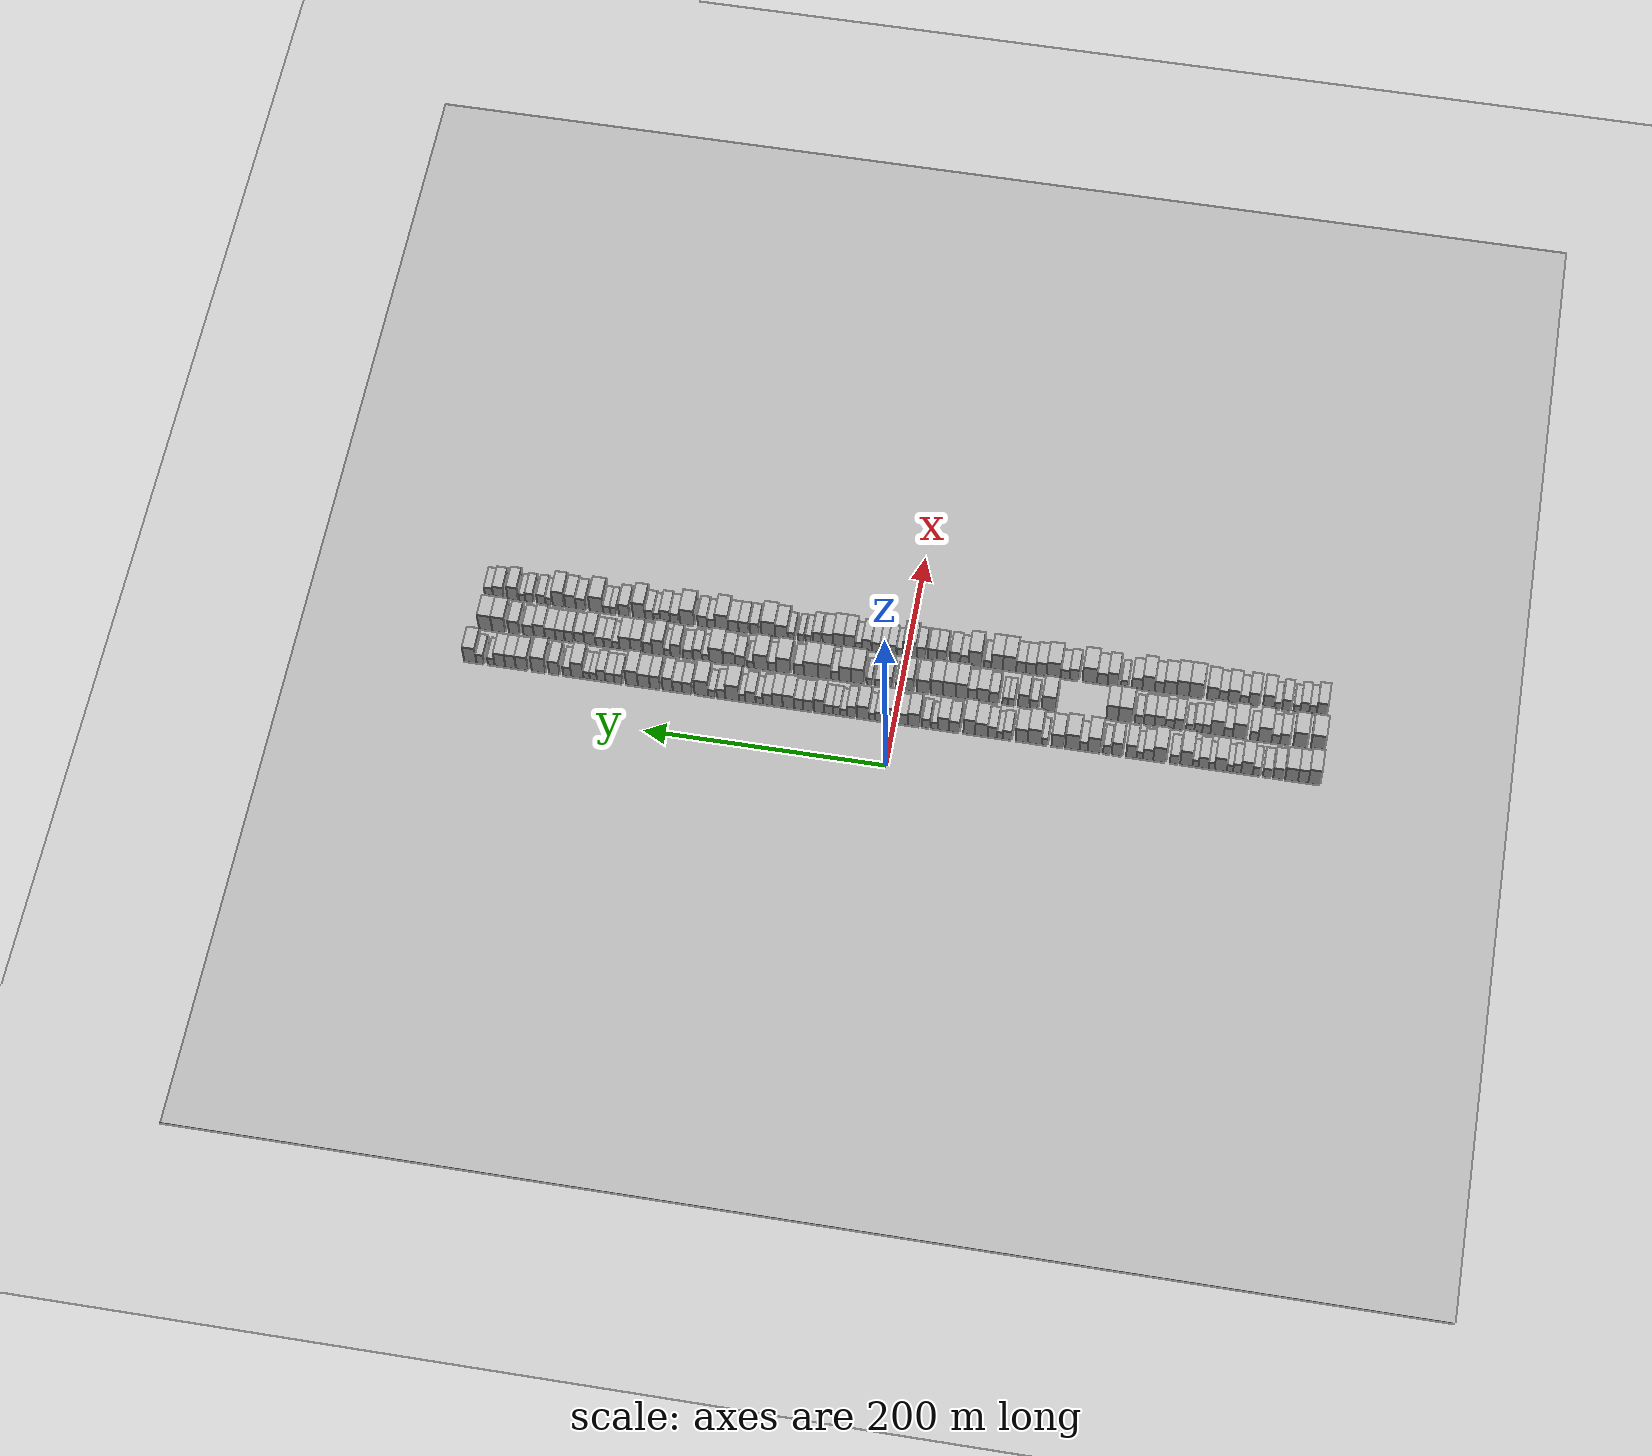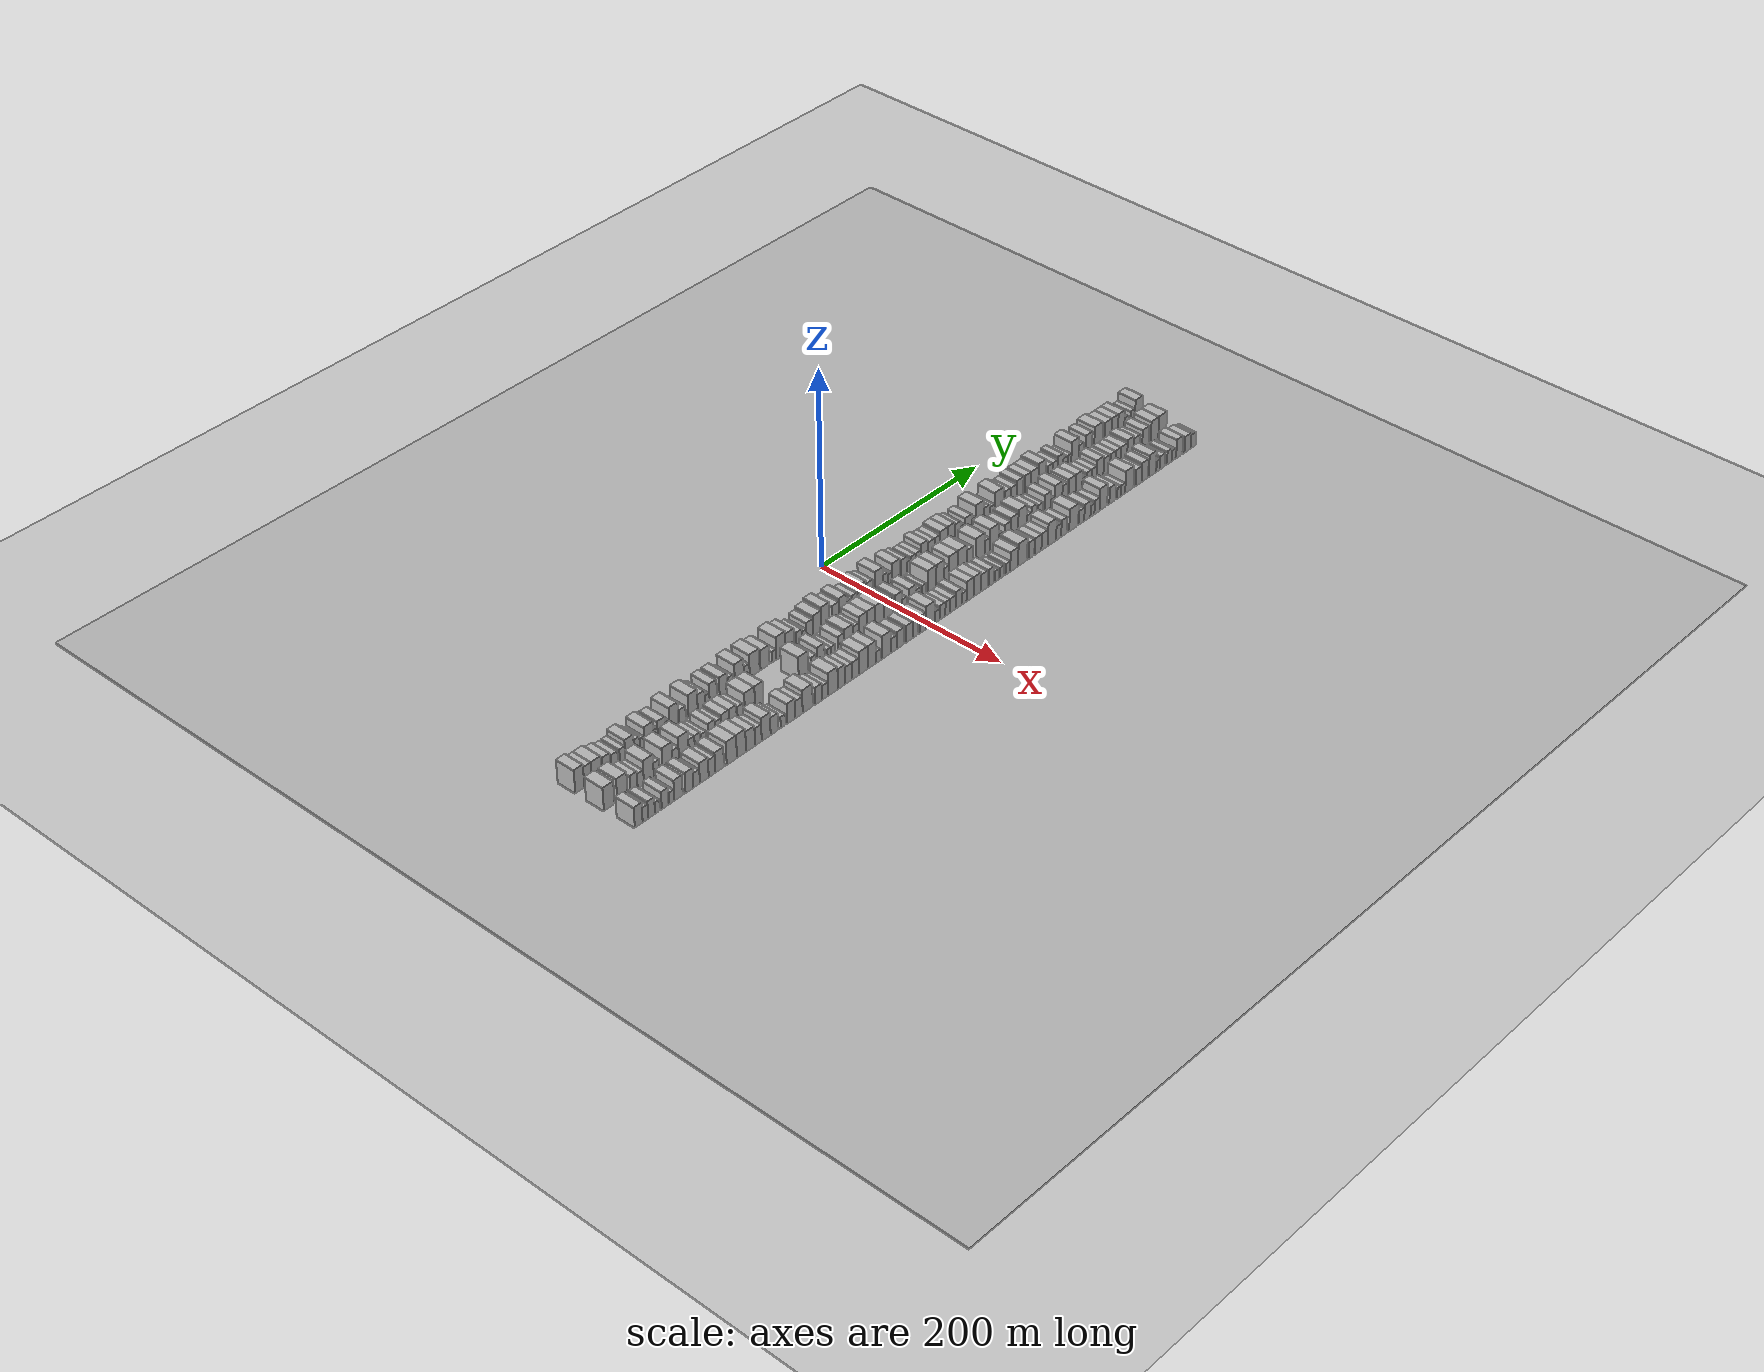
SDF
<?xml version="1.0" encoding="utf-8"?>

<sdf version="1.6">

   <world name="default">

      <gui fullscreen="0">

         <camera name="user_camera">

            <pose>-15 0 4.57585 0 0 0</pose>

            <view_controller>orbit</view_controller>

         </camera>

      </gui>

      <scene>

         <sky>

           <clouds>

             <speed>12</speed>

           </clouds>

         </sky>

         <ambient>0.4 0.4 0.4 1</ambient>

         <background>0.7 0.7 0.7 1</background>

         <shadows>1</shadows>

      </scene>

      <gravity>0 0 -9.8066</gravity>

      <magnetic_field>6e-06 2.3e-05 -4.2e-05</magnetic_field>

      <physics default="0" name="default_physics" type="ode">

         <ode>

            <solver>

               <type>quick</type>

               <iters>10</iters>

               <sor>1.0</sor>

               <use_dynamic_moi_rescaling>0</use_dynamic_moi_rescaling>

            </solver>

            <constraints>

               <cfm>0</cfm>

               <erp>0.2</erp>

               <contact_max_correcting_vel>100</contact_max_correcting_vel>

               <contact_surface_layer>0.001</contact_surface_layer>

            </constraints>

         </ode>

         <max_step_size>0.004</max_step_size>

         <real_time_factor>1</real_time_factor>

         <real_time_update_rate>250</real_time_update_rate>

      </physics>

      <light name="sun" type="directional">

         <cast_shadows>1</cast_shadows>

         <pose>0 0 10 0 0 0</pose>

         <diffuse>0.8 0.8 0.8 1</diffuse>

         <specular>0.2 0.2 0.2 1</specular>

         <attenuation>

            <range>1000</range>

            <constant>0.9</constant>

            <linear>0.01</linear>

            <quadratic>0.001</quadratic>

         </attenuation>

         <direction>-0.5 0.1 -0.9</direction>

      </light>

      <include>

         <name>ground_plane_1</name>

         <uri>model://HANNAS_ground_plane</uri>

         <pose>0 0 0  0 0 0</pose>

      </include>

      <include>

         <name>ground_plane_2</name>

         <uri>model://HANNAS_ground_plane</uri>

         <pose>100 0 0  0 0 0</pose>

      </include>

      <model name="building_1">

         <static>1</static>

         <pose frame="">50.0000 -343.0840 0 0.000000 0.000000 0.000000</pose>

         <link name="link">

            <pose frame="">0 0 12.00 0 0 0</pose>

            <collision name="collision">

               <geometry>

                  <box>

                     <size>20.0000 9.8319 24.0000</size>

                  </box>

               </geometry>

               <max_contacts>10</max_contacts>

               <surface>

                  <contact>

                     <ode/>

                  </contact>

                  <bounce/>

                  <friction>

                     <torsional>

                        <ode/>

                     </torsional>

                     <ode/>

                  </friction>

               </surface>

            </collision>

            <visual name="visual">

               <cast_shadows>0</cast_shadows>

               <geometry>

                  <box>

                     <size>20.0000 9.8319 24.0000</size>

                  </box>

               </geometry>

               <material>

                  <script>

                     <uri>model://HANNAS_wall/materials/scripts</uri>

                     <uri>model://HANNAS_wall/materials/textures</uri>

                     <name>vrc/HANNAS_wall</name>

                  </script>

               </material>

            </visual>

            <self_collide>0</self_collide>

            <enable_wind>0</enable_wind>

            <kinematic>0</kinematic>

         </link>

      </model>

      <model name="building_2">

         <static>1</static>

         <pose frame="">50.0000 -333.9606 0 0.000000 0.000000 0.000000</pose>

         <link name="link">

            <pose frame="">0 0 10.50 0 0 0</pose>

            <collision name="collision">

               <geometry>

                  <box>

                     <size>20.0000 8.4149 21.0000</size>

                  </box>

               </geometry>

               <max_contacts>10</max_contacts>

               <surface>

                  <contact>

                     <ode/>

                  </contact>

                  <bounce/>

                  <friction>

                     <torsional>

                        <ode/>

                     </torsional>

                     <ode/>

                  </friction>

               </surface>

            </collision>

            <visual name="visual">

               <cast_shadows>0</cast_shadows>

               <geometry>

                  <box>

                     <size>20.0000 8.4149 21.0000</size>

                  </box>

               </geometry>

               <material>

                  <script>

                     <uri>model://HANNAS_wall/materials/scripts</uri>

                     <uri>model://HANNAS_wall/materials/textures</uri>

                     <name>vrc/HANNAS_wall</name>

                  </script>

               </material>

            </visual>

            <self_collide>0</self_collide>

            <enable_wind>0</enable_wind>

            <kinematic>0</kinematic>

         </link>

      </model>

      <model name="building_3">

         <static>1</static>

         <pose frame="">50.0000 -324.5482 0 0.000000 0.000000 0.000000</pose>

         <link name="link">

            <pose frame="">0 0 10.50 0 0 0</pose>

            <collision name="collision">

               <geometry>

                  <box>

                     <size>20.0000 10.4098 21.0000</size>

                  </box>

               </geometry>

               <max_contacts>10</max_contacts>

               <surface>

                  <contact>

                     <ode/>

                  </contact>

                  <bounce/>

                  <friction>

                     <torsional>

                        <ode/>

                     </torsional>

                     <ode/>

                  </friction>

               </surface>

            </collision>

            <visual name="visual">

               <cast_shadows>0</cast_shadows>

               <geometry>

                  <box>

                     <size>20.0000 10.4098 21.0000</size>

                  </box>

               </geometry>

               <material>

                  <script>

                     <uri>model://HANNAS_wall/materials/scripts</uri>

                     <uri>model://HANNAS_wall/materials/textures</uri>

                     <name>vrc/HANNAS_wall</name>

                  </script>

               </material>

            </visual>

            <self_collide>0</self_collide>

            <enable_wind>0</enable_wind>

            <kinematic>0</kinematic>

         </link>

      </model>

      <model name="building_4">

         <static>1</static>

         <pose frame="">50.0000 -314.0322 0 0.000000 0.000000 0.000000</pose>

         <link name="link">

            <pose frame="">0 0 9.00 0 0 0</pose>

            <collision name="collision">

               <geometry>

                  <box>

                     <size>20.0000 8.6223 18.0000</size>

                  </box>

               </geometry>

               <max_contacts>10</max_contacts>

               <surface>

                  <contact>

                     <ode/>

                  </contact>

                  <bounce/>

                  <friction>

                     <torsional>

                        <ode/>

                     </torsional>

                     <ode/>

                  </friction>

               </surface>

            </collision>

            <visual name="visual">

               <cast_shadows>0</cast_shadows>

               <geometry>

                  <box>

                     <size>20.0000 8.6223 18.0000</size>

                  </box>

               </geometry>

               <material>

                  <script>

                     <uri>model://HANNAS_wall/materials/scripts</uri>

                     <uri>model://HANNAS_wall/materials/textures</uri>

                     <name>vrc/HANNAS_wall</name>

                  </script>

               </material>

            </visual>

            <self_collide>0</self_collide>

            <enable_wind>0</enable_wind>

            <kinematic>0</kinematic>

         </link>

      </model>

      <model name="building_5">

         <static>1</static>

         <pose frame="">50.0000 -304.9956 0 0.000000 0.000000 0.000000</pose>

         <link name="link">

            <pose frame="">0 0 7.50 0 0 0</pose>

            <collision name="collision">

               <geometry>

                  <box>

                     <size>20.0000 7.4509 15.0000</size>

                  </box>

               </geometry>

               <max_contacts>10</max_contacts>

               <surface>

                  <contact>

                     <ode/>

                  </contact>

                  <bounce/>

                  <friction>

                     <torsional>

                        <ode/>

                     </torsional>

                     <ode/>

                  </friction>

               </surface>

            </collision>

            <visual name="visual">

               <cast_shadows>0</cast_shadows>

               <geometry>

                  <box>

                     <size>20.0000 7.4509 15.0000</size>

                  </box>

               </geometry>

               <material>

                  <script>

                     <uri>model://HANNAS_wall/materials/scripts</uri>

                     <uri>model://HANNAS_wall/materials/textures</uri>

                     <name>vrc/HANNAS_wall</name>

                  </script>

               </material>

            </visual>

            <self_collide>0</self_collide>

            <enable_wind>0</enable_wind>

            <kinematic>0</kinematic>

         </link>

      </model>

      <model name="building_6">

         <static>1</static>

         <pose frame="">50.0000 -296.2317 0 0.000000 0.000000 0.000000</pose>

         <link name="link">

            <pose frame="">0 0 7.50 0 0 0</pose>

            <collision name="collision">

               <geometry>

                  <box>

                     <size>20.0000 6.0768 15.0000</size>

                  </box>

               </geometry>

               <max_contacts>10</max_contacts>

               <surface>

                  <contact>

                     <ode/>

                  </contact>

                  <bounce/>

                  <friction>

                     <torsional>

                        <ode/>

                     </torsional>

                     <ode/>

                  </friction>

               </surface>

            </collision>

            <visual name="visual">

               <cast_shadows>0</cast_shadows>

               <geometry>

                  <box>

                     <size>20.0000 6.0768 15.0000</size>

                  </box>

               </geometry>

               <material>

                  <script>

                     <uri>model://HANNAS_wall/materials/scripts</uri>

                     <uri>model://HANNAS_wall/materials/textures</uri>

                     <name>vrc/HANNAS_wall</name>

                  </script>

               </material>

            </visual>

            <self_collide>0</self_collide>

            <enable_wind>0</enable_wind>

            <kinematic>0</kinematic>

         </link>

      </model>

      <model name="building_7">

         <static>1</static>

         <pose frame="">50.0000 -288.3532 0 0.000000 0.000000 0.000000</pose>

         <link name="link">

            <pose frame="">0 0 10.50 0 0 0</pose>

            <collision name="collision">

               <geometry>

                  <box>

                     <size>20.0000 9.6802 21.0000</size>

                  </box>

               </geometry>

               <max_contacts>10</max_contacts>

               <surface>

                  <contact>

                     <ode/>

                  </contact>

                  <bounce/>

                  <friction>

                     <torsional>

                        <ode/>

                     </torsional>

                     <ode/>

                  </friction>

               </surface>

            </collision>

            <visual name="visual">

               <cast_shadows>0</cast_shadows>

               <geometry>

                  <box>

                     <size>20.0000 9.6802 21.0000</size>

                  </box>

               </geometry>

               <material>

                  <script>

                     <uri>model://HANNAS_wall/materials/scripts</uri>

                     <uri>model://HANNAS_wall/materials/textures</uri>

                     <name>vrc/HANNAS_wall</name>

                  </script>

               </material>

            </visual>

            <self_collide>0</self_collide>

            <enable_wind>0</enable_wind>

            <kinematic>0</kinematic>

         </link>

      </model>

      <model name="building_8">

         <static>1</static>

         <pose frame="">50.0000 -280.2769 0 0.000000 0.000000 0.000000</pose>

         <link name="link">

            <pose frame="">0 0 7.50 0 0 0</pose>

            <collision name="collision">

               <geometry>

                  <box>

                     <size>20.0000 6.4725 15.0000</size>

                  </box>

               </geometry>

               <max_contacts>10</max_contacts>

               <surface>

                  <contact>

                     <ode/>

                  </contact>

                  <bounce/>

                  <friction>

                     <torsional>

                        <ode/>

                     </torsional>

                     <ode/>

                  </friction>

               </surface>

            </collision>

            <visual name="visual">

               <cast_shadows>0</cast_shadows>

               <geometry>

                  <box>

                     <size>20.0000 6.4725 15.0000</size>

                  </box>

               </geometry>

               <material>

                  <script>

                     <uri>model://HANNAS_wall/materials/scripts</uri>

                     <uri>model://HANNAS_wall/materials/textures</uri>

                     <name>vrc/HANNAS_wall</name>

                  </script>

               </material>

            </visual>

            <self_collide>0</self_collide>

            <enable_wind>0</enable_wind>

            <kinematic>0</kinematic>

         </link>

      </model>

      <model name="building_9">

         <static>1</static>

         <pose frame="">50.0000 -274.5351 0 0.000000 0.000000 0.000000</pose>

         <link name="link">

            <pose frame="">0 0 6.00 0 0 0</pose>

            <collision name="collision">

               <geometry>

                  <box>

                     <size>20.0000 5.0110 12.0000</size>

                  </box>

               </geometry>

               <max_contacts>10</max_contacts>

               <surface>

                  <contact>

                     <ode/>

                  </contact>

                  <bounce/>

                  <friction>

                     <torsional>

                        <ode/>

                     </torsional>

                     <ode/>

                  </friction>

               </surface>

            </collision>

            <visual name="visual">

               <cast_shadows>0</cast_shadows>

               <geometry>

                  <box>

                     <size>20.0000 5.0110 12.0000</size>

                  </box>

               </geometry>

               <material>

                  <script>

                     <uri>model://HANNAS_wall/materials/scripts</uri>

                     <uri>model://HANNAS_wall/materials/textures</uri>

                     <name>vrc/HANNAS_wall</name>

                  </script>

               </material>

            </visual>

            <self_collide>0</self_collide>

            <enable_wind>0</enable_wind>

            <kinematic>0</kinematic>

         </link>

      </model>

      <model name="building_10">

         <static>1</static>

         <pose frame="">50.0000 -266.9859 0 0.000000 0.000000 0.000000</pose>

         <link name="link">

            <pose frame="">0 0 10.50 0 0 0</pose>

            <collision name="collision">

               <geometry>

                  <box>

                     <size>20.0000 10.0875 21.0000</size>

                  </box>

               </geometry>

               <max_contacts>10</max_contacts>

               <surface>

                  <contact>

                     <ode/>

                  </contact>

                  <bounce/>

                  <friction>

                     <torsional>

                        <ode/>

                     </torsional>

                     <ode/>

                  </friction>

               </surface>

            </collision>

            <visual name="visual">

               <cast_shadows>0</cast_shadows>

               <geometry>

                  <box>

                     <size>20.0000 10.0875 21.0000</size>

                  </box>

               </geometry>

               <material>

                  <script>

                     <uri>model://HANNAS_wall/materials/scripts</uri>

                     <uri>model://HANNAS_wall/materials/textures</uri>

                     <name>vrc/HANNAS_wall</name>

                  </script>

               </material>

            </visual>

            <self_collide>0</self_collide>

            <enable_wind>0</enable_wind>

            <kinematic>0</kinematic>

         </link>

      </model>

      <model name="building_11">

         <static>1</static>

         <pose frame="">50.0000 -259.5205 0 0.000000 0.000000 0.000000</pose>

         <link name="link">

            <pose frame="">0 0 6.00 0 0 0</pose>

            <collision name="collision">

               <geometry>

                  <box>

                     <size>20.0000 4.8433 12.0000</size>

                  </box>

               </geometry>

               <max_contacts>10</max_contacts>

               <surface>

                  <contact>

                     <ode/>

                  </contact>

                  <bounce/>

                  <friction>

                     <torsional>

                        <ode/>

                     </torsional>

                     <ode/>

                  </friction>

               </surface>

            </collision>

            <visual name="visual">

               <cast_shadows>0</cast_shadows>

               <geometry>

                  <box>

                     <size>20.0000 4.8433 12.0000</size>

                  </box>

               </geometry>

               <material>

                  <script>

                     <uri>model://HANNAS_wall/materials/scripts</uri>

                     <uri>model://HANNAS_wall/materials/textures</uri>

                     <name>vrc/HANNAS_wall</name>

                  </script>

               </material>

            </visual>

            <self_collide>0</self_collide>

            <enable_wind>0</enable_wind>

            <kinematic>0</kinematic>

         </link>

      </model>

      <model name="building_12">

         <static>1</static>

         <pose frame="">50.0000 -252.9690 0 0.000000 0.000000 0.000000</pose>

         <link name="link">

            <pose frame="">0 0 9.00 0 0 0</pose>

            <collision name="collision">

               <geometry>

                  <box>

                     <size>20.0000 8.2598 18.0000</size>

                  </box>

               </geometry>

               <max_contacts>10</max_contacts>

               <surface>

                  <contact>

                     <ode/>

                  </contact>

                  <bounce/>

                  <friction>

                     <torsional>

                        <ode/>

                     </torsional>

                     <ode/>

                  </friction>

               </surface>

            </collision>

            <visual name="visual">

               <cast_shadows>0</cast_shadows>

               <geometry>

                  <box>

                     <size>20.0000 8.2598 18.0000</size>

                  </box>

               </geometry>

               <material>

                  <script>

                     <uri>model://HANNAS_wall/materials/scripts</uri>

                     <uri>model://HANNAS_wall/materials/textures</uri>

                     <name>vrc/HANNAS_wall</name>

                  </script>

               </material>

            </visual>

            <self_collide>0</self_collide>

            <enable_wind>0</enable_wind>

            <kinematic>0</kinematic>

         </link>

      </model>

      <model name="building_13">

         <static>1</static>

         <pose frame="">50.0000 -246.4065 0 0.000000 0.000000 0.000000</pose>

         <link name="link">

            <pose frame="">0 0 6.00 0 0 0</pose>

            <collision name="collision">

               <geometry>

                  <box>

                     <size>20.0000 4.8651 12.0000</size>

                  </box>

               </geometry>

               <max_contacts>10</max_contacts>

               <surface>

                  <contact>

                     <ode/>

                  </contact>

                  <bounce/>

                  <friction>

                     <torsional>

                        <ode/>

                     </torsional>

                     <ode/>

                  </friction>

               </surface>

            </collision>

            <visual name="visual">

               <cast_shadows>0</cast_shadows>

               <geometry>

                  <box>

                     <size>20.0000 4.8651 12.0000</size>

                  </box>

               </geometry>

               <material>

                  <script>

                     <uri>model://HANNAS_wall/materials/scripts</uri>

                     <uri>model://HANNAS_wall/materials/textures</uri>

                     <name>vrc/HANNAS_wall</name>

                  </script>

               </material>

            </visual>

            <self_collide>0</self_collide>

            <enable_wind>0</enable_wind>

            <kinematic>0</kinematic>

         </link>

      </model>

      <model name="building_14">

         <static>1</static>

         <pose frame="">50.0000 -238.9773 0 0.000000 0.000000 0.000000</pose>

         <link name="link">

            <pose frame="">0 0 12.00 0 0 0</pose>

            <collision name="collision">

               <geometry>

                  <box>

                     <size>20.0000 9.9932 24.0000</size>

                  </box>

               </geometry>

               <max_contacts>10</max_contacts>

               <surface>

                  <contact>

                     <ode/>

                  </contact>

                  <bounce/>

                  <friction>

                     <torsional>

                        <ode/>

                     </torsional>

                     <ode/>

                  </friction>

               </surface>

            </collision>

            <visual name="visual">

               <cast_shadows>0</cast_shadows>

               <geometry>

                  <box>

                     <size>20.0000 9.9932 24.0000</size>

                  </box>

               </geometry>

               <material>

                  <script>

                     <uri>model://HANNAS_wall/materials/scripts</uri>

                     <uri>model://HANNAS_wall/materials/textures</uri>

                     <name>vrc/HANNAS_wall</name>

                  </script>

               </material>

            </visual>

            <self_collide>0</self_collide>

            <enable_wind>0</enable_wind>

            <kinematic>0</kinematic>

         </link>

      </model>

      <model name="building_15">

         <static>1</static>

         <pose frame="">50.0000 -229.2700 0 0.000000 0.000000 0.000000</pose>

         <link name="link">

            <pose frame="">0 0 7.50 0 0 0</pose>

            <collision name="collision">

               <geometry>

                  <box>

                     <size>20.0000 7.4215 15.0000</size>

                  </box>

               </geometry>

               <max_contacts>10</max_contacts>

               <surface>

                  <contact>

                     <ode/>

                  </contact>

                  <bounce/>

                  <friction>

                     <torsional>

                        <ode/>

                     </torsional>

                     <ode/>

                  </friction>

               </surface>

            </collision>

            <visual name="visual">

               <cast_shadows>0</cast_shadows>

               <geometry>

                  <box>

                     <size>20.0000 7.4215 15.0000</size>

                  </box>

               </geometry>

               <material>

                  <script>

                     <uri>model://HANNAS_wall/materials/scripts</uri>

                     <uri>model://HANNAS_wall/materials/textures</uri>

                     <name>vrc/HANNAS_wall</name>

                  </script>

               </material>

            </visual>

            <self_collide>0</self_collide>

            <enable_wind>0</enable_wind>

            <kinematic>0</kinematic>

         </link>

      </model>

      <model name="building_16">

         <static>1</static>

         <pose frame="">50.0000 -217.2736 0 0.000000 0.000000 0.000000</pose>

         <link name="link">

            <pose frame="">0 0 12.00 0 0 0</pose>

            <collision name="collision">

               <geometry>

                  <box>

                     <size>20.0000 10.5714 24.0000</size>

                  </box>

               </geometry>

               <max_contacts>10</max_contacts>

               <surface>

                  <contact>

                     <ode/>

                  </contact>

                  <bounce/>

                  <friction>

                     <torsional>

                        <ode/>

                     </torsional>

                     <ode/>

                  </friction>

               </surface>

            </collision>

            <visual name="visual">

               <cast_shadows>0</cast_shadows>

               <geometry>

                  <box>

                     <size>20.0000 10.5714 24.0000</size>

                  </box>

               </geometry>

               <material>

                  <script>

                     <uri>model://HANNAS_wall/materials/scripts</uri>

                     <uri>model://HANNAS_wall/materials/textures</uri>

                     <name>vrc/HANNAS_wall</name>

                  </script>

               </material>

            </visual>

            <self_collide>0</self_collide>

            <enable_wind>0</enable_wind>

            <kinematic>0</kinematic>

         </link>

      </model>

      <model name="building_17">

         <static>1</static>

         <pose frame="">50.0000 -207.7938 0 0.000000 0.000000 0.000000</pose>

         <link name="link">

            <pose frame="">0 0 9.00 0 0 0</pose>

            <collision name="collision">

               <geometry>

                  <box>

                     <size>20.0000 8.3881 18.0000</size>

                  </box>

               </geometry>

               <max_contacts>10</max_contacts>

               <surface>

                  <contact>

                     <ode/>

                  </contact>

                  <bounce/>

                  <friction>

                     <torsional>

                        <ode/>

                     </torsional>

                     <ode/>

                  </friction>

               </surface>

            </collision>

            <visual name="visual">

               <cast_shadows>0</cast_shadows>

               <geometry>

                  <box>

                     <size>20.0000 8.3881 18.0000</size>

                  </box>

               </geometry>

               <material>

                  <script>

                     <uri>model://HANNAS_wall/materials/scripts</uri>

                     <uri>model://HANNAS_wall/materials/textures</uri>

                     <name>vrc/HANNAS_wall</name>

                  </script>

               </material>

            </visual>

            <self_collide>0</self_collide>

            <enable_wind>0</enable_wind>

            <kinematic>0</kinematic>

         </link>

      </model>

      <model name="building_18">

         <static>1</static>

         <pose frame="">50.0000 -200.9474 0 0.000000 0.000000 0.000000</pose>

         <link name="link">

            <pose frame="">0 0 6.00 0 0 0</pose>

            <collision name="collision">

               <geometry>

                  <box>

                     <size>20.0000 5.3048 12.0000</size>

                  </box>

               </geometry>

               <max_contacts>10</max_contacts>

               <surface>

                  <contact>

                     <ode/>

                  </contact>

                  <bounce/>

                  <friction>

                     <torsional>

                        <ode/>

                     </torsional>

                     <ode/>

                  </friction>

               </surface>

            </collision>

            <visual name="visual">

               <cast_shadows>0</cast_shadows>

               <geometry>

                  <box>

                     <size>20.0000 5.3048 12.0000</size>

                  </box>

               </geometry>

               <material>

                  <script>

                     <uri>model://HANNAS_wall/materials/scripts</uri>

                     <uri>model://HANNAS_wall/materials/textures</uri>

                     <name>vrc/HANNAS_wall</name>

                  </script>

               </material>

            </visual>

            <self_collide>0</self_collide>

            <enable_wind>0</enable_wind>

            <kinematic>0</kinematic>

         </link>

      </model>

      <model name="building_19">

         <static>1</static>

         <pose frame="">50.0000 -194.0669 0 0.000000 0.000000 0.000000</pose>

         <link name="link">

            <pose frame="">0 0 10.50 0 0 0</pose>

            <collision name="collision">

               <geometry>

                  <box>

                     <size>20.0000 8.4563 21.0000</size>

                  </box>

               </geometry>

               <max_contacts>10</max_contacts>

               <surface>

                  <contact>

                     <ode/>

                  </contact>

                  <bounce/>

                  <friction>

                     <torsional>

                        <ode/>

                     </torsional>

                     <ode/>

                  </friction>

               </surface>

            </collision>

            <visual name="visual">

               <cast_shadows>0</cast_shadows>

               <geometry>

                  <box>

                     <size>20.0000 8.4563 21.0000</size>

                  </box>

               </geometry>

               <material>

                  <script>

                     <uri>model://HANNAS_wall/materials/scripts</uri>

                     <uri>model://HANNAS_wall/materials/textures</uri>

                     <name>vrc/HANNAS_wall</name>

                  </script>

               </material>

            </visual>

            <self_collide>0</self_collide>

            <enable_wind>0</enable_wind>

            <kinematic>0</kinematic>

         </link>

      </model>

      <model name="building_20">

         <static>1</static>

         <pose frame="">50.0000 -182.4994 0 0.000000 0.000000 0.000000</pose>

         <link name="link">

            <pose frame="">0 0 10.50 0 0 0</pose>

            <collision name="collision">

               <geometry>

                  <box>

                     <size>20.0000 8.6786 21.0000</size>

                  </box>

               </geometry>

               <max_contacts>10</max_contacts>

               <surface>

                  <contact>

                     <ode/>

                  </contact>

                  <bounce/>

                  <friction>

                     <torsional>

                        <ode/>

                     </torsional>

                     <ode/>

                  </friction>

               </surface>

            </collision>

            <visual name="visual">

               <cast_shadows>0</cast_shadows>

               <geometry>

                  <box>

                     <size>20.0000 8.6786 21.0000</size>

                  </box>

               </geometry>

               <material>

                  <script>

                     <uri>model://HANNAS_wall/materials/scripts</uri>

                     <uri>model://HANNAS_wall/materials/textures</uri>

                     <name>vrc/HANNAS_wall</name>

                  </script>

               </material>

            </visual>

            <self_collide>0</self_collide>

            <enable_wind>0</enable_wind>

            <kinematic>0</kinematic>

         </link>

      </model>

      <model name="building_21">

         <static>1</static>

         <pose frame="">50.0000 -174.1144 0 0.000000 0.000000 0.000000</pose>

         <link name="link">

            <pose frame="">0 0 7.50 0 0 0</pose>

            <collision name="collision">

               <geometry>

                  <box>

                     <size>20.0000 6.0914 15.0000</size>

                  </box>

               </geometry>

               <max_contacts>10</max_contacts>

               <surface>

                  <contact>

                     <ode/>

                  </contact>

                  <bounce/>

                  <friction>

                     <torsional>

                        <ode/>

                     </torsional>

                     <ode/>

                  </friction>

               </surface>

            </collision>

            <visual name="visual">

               <cast_shadows>0</cast_shadows>

               <geometry>

                  <box>

                     <size>20.0000 6.0914 15.0000</size>

                  </box>

               </geometry>

               <material>

                  <script>

                     <uri>model://HANNAS_wall/materials/scripts</uri>

                     <uri>model://HANNAS_wall/materials/textures</uri>

                     <name>vrc/HANNAS_wall</name>

                  </script>

               </material>

            </visual>

            <self_collide>0</self_collide>

            <enable_wind>0</enable_wind>

            <kinematic>0</kinematic>

         </link>

      </model>

      <model name="building_22">

         <static>1</static>

         <pose frame="">50.0000 -163.7827 0 0.000000 0.000000 0.000000</pose>

         <link name="link">

            <pose frame="">0 0 12.00 0 0 0</pose>

            <collision name="collision">

               <geometry>

                  <box>

                     <size>20.0000 10.5719 24.0000</size>

                  </box>

               </geometry>

               <max_contacts>10</max_contacts>

               <surface>

                  <contact>

                     <ode/>

                  </contact>

                  <bounce/>

                  <friction>

                     <torsional>

                        <ode/>

                     </torsional>

                     <ode/>

                  </friction>

               </surface>

            </collision>

            <visual name="visual">

               <cast_shadows>0</cast_shadows>

               <geometry>

                  <box>

                     <size>20.0000 10.5719 24.0000</size>

                  </box>

               </geometry>

               <material>

                  <script>

                     <uri>model://HANNAS_wall/materials/scripts</uri>

                     <uri>model://HANNAS_wall/materials/textures</uri>

                     <name>vrc/HANNAS_wall</name>

                  </script>

               </material>

            </visual>

            <self_collide>0</self_collide>

            <enable_wind>0</enable_wind>

            <kinematic>0</kinematic>

         </link>

      </model>

      <model name="building_23">

         <static>1</static>

         <pose frame="">50.0000 -155.1329 0 0.000000 0.000000 0.000000</pose>

         <link name="link">

            <pose frame="">0 0 7.50 0 0 0</pose>

            <collision name="collision">

               <geometry>

                  <box>

                     <size>20.0000 6.7278 15.0000</size>

                  </box>

               </geometry>

               <max_contacts>10</max_contacts>

               <surface>

                  <contact>

                     <ode/>

                  </contact>

                  <bounce/>

                  <friction>

                     <torsional>

                        <ode/>

                     </torsional>

                     <ode/>

                  </friction>

               </surface>

            </collision>

            <visual name="visual">

               <cast_shadows>0</cast_shadows>

               <geometry>

                  <box>

                     <size>20.0000 6.7278 15.0000</size>

                  </box>

               </geometry>

               <material>

                  <script>

                     <uri>model://HANNAS_wall/materials/scripts</uri>

                     <uri>model://HANNAS_wall/materials/textures</uri>

                     <name>vrc/HANNAS_wall</name>

                  </script>

               </material>

            </visual>

            <self_collide>0</self_collide>

            <enable_wind>0</enable_wind>

            <kinematic>0</kinematic>

         </link>

      </model>

      <model name="building_24">

         <static>1</static>

         <pose frame="">50.0000 -145.9663 0 0.000000 0.000000 0.000000</pose>

         <link name="link">

            <pose frame="">0 0 12.00 0 0 0</pose>

            <collision name="collision">

               <geometry>

                  <box>

                     <size>20.0000 11.6054 24.0000</size>

                  </box>

               </geometry>

               <max_contacts>10</max_contacts>

               <surface>

                  <contact>

                     <ode/>

                  </contact>

                  <bounce/>

                  <friction>

                     <torsional>

                        <ode/>

                     </torsional>

                     <ode/>

                  </friction>

               </surface>

            </collision>

            <visual name="visual">

               <cast_shadows>0</cast_shadows>

               <geometry>

                  <box>

                     <size>20.0000 11.6054 24.0000</size>

                  </box>

               </geometry>

               <material>

                  <script>

                     <uri>model://HANNAS_wall/materials/scripts</uri>

                     <uri>model://HANNAS_wall/materials/textures</uri>

                     <name>vrc/HANNAS_wall</name>

                  </script>

               </material>

            </visual>

            <self_collide>0</self_collide>

            <enable_wind>0</enable_wind>

            <kinematic>0</kinematic>

         </link>

      </model>

      <model name="building_25">

         <static>1</static>

         <pose frame="">50.0000 -133.9820 0 0.000000 0.000000 0.000000</pose>

         <link name="link">

            <pose frame="">0 0 10.50 0 0 0</pose>

            <collision name="collision">

               <geometry>

                  <box>

                     <size>20.0000 10.3632 21.0000</size>

                  </box>

               </geometry>

               <max_contacts>10</max_contacts>

               <surface>

                  <contact>

                     <ode/>

                  </contact>

                  <bounce/>

                  <friction>

                     <torsional>

                        <ode/>

                     </torsional>

                     <ode/>

                  </friction>

               </surface>

            </collision>

            <visual name="visual">

               <cast_shadows>0</cast_shadows>

               <geometry>

                  <box>

                     <size>20.0000 10.3632 21.0000</size>

                  </box>

               </geometry>

               <material>

                  <script>

                     <uri>model://HANNAS_wall/materials/scripts</uri>

                     <uri>model://HANNAS_wall/materials/textures</uri>

                     <name>vrc/HANNAS_wall</name>

                  </script>

               </material>

            </visual>

            <self_collide>0</self_collide>

            <enable_wind>0</enable_wind>

            <kinematic>0</kinematic>

         </link>

      </model>

      <model name="building_26">

         <static>1</static>

         <pose frame="">50.0000 -123.2500 0 0.000000 0.000000 0.000000</pose>

         <link name="link">

            <pose frame="">0 0 6.00 0 0 0</pose>

            <collision name="collision">

               <geometry>

                  <box>

                     <size>20.0000 5.1008 12.0000</size>

                  </box>

               </geometry>

               <max_contacts>10</max_contacts>

               <surface>

                  <contact>

                     <ode/>

                  </contact>

                  <bounce/>

                  <friction>

                     <torsional>

                        <ode/>

                     </torsional>

                     <ode/>

                  </friction>

               </surface>

            </collision>

            <visual name="visual">

               <cast_shadows>0</cast_shadows>

               <geometry>

                  <box>

                     <size>20.0000 5.1008 12.0000</size>

                  </box>

               </geometry>

               <material>

                  <script>

                     <uri>model://HANNAS_wall/materials/scripts</uri>

                     <uri>model://HANNAS_wall/materials/textures</uri>

                     <name>vrc/HANNAS_wall</name>

                  </script>

               </material>

            </visual>

            <self_collide>0</self_collide>

            <enable_wind>0</enable_wind>

            <kinematic>0</kinematic>

         </link>

      </model>

      <model name="building_27">

         <static>1</static>

         <pose frame="">50.0000 -115.0750 0 0.000000 0.000000 0.000000</pose>

         <link name="link">

            <pose frame="">0 0 12.00 0 0 0</pose>

            <collision name="collision">

               <geometry>

                  <box>

                     <size>20.0000 11.2492 24.0000</size>

                  </box>

               </geometry>

               <max_contacts>10</max_contacts>

               <surface>

                  <contact>

                     <ode/>

                  </contact>

                  <bounce/>

                  <friction>

                     <torsional>

                        <ode/>

                     </torsional>

                     <ode/>

                  </friction>

               </surface>

            </collision>

            <visual name="visual">

               <cast_shadows>0</cast_shadows>

               <geometry>

                  <box>

                     <size>20.0000 11.2492 24.0000</size>

                  </box>

               </geometry>

               <material>

                  <script>

                     <uri>model://HANNAS_wall/materials/scripts</uri>

                     <uri>model://HANNAS_wall/materials/textures</uri>

                     <name>vrc/HANNAS_wall</name>

                  </script>

               </material>

            </visual>

            <self_collide>0</self_collide>

            <enable_wind>0</enable_wind>

            <kinematic>0</kinematic>

         </link>

      </model>

      <model name="building_28">

         <static>1</static>

         <pose frame="">50.0000 -104.3734 0 0.000000 0.000000 0.000000</pose>

         <link name="link">

            <pose frame="">0 0 10.50 0 0 0</pose>

            <collision name="collision">

               <geometry>

                  <box>

                     <size>20.0000 10.1541 21.0000</size>

                  </box>

               </geometry>

               <max_contacts>10</max_contacts>

               <surface>

                  <contact>

                     <ode/>

                  </contact>

                  <bounce/>

                  <friction>

                     <torsional>

                        <ode/>

                     </torsional>

                     <ode/>

                  </friction>

               </surface>

            </collision>

            <visual name="visual">

               <cast_shadows>0</cast_shadows>

               <geometry>

                  <box>

                     <size>20.0000 10.1541 21.0000</size>

                  </box>

               </geometry>

               <material>

                  <script>

                     <uri>model://HANNAS_wall/materials/scripts</uri>

                     <uri>model://HANNAS_wall/materials/textures</uri>

                     <name>vrc/HANNAS_wall</name>

                  </script>

               </material>

            </visual>

            <self_collide>0</self_collide>

            <enable_wind>0</enable_wind>

            <kinematic>0</kinematic>

         </link>

      </model>

      <model name="building_29">

         <static>1</static>

         <pose frame="">50.0000 -92.6563 0 0.000000 0.000000 0.000000</pose>

         <link name="link">

            <pose frame="">0 0 7.50 0 0 0</pose>

            <collision name="collision">

               <geometry>

                  <box>

                     <size>20.0000 7.2801 15.0000</size>

                  </box>

               </geometry>

               <max_contacts>10</max_contacts>

               <surface>

                  <contact>

                     <ode/>

                  </contact>

                  <bounce/>

                  <friction>

                     <torsional>

                        <ode/>

                     </torsional>

                     <ode/>

                  </friction>

               </surface>

            </collision>

            <visual name="visual">

               <cast_shadows>0</cast_shadows>

               <geometry>

                  <box>

                     <size>20.0000 7.2801 15.0000</size>

                  </box>

               </geometry>

               <material>

                  <script>

                     <uri>model://HANNAS_wall/materials/scripts</uri>

                     <uri>model://HANNAS_wall/materials/textures</uri>

                     <name>vrc/HANNAS_wall</name>

                  </script>

               </material>

            </visual>

            <self_collide>0</self_collide>

            <enable_wind>0</enable_wind>

            <kinematic>0</kinematic>

         </link>

      </model>

      <model name="building_30">

         <static>1</static>

         <pose frame="">50.0000 -86.5991 0 0.000000 0.000000 0.000000</pose>

         <link name="link">

            <pose frame="">0 0 6.00 0 0 0</pose>

            <collision name="collision">

               <geometry>

                  <box>

                     <size>20.0000 4.8341 12.0000</size>

                  </box>

               </geometry>

               <max_contacts>10</max_contacts>

               <surface>

                  <contact>

                     <ode/>

                  </contact>

                  <bounce/>

                  <friction>

                     <torsional>

                        <ode/>

                     </torsional>

                     <ode/>

                  </friction>

               </surface>

            </collision>

            <visual name="visual">

               <cast_shadows>0</cast_shadows>

               <geometry>

                  <box>

                     <size>20.0000 4.8341 12.0000</size>

                  </box>

               </geometry>

               <material>

                  <script>

                     <uri>model://HANNAS_wall/materials/scripts</uri>

                     <uri>model://HANNAS_wall/materials/textures</uri>

                     <name>vrc/HANNAS_wall</name>

                  </script>

               </material>

            </visual>

            <self_collide>0</self_collide>

            <enable_wind>0</enable_wind>

            <kinematic>0</kinematic>

         </link>

      </model>

      <model name="building_31">

         <static>1</static>

         <pose frame="">50.0000 -80.3739 0 0.000000 0.000000 0.000000</pose>

         <link name="link">

            <pose frame="">0 0 9.00 0 0 0</pose>

            <collision name="collision">

               <geometry>

                  <box>

                     <size>20.0000 7.6165 18.0000</size>

                  </box>

               </geometry>

               <max_contacts>10</max_contacts>

               <surface>

                  <contact>

                     <ode/>

                  </contact>

                  <bounce/>

                  <friction>

                     <torsional>

                        <ode/>

                     </torsional>

                     <ode/>

                  </friction>

               </surface>

            </collision>

            <visual name="visual">

               <cast_shadows>0</cast_shadows>

               <geometry>

                  <box>

                     <size>20.0000 7.6165 18.0000</size>

                  </box>

               </geometry>

               <material>

                  <script>

                     <uri>model://HANNAS_wall/materials/scripts</uri>

                     <uri>model://HANNAS_wall/materials/textures</uri>

                     <name>vrc/HANNAS_wall</name>

                  </script>

               </material>

            </visual>

            <self_collide>0</self_collide>

            <enable_wind>0</enable_wind>

            <kinematic>0</kinematic>

         </link>

      </model>

      <model name="building_32">

         <static>1</static>

         <pose frame="">50.0000 -71.3733 0 0.000000 0.000000 0.000000</pose>

         <link name="link">

            <pose frame="">0 0 10.50 0 0 0</pose>

            <collision name="collision">

               <geometry>

                  <box>

                     <size>20.0000 10.3846 21.0000</size>

                  </box>

               </geometry>

               <max_contacts>10</max_contacts>

               <surface>

                  <contact>

                     <ode/>

                  </contact>

                  <bounce/>

                  <friction>

                     <torsional>

                        <ode/>

                     </torsional>

                     <ode/>

                  </friction>

               </surface>

            </collision>

            <visual name="visual">

               <cast_shadows>0</cast_shadows>

               <geometry>

                  <box>

                     <size>20.0000 10.3846 21.0000</size>

                  </box>

               </geometry>

               <material>

                  <script>

                     <uri>model://HANNAS_wall/materials/scripts</uri>

                     <uri>model://HANNAS_wall/materials/textures</uri>

                     <name>vrc/HANNAS_wall</name>

                  </script>

               </material>

            </visual>

            <self_collide>0</self_collide>

            <enable_wind>0</enable_wind>

            <kinematic>0</kinematic>

         </link>

      </model>

      <model name="building_33">

         <static>1</static>

         <pose frame="">50.0000 -61.3326 0 0.000000 0.000000 0.000000</pose>

         <link name="link">

            <pose frame="">0 0 12.00 0 0 0</pose>

            <collision name="collision">

               <geometry>

                  <box>

                     <size>20.0000 9.6969 24.0000</size>

                  </box>

               </geometry>

               <max_contacts>10</max_contacts>

               <surface>

                  <contact>

                     <ode/>

                  </contact>

                  <bounce/>

                  <friction>

                     <torsional>

                        <ode/>

                     </torsional>

                     <ode/>

                  </friction>

               </surface>

            </collision>

            <visual name="visual">

               <cast_shadows>0</cast_shadows>

               <geometry>

                  <box>

                     <size>20.0000 9.6969 24.0000</size>

                  </box>

               </geometry>

               <material>

                  <script>

                     <uri>model://HANNAS_wall/materials/scripts</uri>

                     <uri>model://HANNAS_wall/materials/textures</uri>

                     <name>vrc/HANNAS_wall</name>

                  </script>

               </material>

            </visual>

            <self_collide>0</self_collide>

            <enable_wind>0</enable_wind>

            <kinematic>0</kinematic>

         </link>

      </model>

      <model name="building_34">

         <static>1</static>

         <pose frame="">50.0000 -49.1256 0 0.000000 0.000000 0.000000</pose>

         <link name="link">

            <pose frame="">0 0 9.00 0 0 0</pose>

            <collision name="collision">

               <geometry>

                  <box>

                     <size>20.0000 8.7171 18.0000</size>

                  </box>

               </geometry>

               <max_contacts>10</max_contacts>

               <surface>

                  <contact>

                     <ode/>

                  </contact>

                  <bounce/>

                  <friction>

                     <torsional>

                        <ode/>

                     </torsional>

                     <ode/>

                  </friction>

               </surface>

            </collision>

            <visual name="visual">

               <cast_shadows>0</cast_shadows>

               <geometry>

                  <box>

                     <size>20.0000 8.7171 18.0000</size>

                  </box>

               </geometry>

               <material>

                  <script>

                     <uri>model://HANNAS_wall/materials/scripts</uri>

                     <uri>model://HANNAS_wall/materials/textures</uri>

                     <name>vrc/HANNAS_wall</name>

                  </script>

               </material>

            </visual>

            <self_collide>0</self_collide>

            <enable_wind>0</enable_wind>

            <kinematic>0</kinematic>

         </link>

      </model>

      <model name="building_35">

         <static>1</static>

         <pose frame="">50.0000 -40.0122 0 0.000000 0.000000 0.000000</pose>

         <link name="link">

            <pose frame="">0 0 10.50 0 0 0</pose>

            <collision name="collision">

               <geometry>

                  <box>

                     <size>20.0000 9.5096 21.0000</size>

                  </box>

               </geometry>

               <max_contacts>10</max_contacts>

               <surface>

                  <contact>

                     <ode/>

                  </contact>

                  <bounce/>

                  <friction>

                     <torsional>

                        <ode/>

                     </torsional>

                     <ode/>

                  </friction>

               </surface>

            </collision>

            <visual name="visual">

               <cast_shadows>0</cast_shadows>

               <geometry>

                  <box>

                     <size>20.0000 9.5096 21.0000</size>

                  </box>

               </geometry>

               <material>

                  <script>

                     <uri>model://HANNAS_wall/materials/scripts</uri>

                     <uri>model://HANNAS_wall/materials/textures</uri>

                     <name>vrc/HANNAS_wall</name>

                  </script>

               </material>

            </visual>

            <self_collide>0</self_collide>

            <enable_wind>0</enable_wind>

            <kinematic>0</kinematic>

         </link>

      </model>

      <model name="building_36">

         <static>1</static>

         <pose frame="">50.0000 -32.6722 0 0.000000 0.000000 0.000000</pose>

         <link name="link">

            <pose frame="">0 0 6.00 0 0 0</pose>

            <collision name="collision">

               <geometry>

                  <box>

                     <size>20.0000 5.1704 12.0000</size>

                  </box>

               </geometry>

               <max_contacts>10</max_contacts>

               <surface>

                  <contact>

                     <ode/>

                  </contact>

                  <bounce/>

                  <friction>

                     <torsional>

                        <ode/>

                     </torsional>

                     <ode/>

                  </friction>

               </surface>

            </collision>

            <visual name="visual">

               <cast_shadows>0</cast_shadows>

               <geometry>

                  <box>

                     <size>20.0000 5.1704 12.0000</size>

                  </box>

               </geometry>

               <material>

                  <script>

                     <uri>model://HANNAS_wall/materials/scripts</uri>

                     <uri>model://HANNAS_wall/materials/textures</uri>

                     <name>vrc/HANNAS_wall</name>

                  </script>

               </material>

            </visual>

            <self_collide>0</self_collide>

            <enable_wind>0</enable_wind>

            <kinematic>0</kinematic>

         </link>

      </model>

      <model name="building_37">

         <static>1</static>

         <pose frame="">50.0000 -25.8383 0 0.000000 0.000000 0.000000</pose>

         <link name="link">

            <pose frame="">0 0 7.50 0 0 0</pose>

            <collision name="collision">

               <geometry>

                  <box>

                     <size>20.0000 6.4973 15.0000</size>

                  </box>

               </geometry>

               <max_contacts>10</max_contacts>

               <surface>

                  <contact>

                     <ode/>

                  </contact>

                  <bounce/>

                  <friction>

                     <torsional>

                        <ode/>

                     </torsional>

                     <ode/>

                  </friction>

               </surface>

            </collision>

            <visual name="visual">

               <cast_shadows>0</cast_shadows>

               <geometry>

                  <box>

                     <size>20.0000 6.4973 15.0000</size>

                  </box>

               </geometry>

               <material>

                  <script>

                     <uri>model://HANNAS_wall/materials/scripts</uri>

                     <uri>model://HANNAS_wall/materials/textures</uri>

                     <name>vrc/HANNAS_wall</name>

                  </script>

               </material>

            </visual>

            <self_collide>0</self_collide>

            <enable_wind>0</enable_wind>

            <kinematic>0</kinematic>

         </link>

      </model>

      <model name="building_38">

         <static>1</static>

         <pose frame="">50.0000 -15.7071 0 0.000000 0.000000 0.000000</pose>

         <link name="link">

            <pose frame="">0 0 10.50 0 0 0</pose>

            <collision name="collision">

               <geometry>

                  <box>

                     <size>20.0000 9.7650 21.0000</size>

                  </box>

               </geometry>

               <max_contacts>10</max_contacts>

               <surface>

                  <contact>

                     <ode/>

                  </contact>

                  <bounce/>

                  <friction>

                     <torsional>

                        <ode/>

                     </torsional>

                     <ode/>

                  </friction>

               </surface>

            </collision>

            <visual name="visual">

               <cast_shadows>0</cast_shadows>

               <geometry>

                  <box>

                     <size>20.0000 9.7650 21.0000</size>

                  </box>

               </geometry>

               <material>

                  <script>

                     <uri>model://HANNAS_wall/materials/scripts</uri>

                     <uri>model://HANNAS_wall/materials/textures</uri>

                     <name>vrc/HANNAS_wall</name>

                  </script>

               </material>

            </visual>

            <self_collide>0</self_collide>

            <enable_wind>0</enable_wind>

            <kinematic>0</kinematic>

         </link>

      </model>

      <model name="building_39">

         <static>1</static>

         <pose frame="">50.0000 -6.8539 0 0.000000 0.000000 0.000000</pose>

         <link name="link">

            <pose frame="">0 0 9.00 0 0 0</pose>

            <collision name="collision">

               <geometry>

                  <box>

                     <size>20.0000 7.9415 18.0000</size>

                  </box>

               </geometry>

               <max_contacts>10</max_contacts>

               <surface>

                  <contact>

                     <ode/>

                  </contact>

                  <bounce/>

                  <friction>

                     <torsional>

                        <ode/>

                     </torsional>

                     <ode/>

                  </friction>

               </surface>

            </collision>

            <visual name="visual">

               <cast_shadows>0</cast_shadows>

               <geometry>

                  <box>

                     <size>20.0000 7.9415 18.0000</size>

                  </box>

               </geometry>

               <material>

                  <script>

                     <uri>model://HANNAS_wall/materials/scripts</uri>

                     <uri>model://HANNAS_wall/materials/textures</uri>

                     <name>vrc/HANNAS_wall</name>

                  </script>

               </material>

            </visual>

            <self_collide>0</self_collide>

            <enable_wind>0</enable_wind>

            <kinematic>0</kinematic>

         </link>

      </model>

      <model name="building_40">

         <static>1</static>

         <pose frame="">50.0000 4.9906 0 0.000000 0.000000 0.000000</pose>

         <link name="link">

            <pose frame="">0 0 12.00 0 0 0</pose>

            <collision name="collision">

               <geometry>

                  <box>

                     <size>20.0000 9.7473 24.0000</size>

                  </box>

               </geometry>

               <max_contacts>10</max_contacts>

               <surface>

                  <contact>

                     <ode/>

                  </contact>

                  <bounce/>

                  <friction>

                     <torsional>

                        <ode/>

                     </torsional>

                     <ode/>

                  </friction>

               </surface>

            </collision>

            <visual name="visual">

               <cast_shadows>0</cast_shadows>

               <geometry>

                  <box>

                     <size>20.0000 9.7473 24.0000</size>

                  </box>

               </geometry>

               <material>

                  <script>

                     <uri>model://HANNAS_wall/materials/scripts</uri>

                     <uri>model://HANNAS_wall/materials/textures</uri>

                     <name>vrc/HANNAS_wall</name>

                  </script>

               </material>

            </visual>

            <self_collide>0</self_collide>

            <enable_wind>0</enable_wind>

            <kinematic>0</kinematic>

         </link>

      </model>

      <model name="building_41">

         <static>1</static>

         <pose frame="">50.0000 13.0793 0 0.000000 0.000000 0.000000</pose>

         <link name="link">

            <pose frame="">0 0 7.50 0 0 0</pose>

            <collision name="collision">

               <geometry>

                  <box>

                     <size>20.0000 6.4302 15.0000</size>

                  </box>

               </geometry>

               <max_contacts>10</max_contacts>

               <surface>

                  <contact>

                     <ode/>

                  </contact>

                  <bounce/>

                  <friction>

                     <torsional>

                        <ode/>

                     </torsional>

                     <ode/>

                  </friction>

               </surface>

            </collision>

            <visual name="visual">

               <cast_shadows>0</cast_shadows>

               <geometry>

                  <box>

                     <size>20.0000 6.4302 15.0000</size>

                  </box>

               </geometry>

               <material>

                  <script>

                     <uri>model://HANNAS_wall/materials/scripts</uri>

                     <uri>model://HANNAS_wall/materials/textures</uri>

                     <name>vrc/HANNAS_wall</name>

                  </script>

               </material>

            </visual>

            <self_collide>0</self_collide>

            <enable_wind>0</enable_wind>

            <kinematic>0</kinematic>

         </link>

      </model>

      <model name="building_42">

         <static>1</static>

         <pose frame="">50.0000 18.8597 0 0.000000 0.000000 0.000000</pose>

         <link name="link">

            <pose frame="">0 0 6.00 0 0 0</pose>

            <collision name="collision">

               <geometry>

                  <box>

                     <size>20.0000 5.1306 12.0000</size>

                  </box>

               </geometry>

               <max_contacts>10</max_contacts>

               <surface>

                  <contact>

                     <ode/>

                  </contact>

                  <bounce/>

                  <friction>

                     <torsional>

                        <ode/>

                     </torsional>

                     <ode/>

                  </friction>

               </surface>

            </collision>

            <visual name="visual">

               <cast_shadows>0</cast_shadows>

               <geometry>

                  <box>

                     <size>20.0000 5.1306 12.0000</size>

                  </box>

               </geometry>

               <material>

                  <script>

                     <uri>model://HANNAS_wall/materials/scripts</uri>

                     <uri>model://HANNAS_wall/materials/textures</uri>

                     <name>vrc/HANNAS_wall</name>

                  </script>

               </material>

            </visual>

            <self_collide>0</self_collide>

            <enable_wind>0</enable_wind>

            <kinematic>0</kinematic>

         </link>

      </model>

      <model name="building_43">

         <static>1</static>

         <pose frame="">50.0000 26.3520 0 0.000000 0.000000 0.000000</pose>

         <link name="link">

            <pose frame="">0 0 10.50 0 0 0</pose>

            <collision name="collision">

               <geometry>

                  <box>

                     <size>20.0000 9.8539 21.0000</size>

                  </box>

               </geometry>

               <max_contacts>10</max_contacts>

               <surface>

                  <contact>

                     <ode/>

                  </contact>

                  <bounce/>

                  <friction>

                     <torsional>

                        <ode/>

                     </torsional>

                     <ode/>

                  </friction>

               </surface>

            </collision>

            <visual name="visual">

               <cast_shadows>0</cast_shadows>

               <geometry>

                  <box>

                     <size>20.0000 9.8539 21.0000</size>

                  </box>

               </geometry>

               <material>

                  <script>

                     <uri>model://HANNAS_wall/materials/scripts</uri>

                     <uri>model://HANNAS_wall/materials/textures</uri>

                     <name>vrc/HANNAS_wall</name>

                  </script>

               </material>

            </visual>

            <self_collide>0</self_collide>

            <enable_wind>0</enable_wind>

            <kinematic>0</kinematic>

         </link>

      </model>

      <model name="building_44">

         <static>1</static>

         <pose frame="">50.0000 35.9243 0 0.000000 0.000000 0.000000</pose>

         <link name="link">

            <pose frame="">0 0 9.00 0 0 0</pose>

            <collision name="collision">

               <geometry>

                  <box>

                     <size>20.0000 7.2907 18.0000</size>

                  </box>

               </geometry>

               <max_contacts>10</max_contacts>

               <surface>

                  <contact>

                     <ode/>

                  </contact>

                  <bounce/>

                  <friction>

                     <torsional>

                        <ode/>

                     </torsional>

                     <ode/>

                  </friction>

               </surface>

            </collision>

            <visual name="visual">

               <cast_shadows>0</cast_shadows>

               <geometry>

                  <box>

                     <size>20.0000 7.2907 18.0000</size>

                  </box>

               </geometry>

               <material>

                  <script>

                     <uri>model://HANNAS_wall/materials/scripts</uri>

                     <uri>model://HANNAS_wall/materials/textures</uri>

                     <name>vrc/HANNAS_wall</name>

                  </script>

               </material>

            </visual>

            <self_collide>0</self_collide>

            <enable_wind>0</enable_wind>

            <kinematic>0</kinematic>

         </link>

      </model>

      <model name="building_45">

         <static>1</static>

         <pose frame="">50.0000 42.2294 0 0.000000 0.000000 0.000000</pose>

         <link name="link">

            <pose frame="">0 0 6.00 0 0 0</pose>

            <collision name="collision">

               <geometry>

                  <box>

                     <size>20.0000 5.3195 12.0000</size>

                  </box>

               </geometry>

               <max_contacts>10</max_contacts>

               <surface>

                  <contact>

                     <ode/>

                  </contact>

                  <bounce/>

                  <friction>

                     <torsional>

                        <ode/>

                     </torsional>

                     <ode/>

                  </friction>

               </surface>

            </collision>

            <visual name="visual">

               <cast_shadows>0</cast_shadows>

               <geometry>

                  <box>

                     <size>20.0000 5.3195 12.0000</size>

                  </box>

               </geometry>

               <material>

                  <script>

                     <uri>model://HANNAS_wall/materials/scripts</uri>

                     <uri>model://HANNAS_wall/materials/textures</uri>

                     <name>vrc/HANNAS_wall</name>

                  </script>

               </material>

            </visual>

            <self_collide>0</self_collide>

            <enable_wind>0</enable_wind>

            <kinematic>0</kinematic>

         </link>

      </model>

      <model name="building_46">

         <static>1</static>

         <pose frame="">50.0000 48.0689 0 0.000000 0.000000 0.000000</pose>

         <link name="link">

            <pose frame="">0 0 7.50 0 0 0</pose>

            <collision name="collision">

               <geometry>

                  <box>

                     <size>20.0000 6.3595 15.0000</size>

                  </box>

               </geometry>

               <max_contacts>10</max_contacts>

               <surface>

                  <contact>

                     <ode/>

                  </contact>

                  <bounce/>

                  <friction>

                     <torsional>

                        <ode/>

                     </torsional>

                     <ode/>

                  </friction>

               </surface>

            </collision>

            <visual name="visual">

               <cast_shadows>0</cast_shadows>

               <geometry>

                  <box>

                     <size>20.0000 6.3595 15.0000</size>

                  </box>

               </geometry>

               <material>

                  <script>

                     <uri>model://HANNAS_wall/materials/scripts</uri>

                     <uri>model://HANNAS_wall/materials/textures</uri>

                     <name>vrc/HANNAS_wall</name>

                  </script>

               </material>

            </visual>

            <self_collide>0</self_collide>

            <enable_wind>0</enable_wind>

            <kinematic>0</kinematic>

         </link>

      </model>

      <model name="building_47">

         <static>1</static>

         <pose frame="">50.0000 54.6852 0 0.000000 0.000000 0.000000</pose>

         <link name="link">

            <pose frame="">0 0 7.50 0 0 0</pose>

            <collision name="collision">

               <geometry>

                  <box>

                     <size>20.0000 6.8732 15.0000</size>

                  </box>

               </geometry>

               <max_contacts>10</max_contacts>

               <surface>

                  <contact>

                     <ode/>

                  </contact>

                  <bounce/>

                  <friction>

                     <torsional>

                        <ode/>

                     </torsional>

                     <ode/>

                  </friction>

               </surface>

            </collision>

            <visual name="visual">

               <cast_shadows>0</cast_shadows>

               <geometry>

                  <box>

                     <size>20.0000 6.8732 15.0000</size>

                  </box>

               </geometry>

               <material>

                  <script>

                     <uri>model://HANNAS_wall/materials/scripts</uri>

                     <uri>model://HANNAS_wall/materials/textures</uri>

                     <name>vrc/HANNAS_wall</name>

                  </script>

               </material>

            </visual>

            <self_collide>0</self_collide>

            <enable_wind>0</enable_wind>

            <kinematic>0</kinematic>

         </link>

      </model>

      <model name="building_48">

         <static>1</static>

         <pose frame="">50.0000 62.3393 0 0.000000 0.000000 0.000000</pose>

         <link name="link">

            <pose frame="">0 0 10.50 0 0 0</pose>

            <collision name="collision">

               <geometry>

                  <box>

                     <size>20.0000 8.4348 21.0000</size>

                  </box>

               </geometry>

               <max_contacts>10</max_contacts>

               <surface>

                  <contact>

                     <ode/>

                  </contact>

                  <bounce/>

                  <friction>

                     <torsional>

                        <ode/>

                     </torsional>

                     <ode/>

                  </friction>

               </surface>

            </collision>

            <visual name="visual">

               <cast_shadows>0</cast_shadows>

               <geometry>

                  <box>

                     <size>20.0000 8.4348 21.0000</size>

                  </box>

               </geometry>

               <material>

                  <script>

                     <uri>model://HANNAS_wall/materials/scripts</uri>

                     <uri>model://HANNAS_wall/materials/textures</uri>

                     <name>vrc/HANNAS_wall</name>

                  </script>

               </material>

            </visual>

            <self_collide>0</self_collide>

            <enable_wind>0</enable_wind>

            <kinematic>0</kinematic>

         </link>

      </model>

      <model name="building_49">

         <static>1</static>

         <pose frame="">50.0000 71.6197 0 0.000000 0.000000 0.000000</pose>

         <link name="link">

            <pose frame="">0 0 9.00 0 0 0</pose>

            <collision name="collision">

               <geometry>

                  <box>

                     <size>20.0000 8.1261 18.0000</size>

                  </box>

               </geometry>

               <max_contacts>10</max_contacts>

               <surface>

                  <contact>

                     <ode/>

                  </contact>

                  <bounce/>

                  <friction>

                     <torsional>

                        <ode/>

                     </torsional>

                     <ode/>

                  </friction>

               </surface>

            </collision>

            <visual name="visual">

               <cast_shadows>0</cast_shadows>

               <geometry>

                  <box>

                     <size>20.0000 8.1261 18.0000</size>

                  </box>

               </geometry>

               <material>

                  <script>

                     <uri>model://HANNAS_wall/materials/scripts</uri>

                     <uri>model://HANNAS_wall/materials/textures</uri>

                     <name>vrc/HANNAS_wall</name>

                  </script>

               </material>

            </visual>

            <self_collide>0</self_collide>

            <enable_wind>0</enable_wind>

            <kinematic>0</kinematic>

         </link>

      </model>

      <model name="building_50">

         <static>1</static>

         <pose frame="">50.0000 79.3008 0 0.000000 0.000000 0.000000</pose>

         <link name="link">

            <pose frame="">0 0 9.00 0 0 0</pose>

            <collision name="collision">

               <geometry>

                  <box>

                     <size>20.0000 7.2360 18.0000</size>

                  </box>

               </geometry>

               <max_contacts>10</max_contacts>

               <surface>

                  <contact>

                     <ode/>

                  </contact>

                  <bounce/>

                  <friction>

                     <torsional>

                        <ode/>

                     </torsional>

                     <ode/>

                  </friction>

               </surface>

            </collision>

            <visual name="visual">

               <cast_shadows>0</cast_shadows>

               <geometry>

                  <box>

                     <size>20.0000 7.2360 18.0000</size>

                  </box>

               </geometry>

               <material>

                  <script>

                     <uri>model://HANNAS_wall/materials/scripts</uri>

                     <uri>model://HANNAS_wall/materials/textures</uri>

                     <name>vrc/HANNAS_wall</name>

                  </script>

               </material>

            </visual>

            <self_collide>0</self_collide>

            <enable_wind>0</enable_wind>

            <kinematic>0</kinematic>

         </link>

      </model>

      <model name="building_51">

         <static>1</static>

         <pose frame="">50.0000 87.7873 0 0.000000 0.000000 0.000000</pose>

         <link name="link">

            <pose frame="">0 0 10.50 0 0 0</pose>

            <collision name="collision">

               <geometry>

                  <box>

                     <size>20.0000 9.7369 21.0000</size>

                  </box>

               </geometry>

               <max_contacts>10</max_contacts>

               <surface>

                  <contact>

                     <ode/>

                  </contact>

                  <bounce/>

                  <friction>

                     <torsional>

                        <ode/>

                     </torsional>

                     <ode/>

                  </friction>

               </surface>

            </collision>

            <visual name="visual">

               <cast_shadows>0</cast_shadows>

               <geometry>

                  <box>

                     <size>20.0000 9.7369 21.0000</size>

                  </box>

               </geometry>

               <material>

                  <script>

                     <uri>model://HANNAS_wall/materials/scripts</uri>

                     <uri>model://HANNAS_wall/materials/textures</uri>

                     <name>vrc/HANNAS_wall</name>

                  </script>

               </material>

            </visual>

            <self_collide>0</self_collide>

            <enable_wind>0</enable_wind>

            <kinematic>0</kinematic>

         </link>

      </model>

      <model name="building_52">

         <static>1</static>

         <pose frame="">50.0000 97.0397 0 0.000000 0.000000 0.000000</pose>

         <link name="link">

            <pose frame="">0 0 10.50 0 0 0</pose>

            <collision name="collision">

               <geometry>

                  <box>

                     <size>20.0000 8.7679 21.0000</size>

                  </box>

               </geometry>

               <max_contacts>10</max_contacts>

               <surface>

                  <contact>

                     <ode/>

                  </contact>

                  <bounce/>

                  <friction>

                     <torsional>

                        <ode/>

                     </torsional>

                     <ode/>

                  </friction>

               </surface>

            </collision>

            <visual name="visual">

               <cast_shadows>0</cast_shadows>

               <geometry>

                  <box>

                     <size>20.0000 8.7679 21.0000</size>

                  </box>

               </geometry>

               <material>

                  <script>

                     <uri>model://HANNAS_wall/materials/scripts</uri>

                     <uri>model://HANNAS_wall/materials/textures</uri>

                     <name>vrc/HANNAS_wall</name>

                  </script>

               </material>

            </visual>

            <self_collide>0</self_collide>

            <enable_wind>0</enable_wind>

            <kinematic>0</kinematic>

         </link>

      </model>

      <model name="building_53">

         <static>1</static>

         <pose frame="">50.0000 105.2868 0 0.000000 0.000000 0.000000</pose>

         <link name="link">

            <pose frame="">0 0 9.00 0 0 0</pose>

            <collision name="collision">

               <geometry>

                  <box>

                     <size>20.0000 7.7263 18.0000</size>

                  </box>

               </geometry>

               <max_contacts>10</max_contacts>

               <surface>

                  <contact>

                     <ode/>

                  </contact>

                  <bounce/>

                  <friction>

                     <torsional>

                        <ode/>

                     </torsional>

                     <ode/>

                  </friction>

               </surface>

            </collision>

            <visual name="visual">

               <cast_shadows>0</cast_shadows>

               <geometry>

                  <box>

                     <size>20.0000 7.7263 18.0000</size>

                  </box>

               </geometry>

               <material>

                  <script>

                     <uri>model://HANNAS_wall/materials/scripts</uri>

                     <uri>model://HANNAS_wall/materials/textures</uri>

                     <name>vrc/HANNAS_wall</name>

                  </script>

               </material>

            </visual>

            <self_collide>0</self_collide>

            <enable_wind>0</enable_wind>

            <kinematic>0</kinematic>

         </link>

      </model>

      <model name="building_54">

         <static>1</static>

         <pose frame="">50.0000 112.0898 0 0.000000 0.000000 0.000000</pose>

         <link name="link">

            <pose frame="">0 0 6.00 0 0 0</pose>

            <collision name="collision">

               <geometry>

                  <box>

                     <size>20.0000 5.8797 12.0000</size>

                  </box>

               </geometry>

               <max_contacts>10</max_contacts>

               <surface>

                  <contact>

                     <ode/>

                  </contact>

                  <bounce/>

                  <friction>

                     <torsional>

                        <ode/>

                     </torsional>

                     <ode/>

                  </friction>

               </surface>

            </collision>

            <visual name="visual">

               <cast_shadows>0</cast_shadows>

               <geometry>

                  <box>

                     <size>20.0000 5.8797 12.0000</size>

                  </box>

               </geometry>

               <material>

                  <script>

                     <uri>model://HANNAS_wall/materials/scripts</uri>

                     <uri>model://HANNAS_wall/materials/textures</uri>

                     <name>vrc/HANNAS_wall</name>

                  </script>

               </material>

            </visual>

            <self_collide>0</self_collide>

            <enable_wind>0</enable_wind>

            <kinematic>0</kinematic>

         </link>

      </model>

      <model name="building_55">

         <static>1</static>

         <pose frame="">50.0000 119.3344 0 0.000000 0.000000 0.000000</pose>

         <link name="link">

            <pose frame="">0 0 9.00 0 0 0</pose>

            <collision name="collision">

               <geometry>

                  <box>

                     <size>20.0000 8.6094 18.0000</size>

                  </box>

               </geometry>

               <max_contacts>10</max_contacts>

               <surface>

                  <contact>

                     <ode/>

                  </contact>

                  <bounce/>

                  <friction>

                     <torsional>

                        <ode/>

                     </torsional>

                     <ode/>

                  </friction>

               </surface>

            </collision>

            <visual name="visual">

               <cast_shadows>0</cast_shadows>

               <geometry>

                  <box>

                     <size>20.0000 8.6094 18.0000</size>

                  </box>

               </geometry>

               <material>

                  <script>

                     <uri>model://HANNAS_wall/materials/scripts</uri>

                     <uri>model://HANNAS_wall/materials/textures</uri>

                     <name>vrc/HANNAS_wall</name>

                  </script>

               </material>

            </visual>

            <self_collide>0</self_collide>

            <enable_wind>0</enable_wind>

            <kinematic>0</kinematic>

         </link>

      </model>

      <model name="building_56">

         <static>1</static>

         <pose frame="">50.0000 126.2190 0 0.000000 0.000000 0.000000</pose>

         <link name="link">

            <pose frame="">0 0 6.00 0 0 0</pose>

            <collision name="collision">

               <geometry>

                  <box>

                     <size>20.0000 5.1597 12.0000</size>

                  </box>

               </geometry>

               <max_contacts>10</max_contacts>

               <surface>

                  <contact>

                     <ode/>

                  </contact>

                  <bounce/>

                  <friction>

                     <torsional>

                        <ode/>

                     </torsional>

                     <ode/>

                  </friction>

               </surface>

            </collision>

            <visual name="visual">

               <cast_shadows>0</cast_shadows>

               <geometry>

                  <box>

                     <size>20.0000 5.1597 12.0000</size>

                  </box>

               </geometry>

               <material>

                  <script>

                     <uri>model://HANNAS_wall/materials/scripts</uri>

                     <uri>model://HANNAS_wall/materials/textures</uri>

                     <name>vrc/HANNAS_wall</name>

                  </script>

               </material>

            </visual>

            <self_collide>0</self_collide>

            <enable_wind>0</enable_wind>

            <kinematic>0</kinematic>

         </link>

      </model>

      <model name="building_57">

         <static>1</static>

         <pose frame="">50.0000 134.4704 0 0.000000 0.000000 0.000000</pose>

         <link name="link">

            <pose frame="">0 0 12.00 0 0 0</pose>

            <collision name="collision">

               <geometry>

                  <box>

                     <size>20.0000 11.3432 24.0000</size>

                  </box>

               </geometry>

               <max_contacts>10</max_contacts>

               <surface>

                  <contact>

                     <ode/>

                  </contact>

                  <bounce/>

                  <friction>

                     <torsional>

                        <ode/>

                     </torsional>

                     <ode/>

                  </friction>

               </surface>

            </collision>

            <visual name="visual">

               <cast_shadows>0</cast_shadows>

               <geometry>

                  <box>

                     <size>20.0000 11.3432 24.0000</size>

                  </box>

               </geometry>

               <material>

                  <script>

                     <uri>model://HANNAS_wall/materials/scripts</uri>

                     <uri>model://HANNAS_wall/materials/textures</uri>

                     <name>vrc/HANNAS_wall</name>

                  </script>

               </material>

            </visual>

            <self_collide>0</self_collide>

            <enable_wind>0</enable_wind>

            <kinematic>0</kinematic>

         </link>

      </model>

      <model name="building_58">

         <static>1</static>

         <pose frame="">50.0000 143.7816 0 0.000000 0.000000 0.000000</pose>

         <link name="link">

            <pose frame="">0 0 7.50 0 0 0</pose>

            <collision name="collision">

               <geometry>

                  <box>

                     <size>20.0000 7.2792 15.0000</size>

                  </box>

               </geometry>

               <max_contacts>10</max_contacts>

               <surface>

                  <contact>

                     <ode/>

                  </contact>

                  <bounce/>

                  <friction>

                     <torsional>

                        <ode/>

                     </torsional>

                     <ode/>

                  </friction>

               </surface>

            </collision>

            <visual name="visual">

               <cast_shadows>0</cast_shadows>

               <geometry>

                  <box>

                     <size>20.0000 7.2792 15.0000</size>

                  </box>

               </geometry>

               <material>

                  <script>

                     <uri>model://HANNAS_wall/materials/scripts</uri>

                     <uri>model://HANNAS_wall/materials/textures</uri>

                     <name>vrc/HANNAS_wall</name>

                  </script>

               </material>

            </visual>

            <self_collide>0</self_collide>

            <enable_wind>0</enable_wind>

            <kinematic>0</kinematic>

         </link>

      </model>

      <model name="building_59">

         <static>1</static>

         <pose frame="">50.0000 151.3763 0 0.000000 0.000000 0.000000</pose>

         <link name="link">

            <pose frame="">0 0 6.00 0 0 0</pose>

            <collision name="collision">

               <geometry>

                  <box>

                     <size>20.0000 5.9102 12.0000</size>

                  </box>

               </geometry>

               <max_contacts>10</max_contacts>

               <surface>

                  <contact>

                     <ode/>

                  </contact>

                  <bounce/>

                  <friction>

                     <torsional>

                        <ode/>

                     </torsional>

                     <ode/>

                  </friction>

               </surface>

            </collision>

            <visual name="visual">

               <cast_shadows>0</cast_shadows>

               <geometry>

                  <box>

                     <size>20.0000 5.9102 12.0000</size>

                  </box>

               </geometry>

               <material>

                  <script>

                     <uri>model://HANNAS_wall/materials/scripts</uri>

                     <uri>model://HANNAS_wall/materials/textures</uri>

                     <name>vrc/HANNAS_wall</name>

                  </script>

               </material>

            </visual>

            <self_collide>0</self_collide>

            <enable_wind>0</enable_wind>

            <kinematic>0</kinematic>

         </link>

      </model>

      <model name="building_60">

         <static>1</static>

         <pose frame="">50.0000 160.0676 0 0.000000 0.000000 0.000000</pose>

         <link name="link">

            <pose frame="">0 0 12.00 0 0 0</pose>

            <collision name="collision">

               <geometry>

                  <box>

                     <size>20.0000 11.4722 24.0000</size>

                  </box>

               </geometry>

               <max_contacts>10</max_contacts>

               <surface>

                  <contact>

                     <ode/>

                  </contact>

                  <bounce/>

                  <friction>

                     <torsional>

                        <ode/>

                     </torsional>

                     <ode/>

                  </friction>

               </surface>

            </collision>

            <visual name="visual">

               <cast_shadows>0</cast_shadows>

               <geometry>

                  <box>

                     <size>20.0000 11.4722 24.0000</size>

                  </box>

               </geometry>

               <material>

                  <script>

                     <uri>model://HANNAS_wall/materials/scripts</uri>

                     <uri>model://HANNAS_wall/materials/textures</uri>

                     <name>vrc/HANNAS_wall</name>

                  </script>

               </material>

            </visual>

            <self_collide>0</self_collide>

            <enable_wind>0</enable_wind>

            <kinematic>0</kinematic>

         </link>

      </model>

      <model name="building_61">

         <static>1</static>

         <pose frame="">50.0000 171.9407 0 0.000000 0.000000 0.000000</pose>

         <link name="link">

            <pose frame="">0 0 9.00 0 0 0</pose>

            <collision name="collision">

               <geometry>

                  <box>

                     <size>20.0000 8.2742 18.0000</size>

                  </box>

               </geometry>

               <max_contacts>10</max_contacts>

               <surface>

                  <contact>

                     <ode/>

                  </contact>

                  <bounce/>

                  <friction>

                     <torsional>

                        <ode/>

                     </torsional>

                     <ode/>

                  </friction>

               </surface>

            </collision>

            <visual name="visual">

               <cast_shadows>0</cast_shadows>

               <geometry>

                  <box>

                     <size>20.0000 8.2742 18.0000</size>

                  </box>

               </geometry>

               <material>

                  <script>

                     <uri>model://HANNAS_wall/materials/scripts</uri>

                     <uri>model://HANNAS_wall/materials/textures</uri>

                     <name>vrc/HANNAS_wall</name>

                  </script>

               </material>

            </visual>

            <self_collide>0</self_collide>

            <enable_wind>0</enable_wind>

            <kinematic>0</kinematic>

         </link>

      </model>

      <model name="building_62">

         <static>1</static>

         <pose frame="">50.0000 179.9781 0 0.000000 0.000000 0.000000</pose>

         <link name="link">

            <pose frame="">0 0 9.00 0 0 0</pose>

            <collision name="collision">

               <geometry>

                  <box>

                     <size>20.0000 7.8007 18.0000</size>

                  </box>

               </geometry>

               <max_contacts>10</max_contacts>

               <surface>

                  <contact>

                     <ode/>

                  </contact>

                  <bounce/>

                  <friction>

                     <torsional>

                        <ode/>

                     </torsional>

                     <ode/>

                  </friction>

               </surface>

            </collision>

            <visual name="visual">

               <cast_shadows>0</cast_shadows>

               <geometry>

                  <box>

                     <size>20.0000 7.8007 18.0000</size>

                  </box>

               </geometry>

               <material>

                  <script>

                     <uri>model://HANNAS_wall/materials/scripts</uri>

                     <uri>model://HANNAS_wall/materials/textures</uri>

                     <name>vrc/HANNAS_wall</name>

                  </script>

               </material>

            </visual>

            <self_collide>0</self_collide>

            <enable_wind>0</enable_wind>

            <kinematic>0</kinematic>

         </link>

      </model>

      <model name="building_63">

         <static>1</static>

         <pose frame="">50.0000 188.1334 0 0.000000 0.000000 0.000000</pose>

         <link name="link">

            <pose frame="">0 0 10.50 0 0 0</pose>

            <collision name="collision">

               <geometry>

                  <box>

                     <size>20.0000 8.5099 21.0000</size>

                  </box>

               </geometry>

               <max_contacts>10</max_contacts>

               <surface>

                  <contact>

                     <ode/>

                  </contact>

                  <bounce/>

                  <friction>

                     <torsional>

                        <ode/>

                     </torsional>

                     <ode/>

                  </friction>

               </surface>

            </collision>

            <visual name="visual">

               <cast_shadows>0</cast_shadows>

               <geometry>

                  <box>

                     <size>20.0000 8.5099 21.0000</size>

                  </box>

               </geometry>

               <material>

                  <script>

                     <uri>model://HANNAS_wall/materials/scripts</uri>

                     <uri>model://HANNAS_wall/materials/textures</uri>

                     <name>vrc/HANNAS_wall</name>

                  </script>

               </material>

            </visual>

            <self_collide>0</self_collide>

            <enable_wind>0</enable_wind>

            <kinematic>0</kinematic>

         </link>

      </model>

      <model name="building_64">

         <static>1</static>

         <pose frame="">50.0000 198.6740 0 0.000000 0.000000 0.000000</pose>

         <link name="link">

            <pose frame="">0 0 10.50 0 0 0</pose>

            <collision name="collision">

               <geometry>

                  <box>

                     <size>20.0000 8.5712 21.0000</size>

                  </box>

               </geometry>

               <max_contacts>10</max_contacts>

               <surface>

                  <contact>

                     <ode/>

                  </contact>

                  <bounce/>

                  <friction>

                     <torsional>

                        <ode/>

                     </torsional>

                     <ode/>

                  </friction>

               </surface>

            </collision>

            <visual name="visual">

               <cast_shadows>0</cast_shadows>

               <geometry>

                  <box>

                     <size>20.0000 8.5712 21.0000</size>

                  </box>

               </geometry>

               <material>

                  <script>

                     <uri>model://HANNAS_wall/materials/scripts</uri>

                     <uri>model://HANNAS_wall/materials/textures</uri>

                     <name>vrc/HANNAS_wall</name>

                  </script>

               </material>

            </visual>

            <self_collide>0</self_collide>

            <enable_wind>0</enable_wind>

            <kinematic>0</kinematic>

         </link>

      </model>

      <model name="building_65">

         <static>1</static>

         <pose frame="">50.0000 207.9277 0 0.000000 0.000000 0.000000</pose>

         <link name="link">

            <pose frame="">0 0 10.50 0 0 0</pose>

            <collision name="collision">

               <geometry>

                  <box>

                     <size>20.0000 9.9363 21.0000</size>

                  </box>

               </geometry>

               <max_contacts>10</max_contacts>

               <surface>

                  <contact>

                     <ode/>

                  </contact>

                  <bounce/>

                  <friction>

                     <torsional>

                        <ode/>

                     </torsional>

                     <ode/>

                  </friction>

               </surface>

            </collision>

            <visual name="visual">

               <cast_shadows>0</cast_shadows>

               <geometry>

                  <box>

                     <size>20.0000 9.9363 21.0000</size>

                  </box>

               </geometry>

               <material>

                  <script>

                     <uri>model://HANNAS_wall/materials/scripts</uri>

                     <uri>model://HANNAS_wall/materials/textures</uri>

                     <name>vrc/HANNAS_wall</name>

                  </script>

               </material>

            </visual>

            <self_collide>0</self_collide>

            <enable_wind>0</enable_wind>

            <kinematic>0</kinematic>

         </link>

      </model>

      <model name="building_66">

         <static>1</static>

         <pose frame="">50.0000 217.9356 0 0.000000 0.000000 0.000000</pose>

         <link name="link">

            <pose frame="">0 0 12.00 0 0 0</pose>

            <collision name="collision">

               <geometry>

                  <box>

                     <size>20.0000 10.0795 24.0000</size>

                  </box>

               </geometry>

               <max_contacts>10</max_contacts>

               <surface>

                  <contact>

                     <ode/>

                  </contact>

                  <bounce/>

                  <friction>

                     <torsional>

                        <ode/>

                     </torsional>

                     <ode/>

                  </friction>

               </surface>

            </collision>

            <visual name="visual">

               <cast_shadows>0</cast_shadows>

               <geometry>

                  <box>

                     <size>20.0000 10.0795 24.0000</size>

                  </box>

               </geometry>

               <material>

                  <script>

                     <uri>model://HANNAS_wall/materials/scripts</uri>

                     <uri>model://HANNAS_wall/materials/textures</uri>

                     <name>vrc/HANNAS_wall</name>

                  </script>

               </material>

            </visual>

            <self_collide>0</self_collide>

            <enable_wind>0</enable_wind>

            <kinematic>0</kinematic>

         </link>

      </model>

      <model name="building_67">

         <static>1</static>

         <pose frame="">50.0000 229.2814 0 0.000000 0.000000 0.000000</pose>

         <link name="link">

            <pose frame="">0 0 7.50 0 0 0</pose>

            <collision name="collision">

               <geometry>

                  <box>

                     <size>20.0000 6.6119 15.0000</size>

                  </box>

               </geometry>

               <max_contacts>10</max_contacts>

               <surface>

                  <contact>

                     <ode/>

                  </contact>

                  <bounce/>

                  <friction>

                     <torsional>

                        <ode/>

                     </torsional>

                     <ode/>

                  </friction>

               </surface>

            </collision>

            <visual name="visual">

               <cast_shadows>0</cast_shadows>

               <geometry>

                  <box>

                     <size>20.0000 6.6119 15.0000</size>

                  </box>

               </geometry>

               <material>

                  <script>

                     <uri>model://HANNAS_wall/materials/scripts</uri>

                     <uri>model://HANNAS_wall/materials/textures</uri>

                     <name>vrc/HANNAS_wall</name>

                  </script>

               </material>

            </visual>

            <self_collide>0</self_collide>

            <enable_wind>0</enable_wind>

            <kinematic>0</kinematic>

         </link>

      </model>

      <model name="building_68">

         <static>1</static>

         <pose frame="">50.0000 236.2317 0 0.000000 0.000000 0.000000</pose>

         <link name="link">

            <pose frame="">0 0 7.50 0 0 0</pose>

            <collision name="collision">

               <geometry>

                  <box>

                     <size>20.0000 7.2888 15.0000</size>

                  </box>

               </geometry>

               <max_contacts>10</max_contacts>

               <surface>

                  <contact>

                     <ode/>

                  </contact>

                  <bounce/>

                  <friction>

                     <torsional>

                        <ode/>

                     </torsional>

                     <ode/>

                  </friction>

               </surface>

            </collision>

            <visual name="visual">

               <cast_shadows>0</cast_shadows>

               <geometry>

                  <box>

                     <size>20.0000 7.2888 15.0000</size>

                  </box>

               </geometry>

               <material>

                  <script>

                     <uri>model://HANNAS_wall/materials/scripts</uri>

                     <uri>model://HANNAS_wall/materials/textures</uri>

                     <name>vrc/HANNAS_wall</name>

                  </script>

               </material>

            </visual>

            <self_collide>0</self_collide>

            <enable_wind>0</enable_wind>

            <kinematic>0</kinematic>

         </link>

      </model>

      <model name="building_69">

         <static>1</static>

         <pose frame="">50.0000 243.4868 0 0.000000 0.000000 0.000000</pose>

         <link name="link">

            <pose frame="">0 0 9.00 0 0 0</pose>

            <collision name="collision">

               <geometry>

                  <box>

                     <size>20.0000 7.2214 18.0000</size>

                  </box>

               </geometry>

               <max_contacts>10</max_contacts>

               <surface>

                  <contact>

                     <ode/>

                  </contact>

                  <bounce/>

                  <friction>

                     <torsional>

                        <ode/>

                     </torsional>

                     <ode/>

                  </friction>

               </surface>

            </collision>

            <visual name="visual">

               <cast_shadows>0</cast_shadows>

               <geometry>

                  <box>

                     <size>20.0000 7.2214 18.0000</size>

                  </box>

               </geometry>

               <material>

                  <script>

                     <uri>model://HANNAS_wall/materials/scripts</uri>

                     <uri>model://HANNAS_wall/materials/textures</uri>

                     <name>vrc/HANNAS_wall</name>

                  </script>

               </material>

            </visual>

            <self_collide>0</self_collide>

            <enable_wind>0</enable_wind>

            <kinematic>0</kinematic>

         </link>

      </model>

      <model name="building_70">

         <static>1</static>

         <pose frame="">50.0000 250.0693 0 0.000000 0.000000 0.000000</pose>

         <link name="link">

            <pose frame="">0 0 6.00 0 0 0</pose>

            <collision name="collision">

               <geometry>

                  <box>

                     <size>20.0000 5.9436 12.0000</size>

                  </box>

               </geometry>

               <max_contacts>10</max_contacts>

               <surface>

                  <contact>

                     <ode/>

                  </contact>

                  <bounce/>

                  <friction>

                     <torsional>

                        <ode/>

                     </torsional>

                     <ode/>

                  </friction>

               </surface>

            </collision>

            <visual name="visual">

               <cast_shadows>0</cast_shadows>

               <geometry>

                  <box>

                     <size>20.0000 5.9436 12.0000</size>

                  </box>

               </geometry>

               <material>

                  <script>

                     <uri>model://HANNAS_wall/materials/scripts</uri>

                     <uri>model://HANNAS_wall/materials/textures</uri>

                     <name>vrc/HANNAS_wall</name>

                  </script>

               </material>

            </visual>

            <self_collide>0</self_collide>

            <enable_wind>0</enable_wind>

            <kinematic>0</kinematic>

         </link>

      </model>

      <model name="building_71">

         <static>1</static>

         <pose frame="">50.0000 255.6571 0 0.000000 0.000000 0.000000</pose>

         <link name="link">

            <pose frame="">0 0 6.00 0 0 0</pose>

            <collision name="collision">

               <geometry>

                  <box>

                     <size>20.0000 5.2319 12.0000</size>

                  </box>

               </geometry>

               <max_contacts>10</max_contacts>

               <surface>

                  <contact>

                     <ode/>

                  </contact>

                  <bounce/>

                  <friction>

                     <torsional>

                        <ode/>

                     </torsional>

                     <ode/>

                  </friction>

               </surface>

            </collision>

            <visual name="visual">

               <cast_shadows>0</cast_shadows>

               <geometry>

                  <box>

                     <size>20.0000 5.2319 12.0000</size>

                  </box>

               </geometry>

               <material>

                  <script>

                     <uri>model://HANNAS_wall/materials/scripts</uri>

                     <uri>model://HANNAS_wall/materials/textures</uri>

                     <name>vrc/HANNAS_wall</name>

                  </script>

               </material>

            </visual>

            <self_collide>0</self_collide>

            <enable_wind>0</enable_wind>

            <kinematic>0</kinematic>

         </link>

      </model>

      <model name="building_72">

         <static>1</static>

         <pose frame="">50.0000 263.3896 0 0.000000 0.000000 0.000000</pose>

         <link name="link">

            <pose frame="">0 0 12.00 0 0 0</pose>

            <collision name="collision">

               <geometry>

                  <box>

                     <size>20.0000 10.2332 24.0000</size>

                  </box>

               </geometry>

               <max_contacts>10</max_contacts>

               <surface>

                  <contact>

                     <ode/>

                  </contact>

                  <bounce/>

                  <friction>

                     <torsional>

                        <ode/>

                     </torsional>

                     <ode/>

                  </friction>

               </surface>

            </collision>

            <visual name="visual">

               <cast_shadows>0</cast_shadows>

               <geometry>

                  <box>

                     <size>20.0000 10.2332 24.0000</size>

                  </box>

               </geometry>

               <material>

                  <script>

                     <uri>model://HANNAS_wall/materials/scripts</uri>

                     <uri>model://HANNAS_wall/materials/textures</uri>

                     <name>vrc/HANNAS_wall</name>

                  </script>

               </material>

            </visual>

            <self_collide>0</self_collide>

            <enable_wind>0</enable_wind>

            <kinematic>0</kinematic>

         </link>

      </model>

      <model name="building_73">

         <static>1</static>

         <pose frame="">50.0000 271.9100 0 0.000000 0.000000 0.000000</pose>

         <link name="link">

            <pose frame="">0 0 7.50 0 0 0</pose>

            <collision name="collision">

               <geometry>

                  <box>

                     <size>20.0000 6.8075 15.0000</size>

                  </box>

               </geometry>

               <max_contacts>10</max_contacts>

               <surface>

                  <contact>

                     <ode/>

                  </contact>

                  <bounce/>

                  <friction>

                     <torsional>

                        <ode/>

                     </torsional>

                     <ode/>

                  </friction>

               </surface>

            </collision>

            <visual name="visual">

               <cast_shadows>0</cast_shadows>

               <geometry>

                  <box>

                     <size>20.0000 6.8075 15.0000</size>

                  </box>

               </geometry>

               <material>

                  <script>

                     <uri>model://HANNAS_wall/materials/scripts</uri>

                     <uri>model://HANNAS_wall/materials/textures</uri>

                     <name>vrc/HANNAS_wall</name>

                  </script>

               </material>

            </visual>

            <self_collide>0</self_collide>

            <enable_wind>0</enable_wind>

            <kinematic>0</kinematic>

         </link>

      </model>

      <model name="building_74">

         <static>1</static>

         <pose frame="">50.0000 282.7327 0 0.000000 0.000000 0.000000</pose>

         <link name="link">

            <pose frame="">0 0 10.50 0 0 0</pose>

            <collision name="collision">

               <geometry>

                  <box>

                     <size>20.0000 8.8379 21.0000</size>

                  </box>

               </geometry>

               <max_contacts>10</max_contacts>

               <surface>

                  <contact>

                     <ode/>

                  </contact>

                  <bounce/>

                  <friction>

                     <torsional>

                        <ode/>

                     </torsional>

                     <ode/>

                  </friction>

               </surface>

            </collision>

            <visual name="visual">

               <cast_shadows>0</cast_shadows>

               <geometry>

                  <box>

                     <size>20.0000 8.8379 21.0000</size>

                  </box>

               </geometry>

               <material>

                  <script>

                     <uri>model://HANNAS_wall/materials/scripts</uri>

                     <uri>model://HANNAS_wall/materials/textures</uri>

                     <name>vrc/HANNAS_wall</name>

                  </script>

               </material>

            </visual>

            <self_collide>0</self_collide>

            <enable_wind>0</enable_wind>

            <kinematic>0</kinematic>

         </link>

      </model>

      <model name="building_75">

         <static>1</static>

         <pose frame="">50.0000 295.9486 0 0.000000 0.000000 0.000000</pose>

         <link name="link">

            <pose frame="">0 0 12.00 0 0 0</pose>

            <collision name="collision">

               <geometry>

                  <box>

                     <size>20.0000 11.5941 24.0000</size>

                  </box>

               </geometry>

               <max_contacts>10</max_contacts>

               <surface>

                  <contact>

                     <ode/>

                  </contact>

                  <bounce/>

                  <friction>

                     <torsional>

                        <ode/>

                     </torsional>

                     <ode/>

                  </friction>

               </surface>

            </collision>

            <visual name="visual">

               <cast_shadows>0</cast_shadows>

               <geometry>

                  <box>

                     <size>20.0000 11.5941 24.0000</size>

                  </box>

               </geometry>

               <material>

                  <script>

                     <uri>model://HANNAS_wall/materials/scripts</uri>

                     <uri>model://HANNAS_wall/materials/textures</uri>

                     <name>vrc/HANNAS_wall</name>

                  </script>

               </material>

            </visual>

            <self_collide>0</self_collide>

            <enable_wind>0</enable_wind>

            <kinematic>0</kinematic>

         </link>

      </model>

      <model name="building_76">

         <static>1</static>

         <pose frame="">50.0000 309.7938 0 0.000000 0.000000 0.000000</pose>

         <link name="link">

            <pose frame="">0 0 10.50 0 0 0</pose>

            <collision name="collision">

               <geometry>

                  <box>

                     <size>20.0000 10.0963 21.0000</size>

                  </box>

               </geometry>

               <max_contacts>10</max_contacts>

               <surface>

                  <contact>

                     <ode/>

                  </contact>

                  <bounce/>

                  <friction>

                     <torsional>

                        <ode/>

                     </torsional>

                     <ode/>

                  </friction>

               </surface>

            </collision>

            <visual name="visual">

               <cast_shadows>0</cast_shadows>

               <geometry>

                  <box>

                     <size>20.0000 10.0963 21.0000</size>

                  </box>

               </geometry>

               <material>

                  <script>

                     <uri>model://HANNAS_wall/materials/scripts</uri>

                     <uri>model://HANNAS_wall/materials/textures</uri>

                     <name>vrc/HANNAS_wall</name>

                  </script>

               </material>

            </visual>

            <self_collide>0</self_collide>

            <enable_wind>0</enable_wind>

            <kinematic>0</kinematic>

         </link>

      </model>

      <model name="building_77">

         <static>1</static>

         <pose frame="">50.0000 319.3017 0 0.000000 0.000000 0.000000</pose>

         <link name="link">

            <pose frame="">0 0 10.50 0 0 0</pose>

            <collision name="collision">

               <geometry>

                  <box>

                     <size>20.0000 8.9195 21.0000</size>

                  </box>

               </geometry>

               <max_contacts>10</max_contacts>

               <surface>

                  <contact>

                     <ode/>

                  </contact>

                  <bounce/>

                  <friction>

                     <torsional>

                        <ode/>

                     </torsional>

                     <ode/>

                  </friction>

               </surface>

            </collision>

            <visual name="visual">

               <cast_shadows>0</cast_shadows>

               <geometry>

                  <box>

                     <size>20.0000 8.9195 21.0000</size>

                  </box>

               </geometry>

               <material>

                  <script>

                     <uri>model://HANNAS_wall/materials/scripts</uri>

                     <uri>model://HANNAS_wall/materials/textures</uri>

                     <name>vrc/HANNAS_wall</name>

                  </script>

               </material>

            </visual>

            <self_collide>0</self_collide>

            <enable_wind>0</enable_wind>

            <kinematic>0</kinematic>

         </link>

      </model>

      <model name="building_78">

         <static>1</static>

         <pose frame="">50.0000 328.2589 0 0.000000 0.000000 0.000000</pose>

         <link name="link">

            <pose frame="">0 0 10.50 0 0 0</pose>

            <collision name="collision">

               <geometry>

                  <box>

                     <size>20.0000 8.9950 21.0000</size>

                  </box>

               </geometry>

               <max_contacts>10</max_contacts>

               <surface>

                  <contact>

                     <ode/>

                  </contact>

                  <bounce/>

                  <friction>

                     <torsional>

                        <ode/>

                     </torsional>

                     <ode/>

                  </friction>

               </surface>

            </collision>

            <visual name="visual">

               <cast_shadows>0</cast_shadows>

               <geometry>

                  <box>

                     <size>20.0000 8.9950 21.0000</size>

                  </box>

               </geometry>

               <material>

                  <script>

                     <uri>model://HANNAS_wall/materials/scripts</uri>

                     <uri>model://HANNAS_wall/materials/textures</uri>

                     <name>vrc/HANNAS_wall</name>

                  </script>

               </material>

            </visual>

            <self_collide>0</self_collide>

            <enable_wind>0</enable_wind>

            <kinematic>0</kinematic>

         </link>

      </model>

      <model name="building_79">

         <static>1</static>

         <pose frame="">50.0000 335.6322 0 0.000000 0.000000 0.000000</pose>

         <link name="link">

            <pose frame="">0 0 6.00 0 0 0</pose>

            <collision name="collision">

               <geometry>

                  <box>

                     <size>20.0000 5.7516 12.0000</size>

                  </box>

               </geometry>

               <max_contacts>10</max_contacts>

               <surface>

                  <contact>

                     <ode/>

                  </contact>

                  <bounce/>

                  <friction>

                     <torsional>

                        <ode/>

                     </torsional>

                     <ode/>

                  </friction>

               </surface>

            </collision>

            <visual name="visual">

               <cast_shadows>0</cast_shadows>

               <geometry>

                  <box>

                     <size>20.0000 5.7516 12.0000</size>

                  </box>

               </geometry>

               <material>

                  <script>

                     <uri>model://HANNAS_wall/materials/scripts</uri>

                     <uri>model://HANNAS_wall/materials/textures</uri>

                     <name>vrc/HANNAS_wall</name>

                  </script>

               </material>

            </visual>

            <self_collide>0</self_collide>

            <enable_wind>0</enable_wind>

            <kinematic>0</kinematic>

         </link>

      </model>

      <model name="building_80">

         <static>1</static>

         <pose frame="">50.0000 344.6943 0 0.000000 0.000000 0.000000</pose>

         <link name="link">

            <pose frame="">0 0 7.50 0 0 0</pose>

            <collision name="collision">

               <geometry>

                  <box>

                     <size>20.0000 6.3726 15.0000</size>

                  </box>

               </geometry>

               <max_contacts>10</max_contacts>

               <surface>

                  <contact>

                     <ode/>

                  </contact>

                  <bounce/>

                  <friction>

                     <torsional>

                        <ode/>

                     </torsional>

                     <ode/>

                  </friction>

               </surface>

            </collision>

            <visual name="visual">

               <cast_shadows>0</cast_shadows>

               <geometry>

                  <box>

                     <size>20.0000 6.3726 15.0000</size>

                  </box>

               </geometry>

               <material>

                  <script>

                     <uri>model://HANNAS_wall/materials/scripts</uri>

                     <uri>model://HANNAS_wall/materials/textures</uri>

                     <name>vrc/HANNAS_wall</name>

                  </script>

               </material>

            </visual>

            <self_collide>0</self_collide>

            <enable_wind>0</enable_wind>

            <kinematic>0</kinematic>

         </link>

      </model>

      <model name="building_81">

         <static>1</static>

         <pose frame="">50.0000 353.1328 0 0.000000 0.000000 0.000000</pose>

         <link name="link">

            <pose frame="">0 0 12.00 0 0 0</pose>

            <collision name="collision">

               <geometry>

                  <box>

                     <size>20.0000 10.5044 24.0000</size>

                  </box>

               </geometry>

               <max_contacts>10</max_contacts>

               <surface>

                  <contact>

                     <ode/>

                  </contact>

                  <bounce/>

                  <friction>

                     <torsional>

                        <ode/>

                     </torsional>

                     <ode/>

                  </friction>

               </surface>

            </collision>

            <visual name="visual">

               <cast_shadows>0</cast_shadows>

               <geometry>

                  <box>

                     <size>20.0000 10.5044 24.0000</size>

                  </box>

               </geometry>

               <material>

                  <script>

                     <uri>model://HANNAS_wall/materials/scripts</uri>

                     <uri>model://HANNAS_wall/materials/textures</uri>

                     <name>vrc/HANNAS_wall</name>

                  </script>

               </material>

            </visual>

            <self_collide>0</self_collide>

            <enable_wind>0</enable_wind>

            <kinematic>0</kinematic>

         </link>

      </model>

      <model name="building_82">

         <static>1</static>

         <pose frame="">82.0000 -342.2259 0 0.000000 0.000000 0.000000</pose>

         <link name="link">

            <pose frame="">0 0 12.00 0 0 0</pose>

            <collision name="collision">

               <geometry>

                  <box>

                     <size>20.0000 11.5483 24.0000</size>

                  </box>

               </geometry>

               <max_contacts>10</max_contacts>

               <surface>

                  <contact>

                     <ode/>

                  </contact>

                  <bounce/>

                  <friction>

                     <torsional>

                        <ode/>

                     </torsional>

                     <ode/>

                  </friction>

               </surface>

            </collision>

            <visual name="visual">

               <cast_shadows>0</cast_shadows>

               <geometry>

                  <box>

                     <size>20.0000 11.5483 24.0000</size>

                  </box>

               </geometry>

               <material>

                  <script>

                     <uri>model://HANNAS_wall/materials/scripts</uri>

                     <uri>model://HANNAS_wall/materials/textures</uri>

                     <name>vrc/HANNAS_wall</name>

                  </script>

               </material>

            </visual>

            <self_collide>0</self_collide>

            <enable_wind>0</enable_wind>

            <kinematic>0</kinematic>

         </link>

      </model>

      <model name="building_83">

         <static>1</static>

         <pose frame="">82.0000 -327.8102 0 0.000000 0.000000 0.000000</pose>

         <link name="link">

            <pose frame="">0 0 12.00 0 0 0</pose>

            <collision name="collision">

               <geometry>

                  <box>

                     <size>20.0000 11.2831 24.0000</size>

                  </box>

               </geometry>

               <max_contacts>10</max_contacts>

               <surface>

                  <contact>

                     <ode/>

                  </contact>

                  <bounce/>

                  <friction>

                     <torsional>

                        <ode/>

                     </torsional>

                     <ode/>

                  </friction>

               </surface>

            </collision>

            <visual name="visual">

               <cast_shadows>0</cast_shadows>

               <geometry>

                  <box>

                     <size>20.0000 11.2831 24.0000</size>

                  </box>

               </geometry>

               <material>

                  <script>

                     <uri>model://HANNAS_wall/materials/scripts</uri>

                     <uri>model://HANNAS_wall/materials/textures</uri>

                     <name>vrc/HANNAS_wall</name>

                  </script>

               </material>

            </visual>

            <self_collide>0</self_collide>

            <enable_wind>0</enable_wind>

            <kinematic>0</kinematic>

         </link>

      </model>

      <model name="building_84">

         <static>1</static>

         <pose frame="">82.0000 -315.2587 0 0.000000 0.000000 0.000000</pose>

         <link name="link">

            <pose frame="">0 0 9.00 0 0 0</pose>

            <collision name="collision">

               <geometry>

                  <box>

                     <size>20.0000 7.8200 18.0000</size>

                  </box>

               </geometry>

               <max_contacts>10</max_contacts>

               <surface>

                  <contact>

                     <ode/>

                  </contact>

                  <bounce/>

                  <friction>

                     <torsional>

                        <ode/>

                     </torsional>

                     <ode/>

                  </friction>

               </surface>

            </collision>

            <visual name="visual">

               <cast_shadows>0</cast_shadows>

               <geometry>

                  <box>

                     <size>20.0000 7.8200 18.0000</size>

                  </box>

               </geometry>

               <material>

                  <script>

                     <uri>model://HANNAS_wall/materials/scripts</uri>

                     <uri>model://HANNAS_wall/materials/textures</uri>

                     <name>vrc/HANNAS_wall</name>

                  </script>

               </material>

            </visual>

            <self_collide>0</self_collide>

            <enable_wind>0</enable_wind>

            <kinematic>0</kinematic>

         </link>

      </model>

      <model name="building_85">

         <static>1</static>

         <pose frame="">82.0000 -307.8539 0 0.000000 0.000000 0.000000</pose>

         <link name="link">

            <pose frame="">0 0 7.50 0 0 0</pose>

            <collision name="collision">

               <geometry>

                  <box>

                     <size>20.0000 6.9894 15.0000</size>

                  </box>

               </geometry>

               <max_contacts>10</max_contacts>

               <surface>

                  <contact>

                     <ode/>

                  </contact>

                  <bounce/>

                  <friction>

                     <torsional>

                        <ode/>

                     </torsional>

                     <ode/>

                  </friction>

               </surface>

            </collision>

            <visual name="visual">

               <cast_shadows>0</cast_shadows>

               <geometry>

                  <box>

                     <size>20.0000 6.9894 15.0000</size>

                  </box>

               </geometry>

               <material>

                  <script>

                     <uri>model://HANNAS_wall/materials/scripts</uri>

                     <uri>model://HANNAS_wall/materials/textures</uri>

                     <name>vrc/HANNAS_wall</name>

                  </script>

               </material>

            </visual>

            <self_collide>0</self_collide>

            <enable_wind>0</enable_wind>

            <kinematic>0</kinematic>

         </link>

      </model>

      <model name="building_86">

         <static>1</static>

         <pose frame="">82.0000 -298.8915 0 0.000000 0.000000 0.000000</pose>

         <link name="link">

            <pose frame="">0 0 12.00 0 0 0</pose>

            <collision name="collision">

               <geometry>

                  <box>

                     <size>20.0000 10.9354 24.0000</size>

                  </box>

               </geometry>

               <max_contacts>10</max_contacts>

               <surface>

                  <contact>

                     <ode/>

                  </contact>

                  <bounce/>

                  <friction>

                     <torsional>

                        <ode/>

                     </torsional>

                     <ode/>

                  </friction>

               </surface>

            </collision>

            <visual name="visual">

               <cast_shadows>0</cast_shadows>

               <geometry>

                  <box>

                     <size>20.0000 10.9354 24.0000</size>

                  </box>

               </geometry>

               <material>

                  <script>

                     <uri>model://HANNAS_wall/materials/scripts</uri>

                     <uri>model://HANNAS_wall/materials/textures</uri>

                     <name>vrc/HANNAS_wall</name>

                  </script>

               </material>

            </visual>

            <self_collide>0</self_collide>

            <enable_wind>0</enable_wind>

            <kinematic>0</kinematic>

         </link>

      </model>

      <model name="building_87">

         <static>1</static>

         <pose frame="">82.0000 -290.1143 0 0.000000 0.000000 0.000000</pose>

         <link name="link">

            <pose frame="">0 0 7.50 0 0 0</pose>

            <collision name="collision">

               <geometry>

                  <box>

                     <size>20.0000 6.6190 15.0000</size>

                  </box>

               </geometry>

               <max_contacts>10</max_contacts>

               <surface>

                  <contact>

                     <ode/>

                  </contact>

                  <bounce/>

                  <friction>

                     <torsional>

                        <ode/>

                     </torsional>

                     <ode/>

                  </friction>

               </surface>

            </collision>

            <visual name="visual">

               <cast_shadows>0</cast_shadows>

               <geometry>

                  <box>

                     <size>20.0000 6.6190 15.0000</size>

                  </box>

               </geometry>

               <material>

                  <script>

                     <uri>model://HANNAS_wall/materials/scripts</uri>

                     <uri>model://HANNAS_wall/materials/textures</uri>

                     <name>vrc/HANNAS_wall</name>

                  </script>

               </material>

            </visual>

            <self_collide>0</self_collide>

            <enable_wind>0</enable_wind>

            <kinematic>0</kinematic>

         </link>

      </model>

      <model name="building_88">

         <static>1</static>

         <pose frame="">82.0000 -278.2535 0 0.000000 0.000000 0.000000</pose>

         <link name="link">

            <pose frame="">0 0 12.00 0 0 0</pose>

            <collision name="collision">

               <geometry>

                  <box>

                     <size>20.0000 11.1027 24.0000</size>

                  </box>

               </geometry>

               <max_contacts>10</max_contacts>

               <surface>

                  <contact>

                     <ode/>

                  </contact>

                  <bounce/>

                  <friction>

                     <torsional>

                        <ode/>

                     </torsional>

                     <ode/>

                  </friction>

               </surface>

            </collision>

            <visual name="visual">

               <cast_shadows>0</cast_shadows>

               <geometry>

                  <box>

                     <size>20.0000 11.1027 24.0000</size>

                  </box>

               </geometry>

               <material>

                  <script>

                     <uri>model://HANNAS_wall/materials/scripts</uri>

                     <uri>model://HANNAS_wall/materials/textures</uri>

                     <name>vrc/HANNAS_wall</name>

                  </script>

               </material>

            </visual>

            <self_collide>0</self_collide>

            <enable_wind>0</enable_wind>

            <kinematic>0</kinematic>

         </link>

      </model>

      <model name="building_89">

         <static>1</static>

         <pose frame="">82.0000 -269.1039 0 0.000000 0.000000 0.000000</pose>

         <link name="link">

            <pose frame="">0 0 7.50 0 0 0</pose>

            <collision name="collision">

               <geometry>

                  <box>

                     <size>20.0000 7.1964 15.0000</size>

                  </box>

               </geometry>

               <max_contacts>10</max_contacts>

               <surface>

                  <contact>

                     <ode/>

                  </contact>

                  <bounce/>

                  <friction>

                     <torsional>

                        <ode/>

                     </torsional>

                     <ode/>

                  </friction>

               </surface>

            </collision>

            <visual name="visual">

               <cast_shadows>0</cast_shadows>

               <geometry>

                  <box>

                     <size>20.0000 7.1964 15.0000</size>

                  </box>

               </geometry>

               <material>

                  <script>

                     <uri>model://HANNAS_wall/materials/scripts</uri>

                     <uri>model://HANNAS_wall/materials/textures</uri>

                     <name>vrc/HANNAS_wall</name>

                  </script>

               </material>

            </visual>

            <self_collide>0</self_collide>

            <enable_wind>0</enable_wind>

            <kinematic>0</kinematic>

         </link>

      </model>

      <model name="building_90">

         <static>1</static>

         <pose frame="">82.0000 -259.9845 0 0.000000 0.000000 0.000000</pose>

         <link name="link">

            <pose frame="">0 0 12.00 0 0 0</pose>

            <collision name="collision">

               <geometry>

                  <box>

                     <size>20.0000 11.0424 24.0000</size>

                  </box>

               </geometry>

               <max_contacts>10</max_contacts>

               <surface>

                  <contact>

                     <ode/>

                  </contact>

                  <bounce/>

                  <friction>

                     <torsional>

                        <ode/>

                     </torsional>

                     <ode/>

                  </friction>

               </surface>

            </collision>

            <visual name="visual">

               <cast_shadows>0</cast_shadows>

               <geometry>

                  <box>

                     <size>20.0000 11.0424 24.0000</size>

                  </box>

               </geometry>

               <material>

                  <script>

                     <uri>model://HANNAS_wall/materials/scripts</uri>

                     <uri>model://HANNAS_wall/materials/textures</uri>

                     <name>vrc/HANNAS_wall</name>

                  </script>

               </material>

            </visual>

            <self_collide>0</self_collide>

            <enable_wind>0</enable_wind>

            <kinematic>0</kinematic>

         </link>

      </model>

      <model name="building_91">

         <static>1</static>

         <pose frame="">82.0000 -251.1044 0 0.000000 0.000000 0.000000</pose>

         <link name="link">

            <pose frame="">0 0 7.50 0 0 0</pose>

            <collision name="collision">

               <geometry>

                  <box>

                     <size>20.0000 6.7178 15.0000</size>

                  </box>

               </geometry>

               <max_contacts>10</max_contacts>

               <surface>

                  <contact>

                     <ode/>

                  </contact>

                  <bounce/>

                  <friction>

                     <torsional>

                        <ode/>

                     </torsional>

                     <ode/>

                  </friction>

               </surface>

            </collision>

            <visual name="visual">

               <cast_shadows>0</cast_shadows>

               <geometry>

                  <box>

                     <size>20.0000 6.7178 15.0000</size>

                  </box>

               </geometry>

               <material>

                  <script>

                     <uri>model://HANNAS_wall/materials/scripts</uri>

                     <uri>model://HANNAS_wall/materials/textures</uri>

                     <name>vrc/HANNAS_wall</name>

                  </script>

               </material>

            </visual>

            <self_collide>0</self_collide>

            <enable_wind>0</enable_wind>

            <kinematic>0</kinematic>

         </link>

      </model>

      <model name="building_92">

         <static>1</static>

         <pose frame="">82.0000 -244.4563 0 0.000000 0.000000 0.000000</pose>

         <link name="link">

            <pose frame="">0 0 7.50 0 0 0</pose>

            <collision name="collision">

               <geometry>

                  <box>

                     <size>20.0000 6.5784 15.0000</size>

                  </box>

               </geometry>

               <max_contacts>10</max_contacts>

               <surface>

                  <contact>

                     <ode/>

                  </contact>

                  <bounce/>

                  <friction>

                     <torsional>

                        <ode/>

                     </torsional>

                     <ode/>

                  </friction>

               </surface>

            </collision>

            <visual name="visual">

               <cast_shadows>0</cast_shadows>

               <geometry>

                  <box>

                     <size>20.0000 6.5784 15.0000</size>

                  </box>

               </geometry>

               <material>

                  <script>

                     <uri>model://HANNAS_wall/materials/scripts</uri>

                     <uri>model://HANNAS_wall/materials/textures</uri>

                     <name>vrc/HANNAS_wall</name>

                  </script>

               </material>

            </visual>

            <self_collide>0</self_collide>

            <enable_wind>0</enable_wind>

            <kinematic>0</kinematic>

         </link>

      </model>

      <model name="building_93">

         <static>1</static>

         <pose frame="">82.0000 -237.3214 0 0.000000 0.000000 0.000000</pose>

         <link name="link">

            <pose frame="">0 0 6.00 0 0 0</pose>

            <collision name="collision">

               <geometry>

                  <box>

                     <size>20.0000 5.6913 12.0000</size>

                  </box>

               </geometry>

               <max_contacts>10</max_contacts>

               <surface>

                  <contact>

                     <ode/>

                  </contact>

                  <bounce/>

                  <friction>

                     <torsional>

                        <ode/>

                     </torsional>

                     <ode/>

                  </friction>

               </surface>

            </collision>

            <visual name="visual">

               <cast_shadows>0</cast_shadows>

               <geometry>

                  <box>

                     <size>20.0000 5.6913 12.0000</size>

                  </box>

               </geometry>

               <material>

                  <script>

                     <uri>model://HANNAS_wall/materials/scripts</uri>

                     <uri>model://HANNAS_wall/materials/textures</uri>

                     <name>vrc/HANNAS_wall</name>

                  </script>

               </material>

            </visual>

            <self_collide>0</self_collide>

            <enable_wind>0</enable_wind>

            <kinematic>0</kinematic>

         </link>

      </model>

      <model name="building_94">

         <static>1</static>

         <pose frame="">82.0000 -228.6165 0 0.000000 0.000000 0.000000</pose>

         <link name="link">

            <pose frame="">0 0 9.00 0 0 0</pose>

            <collision name="collision">

               <geometry>

                  <box>

                     <size>20.0000 7.7186 18.0000</size>

                  </box>

               </geometry>

               <max_contacts>10</max_contacts>

               <surface>

                  <contact>

                     <ode/>

                  </contact>

                  <bounce/>

                  <friction>

                     <torsional>

                        <ode/>

                     </torsional>

                     <ode/>

                  </friction>

               </surface>

            </collision>

            <visual name="visual">

               <cast_shadows>0</cast_shadows>

               <geometry>

                  <box>

                     <size>20.0000 7.7186 18.0000</size>

                  </box>

               </geometry>

               <material>

                  <script>

                     <uri>model://HANNAS_wall/materials/scripts</uri>

                     <uri>model://HANNAS_wall/materials/textures</uri>

                     <name>vrc/HANNAS_wall</name>

                  </script>

               </material>

            </visual>

            <self_collide>0</self_collide>

            <enable_wind>0</enable_wind>

            <kinematic>0</kinematic>

         </link>

      </model>

      <model name="building_95">

         <static>1</static>

         <pose frame="">82.0000 -221.1403 0 0.000000 0.000000 0.000000</pose>

         <link name="link">

            <pose frame="">0 0 7.50 0 0 0</pose>

            <collision name="collision">

               <geometry>

                  <box>

                     <size>20.0000 7.2338 15.0000</size>

                  </box>

               </geometry>

               <max_contacts>10</max_contacts>

               <surface>

                  <contact>

                     <ode/>

                  </contact>

                  <bounce/>

                  <friction>

                     <torsional>

                        <ode/>

                     </torsional>

                     <ode/>

                  </friction>

               </surface>

            </collision>

            <visual name="visual">

               <cast_shadows>0</cast_shadows>

               <geometry>

                  <box>

                     <size>20.0000 7.2338 15.0000</size>

                  </box>

               </geometry>

               <material>

                  <script>

                     <uri>model://HANNAS_wall/materials/scripts</uri>

                     <uri>model://HANNAS_wall/materials/textures</uri>

                     <name>vrc/HANNAS_wall</name>

                  </script>

               </material>

            </visual>

            <self_collide>0</self_collide>

            <enable_wind>0</enable_wind>

            <kinematic>0</kinematic>

         </link>

      </model>

      <model name="building_96">

         <static>1</static>

         <pose frame="">82.0000 -213.1142 0 0.000000 0.000000 0.000000</pose>

         <link name="link">

            <pose frame="">0 0 9.00 0 0 0</pose>

            <collision name="collision">

               <geometry>

                  <box>

                     <size>20.0000 8.8184 18.0000</size>

                  </box>

               </geometry>

               <max_contacts>10</max_contacts>

               <surface>

                  <contact>

                     <ode/>

                  </contact>

                  <bounce/>

                  <friction>

                     <torsional>

                        <ode/>

                     </torsional>

                     <ode/>

                  </friction>

               </surface>

            </collision>

            <visual name="visual">

               <cast_shadows>0</cast_shadows>

               <geometry>

                  <box>

                     <size>20.0000 8.8184 18.0000</size>

                  </box>

               </geometry>

               <material>

                  <script>

                     <uri>model://HANNAS_wall/materials/scripts</uri>

                     <uri>model://HANNAS_wall/materials/textures</uri>

                     <name>vrc/HANNAS_wall</name>

                  </script>

               </material>

            </visual>

            <self_collide>0</self_collide>

            <enable_wind>0</enable_wind>

            <kinematic>0</kinematic>

         </link>

      </model>

      <model name="building_97">

         <static>1</static>

         <pose frame="">82.0000 -204.3503 0 0.000000 0.000000 0.000000</pose>

         <link name="link">

            <pose frame="">0 0 9.00 0 0 0</pose>

            <collision name="collision">

               <geometry>

                  <box>

                     <size>20.0000 8.7095 18.0000</size>

                  </box>

               </geometry>

               <max_contacts>10</max_contacts>

               <surface>

                  <contact>

                     <ode/>

                  </contact>

                  <bounce/>

                  <friction>

                     <torsional>

                        <ode/>

                     </torsional>

                     <ode/>

                  </friction>

               </surface>

            </collision>

            <visual name="visual">

               <cast_shadows>0</cast_shadows>

               <geometry>

                  <box>

                     <size>20.0000 8.7095 18.0000</size>

                  </box>

               </geometry>

               <material>

                  <script>

                     <uri>model://HANNAS_wall/materials/scripts</uri>

                     <uri>model://HANNAS_wall/materials/textures</uri>

                     <name>vrc/HANNAS_wall</name>

                  </script>

               </material>

            </visual>

            <self_collide>0</self_collide>

            <enable_wind>0</enable_wind>

            <kinematic>0</kinematic>

         </link>

      </model>

      <model name="building_98">

         <static>1</static>

         <pose frame="">82.0000 -195.7810 0 0.000000 0.000000 0.000000</pose>

         <link name="link">

            <pose frame="">0 0 7.50 0 0 0</pose>

            <collision name="collision">

               <geometry>

                  <box>

                     <size>20.0000 6.4290 15.0000</size>

                  </box>

               </geometry>

               <max_contacts>10</max_contacts>

               <surface>

                  <contact>

                     <ode/>

                  </contact>

                  <bounce/>

                  <friction>

                     <torsional>

                        <ode/>

                     </torsional>

                     <ode/>

                  </friction>

               </surface>

            </collision>

            <visual name="visual">

               <cast_shadows>0</cast_shadows>

               <geometry>

                  <box>

                     <size>20.0000 6.4290 15.0000</size>

                  </box>

               </geometry>

               <material>

                  <script>

                     <uri>model://HANNAS_wall/materials/scripts</uri>

                     <uri>model://HANNAS_wall/materials/textures</uri>

                     <name>vrc/HANNAS_wall</name>

                  </script>

               </material>

            </visual>

            <self_collide>0</self_collide>

            <enable_wind>0</enable_wind>

            <kinematic>0</kinematic>

         </link>

      </model>

      <model name="building_99">

         <static>1</static>

         <pose frame="">82.0000 -184.7361 0 0.000000 0.000000 0.000000</pose>

         <link name="link">

            <pose frame="">0 0 12.00 0 0 0</pose>

            <collision name="collision">

               <geometry>

                  <box>

                     <size>20.0000 11.6609 24.0000</size>

                  </box>

               </geometry>

               <max_contacts>10</max_contacts>

               <surface>

                  <contact>

                     <ode/>

                  </contact>

                  <bounce/>

                  <friction>

                     <torsional>

                        <ode/>

                     </torsional>

                     <ode/>

                  </friction>

               </surface>

            </collision>

            <visual name="visual">

               <cast_shadows>0</cast_shadows>

               <geometry>

                  <box>

                     <size>20.0000 11.6609 24.0000</size>

                  </box>

               </geometry>

               <material>

                  <script>

                     <uri>model://HANNAS_wall/materials/scripts</uri>

                     <uri>model://HANNAS_wall/materials/textures</uri>

                     <name>vrc/HANNAS_wall</name>

                  </script>

               </material>

            </visual>

            <self_collide>0</self_collide>

            <enable_wind>0</enable_wind>

            <kinematic>0</kinematic>

         </link>

      </model>

      <model name="building_100">

         <static>1</static>

         <pose frame="">82.0000 -174.0727 0 0.000000 0.000000 0.000000</pose>

         <link name="link">

            <pose frame="">0 0 12.00 0 0 0</pose>

            <collision name="collision">

               <geometry>

                  <box>

                     <size>20.0000 9.6658 24.0000</size>

                  </box>

               </geometry>

               <max_contacts>10</max_contacts>

               <surface>

                  <contact>

                     <ode/>

                  </contact>

                  <bounce/>

                  <friction>

                     <torsional>

                        <ode/>

                     </torsional>

                     <ode/>

                  </friction>

               </surface>

            </collision>

            <visual name="visual">

               <cast_shadows>0</cast_shadows>

               <geometry>

                  <box>

                     <size>20.0000 9.6658 24.0000</size>

                  </box>

               </geometry>

               <material>

                  <script>

                     <uri>model://HANNAS_wall/materials/scripts</uri>

                     <uri>model://HANNAS_wall/materials/textures</uri>

                     <name>vrc/HANNAS_wall</name>

                  </script>

               </material>

            </visual>

            <self_collide>0</self_collide>

            <enable_wind>0</enable_wind>

            <kinematic>0</kinematic>

         </link>

      </model>

      <model name="building_101">

         <static>1</static>

         <pose frame="">82.0000 -121.9243 0 0.000000 0.000000 0.000000</pose>

         <link name="link">

            <pose frame="">0 0 12.00 0 0 0</pose>

            <collision name="collision">

               <geometry>

                  <box>

                     <size>20.0000 11.5437 24.0000</size>

                  </box>

               </geometry>

               <max_contacts>10</max_contacts>

               <surface>

                  <contact>

                     <ode/>

                  </contact>

                  <bounce/>

                  <friction>

                     <torsional>

                        <ode/>

                     </torsional>

                     <ode/>

                  </friction>

               </surface>

            </collision>

            <visual name="visual">

               <cast_shadows>0</cast_shadows>

               <geometry>

                  <box>

                     <size>20.0000 11.5437 24.0000</size>

                  </box>

               </geometry>

               <material>

                  <script>

                     <uri>model://HANNAS_wall/materials/scripts</uri>

                     <uri>model://HANNAS_wall/materials/textures</uri>

                     <name>vrc/HANNAS_wall</name>

                  </script>

               </material>

            </visual>

            <self_collide>0</self_collide>

            <enable_wind>0</enable_wind>

            <kinematic>0</kinematic>

         </link>

      </model>

      <model name="building_102">

         <static>1</static>

         <pose frame="">82.0000 -109.7860 0 0.000000 0.000000 0.000000</pose>

         <link name="link">

            <pose frame="">0 0 7.50 0 0 0</pose>

            <collision name="collision">

               <geometry>

                  <box>

                     <size>20.0000 6.7328 15.0000</size>

                  </box>

               </geometry>

               <max_contacts>10</max_contacts>

               <surface>

                  <contact>

                     <ode/>

                  </contact>

                  <bounce/>

                  <friction>

                     <torsional>

                        <ode/>

                     </torsional>

                     <ode/>

                  </friction>

               </surface>

            </collision>

            <visual name="visual">

               <cast_shadows>0</cast_shadows>

               <geometry>

                  <box>

                     <size>20.0000 6.7328 15.0000</size>

                  </box>

               </geometry>

               <material>

                  <script>

                     <uri>model://HANNAS_wall/materials/scripts</uri>

                     <uri>model://HANNAS_wall/materials/textures</uri>

                     <name>vrc/HANNAS_wall</name>

                  </script>

               </material>

            </visual>

            <self_collide>0</self_collide>

            <enable_wind>0</enable_wind>

            <kinematic>0</kinematic>

         </link>

      </model>

      <model name="building_103">

         <static>1</static>

         <pose frame="">82.0000 -101.0111 0 0.000000 0.000000 0.000000</pose>

         <link name="link">

            <pose frame="">0 0 10.50 0 0 0</pose>

            <collision name="collision">

               <geometry>

                  <box>

                     <size>20.0000 8.8170 21.0000</size>

                  </box>

               </geometry>

               <max_contacts>10</max_contacts>

               <surface>

                  <contact>

                     <ode/>

                  </contact>

                  <bounce/>

                  <friction>

                     <torsional>

                        <ode/>

                     </torsional>

                     <ode/>

                  </friction>

               </surface>

            </collision>

            <visual name="visual">

               <cast_shadows>0</cast_shadows>

               <geometry>

                  <box>

                     <size>20.0000 8.8170 21.0000</size>

                  </box>

               </geometry>

               <material>

                  <script>

                     <uri>model://HANNAS_wall/materials/scripts</uri>

                     <uri>model://HANNAS_wall/materials/textures</uri>

                     <name>vrc/HANNAS_wall</name>

                  </script>

               </material>

            </visual>

            <self_collide>0</self_collide>

            <enable_wind>0</enable_wind>

            <kinematic>0</kinematic>

         </link>

      </model>

      <model name="building_104">

         <static>1</static>

         <pose frame="">82.0000 -91.0064 0 0.000000 0.000000 0.000000</pose>

         <link name="link">

            <pose frame="">0 0 6.00 0 0 0</pose>

            <collision name="collision">

               <geometry>

                  <box>

                     <size>20.0000 5.1925 12.0000</size>

                  </box>

               </geometry>

               <max_contacts>10</max_contacts>

               <surface>

                  <contact>

                     <ode/>

                  </contact>

                  <bounce/>

                  <friction>

                     <torsional>

                        <ode/>

                     </torsional>

                     <ode/>

                  </friction>

               </surface>

            </collision>

            <visual name="visual">

               <cast_shadows>0</cast_shadows>

               <geometry>

                  <box>

                     <size>20.0000 5.1925 12.0000</size>

                  </box>

               </geometry>

               <material>

                  <script>

                     <uri>model://HANNAS_wall/materials/scripts</uri>

                     <uri>model://HANNAS_wall/materials/textures</uri>

                     <name>vrc/HANNAS_wall</name>

                  </script>

               </material>

            </visual>

            <self_collide>0</self_collide>

            <enable_wind>0</enable_wind>

            <kinematic>0</kinematic>

         </link>

      </model>

      <model name="building_105">

         <static>1</static>

         <pose frame="">82.0000 -85.9991 0 0.000000 0.000000 0.000000</pose>

         <link name="link">

            <pose frame="">0 0 6.00 0 0 0</pose>

            <collision name="collision">

               <geometry>

                  <box>

                     <size>20.0000 4.8220 12.0000</size>

                  </box>

               </geometry>

               <max_contacts>10</max_contacts>

               <surface>

                  <contact>

                     <ode/>

                  </contact>

                  <bounce/>

                  <friction>

                     <torsional>

                        <ode/>

                     </torsional>

                     <ode/>

                  </friction>

               </surface>

            </collision>

            <visual name="visual">

               <cast_shadows>0</cast_shadows>

               <geometry>

                  <box>

                     <size>20.0000 4.8220 12.0000</size>

                  </box>

               </geometry>

               <material>

                  <script>

                     <uri>model://HANNAS_wall/materials/scripts</uri>

                     <uri>model://HANNAS_wall/materials/textures</uri>

                     <name>vrc/HANNAS_wall</name>

                  </script>

               </material>

            </visual>

            <self_collide>0</self_collide>

            <enable_wind>0</enable_wind>

            <kinematic>0</kinematic>

         </link>

      </model>

      <model name="building_106">

         <static>1</static>

         <pose frame="">82.0000 -76.6664 0 0.000000 0.000000 0.000000</pose>

         <link name="link">

            <pose frame="">0 0 9.00 0 0 0</pose>

            <collision name="collision">

               <geometry>

                  <box>

                     <size>20.0000 7.8436 18.0000</size>

                  </box>

               </geometry>

               <max_contacts>10</max_contacts>

               <surface>

                  <contact>

                     <ode/>

                  </contact>

                  <bounce/>

                  <friction>

                     <torsional>

                        <ode/>

                     </torsional>

                     <ode/>

                  </friction>

               </surface>

            </collision>

            <visual name="visual">

               <cast_shadows>0</cast_shadows>

               <geometry>

                  <box>

                     <size>20.0000 7.8436 18.0000</size>

                  </box>

               </geometry>

               <material>

                  <script>

                     <uri>model://HANNAS_wall/materials/scripts</uri>

                     <uri>model://HANNAS_wall/materials/textures</uri>

                     <name>vrc/HANNAS_wall</name>

                  </script>

               </material>

            </visual>

            <self_collide>0</self_collide>

            <enable_wind>0</enable_wind>

            <kinematic>0</kinematic>

         </link>

      </model>

      <model name="building_107">

         <static>1</static>

         <pose frame="">82.0000 -67.6405 0 0.000000 0.000000 0.000000</pose>

         <link name="link">

            <pose frame="">0 0 10.50 0 0 0</pose>

            <collision name="collision">

               <geometry>

                  <box>

                     <size>20.0000 10.2082 21.0000</size>

                  </box>

               </geometry>

               <max_contacts>10</max_contacts>

               <surface>

                  <contact>

                     <ode/>

                  </contact>

                  <bounce/>

                  <friction>

                     <torsional>

                        <ode/>

                     </torsional>

                     <ode/>

                  </friction>

               </surface>

            </collision>

            <visual name="visual">

               <cast_shadows>0</cast_shadows>

               <geometry>

                  <box>

                     <size>20.0000 10.2082 21.0000</size>

                  </box>

               </geometry>

               <material>

                  <script>

                     <uri>model://HANNAS_wall/materials/scripts</uri>

                     <uri>model://HANNAS_wall/materials/textures</uri>

                     <name>vrc/HANNAS_wall</name>

                  </script>

               </material>

            </visual>

            <self_collide>0</self_collide>

            <enable_wind>0</enable_wind>

            <kinematic>0</kinematic>

         </link>

      </model>

      <model name="building_108">

         <static>1</static>

         <pose frame="">82.0000 -58.7914 0 0.000000 0.000000 0.000000</pose>

         <link name="link">

            <pose frame="">0 0 9.00 0 0 0</pose>

            <collision name="collision">

               <geometry>

                  <box>

                     <size>20.0000 7.4899 18.0000</size>

                  </box>

               </geometry>

               <max_contacts>10</max_contacts>

               <surface>

                  <contact>

                     <ode/>

                  </contact>

                  <bounce/>

                  <friction>

                     <torsional>

                        <ode/>

                     </torsional>

                     <ode/>

                  </friction>

               </surface>

            </collision>

            <visual name="visual">

               <cast_shadows>0</cast_shadows>

               <geometry>

                  <box>

                     <size>20.0000 7.4899 18.0000</size>

                  </box>

               </geometry>

               <material>

                  <script>

                     <uri>model://HANNAS_wall/materials/scripts</uri>

                     <uri>model://HANNAS_wall/materials/textures</uri>

                     <name>vrc/HANNAS_wall</name>

                  </script>

               </material>

            </visual>

            <self_collide>0</self_collide>

            <enable_wind>0</enable_wind>

            <kinematic>0</kinematic>

         </link>

      </model>

      <model name="building_109">

         <static>1</static>

         <pose frame="">82.0000 -50.1443 0 0.000000 0.000000 0.000000</pose>

         <link name="link">

            <pose frame="">0 0 12.00 0 0 0</pose>

            <collision name="collision">

               <geometry>

                  <box>

                     <size>20.0000 9.8044 24.0000</size>

                  </box>

               </geometry>

               <max_contacts>10</max_contacts>

               <surface>

                  <contact>

                     <ode/>

                  </contact>

                  <bounce/>

                  <friction>

                     <torsional>

                        <ode/>

                     </torsional>

                     <ode/>

                  </friction>

               </surface>

            </collision>

            <visual name="visual">

               <cast_shadows>0</cast_shadows>

               <geometry>

                  <box>

                     <size>20.0000 9.8044 24.0000</size>

                  </box>

               </geometry>

               <material>

                  <script>

                     <uri>model://HANNAS_wall/materials/scripts</uri>

                     <uri>model://HANNAS_wall/materials/textures</uri>

                     <name>vrc/HANNAS_wall</name>

                  </script>

               </material>

            </visual>

            <self_collide>0</self_collide>

            <enable_wind>0</enable_wind>

            <kinematic>0</kinematic>

         </link>

      </model>

      <model name="building_110">

         <static>1</static>

         <pose frame="">82.0000 -40.0097 0 0.000000 0.000000 0.000000</pose>

         <link name="link">

            <pose frame="">0 0 12.00 0 0 0</pose>

            <collision name="collision">

               <geometry>

                  <box>

                     <size>20.0000 10.4648 24.0000</size>

                  </box>

               </geometry>

               <max_contacts>10</max_contacts>

               <surface>

                  <contact>

                     <ode/>

                  </contact>

                  <bounce/>

                  <friction>

                     <torsional>

                        <ode/>

                     </torsional>

                     <ode/>

                  </friction>

               </surface>

            </collision>

            <visual name="visual">

               <cast_shadows>0</cast_shadows>

               <geometry>

                  <box>

                     <size>20.0000 10.4648 24.0000</size>

                  </box>

               </geometry>

               <material>

                  <script>

                     <uri>model://HANNAS_wall/materials/scripts</uri>

                     <uri>model://HANNAS_wall/materials/textures</uri>

                     <name>vrc/HANNAS_wall</name>

                  </script>

               </material>

            </visual>

            <self_collide>0</self_collide>

            <enable_wind>0</enable_wind>

            <kinematic>0</kinematic>

         </link>

      </model>

      <model name="building_111">

         <static>1</static>

         <pose frame="">82.0000 -29.6985 0 0.000000 0.000000 0.000000</pose>

         <link name="link">

            <pose frame="">0 0 12.00 0 0 0</pose>

            <collision name="collision">

               <geometry>

                  <box>

                     <size>20.0000 10.1575 24.0000</size>

                  </box>

               </geometry>

               <max_contacts>10</max_contacts>

               <surface>

                  <contact>

                     <ode/>

                  </contact>

                  <bounce/>

                  <friction>

                     <torsional>

                        <ode/>

                     </torsional>

                     <ode/>

                  </friction>

               </surface>

            </collision>

            <visual name="visual">

               <cast_shadows>0</cast_shadows>

               <geometry>

                  <box>

                     <size>20.0000 10.1575 24.0000</size>

                  </box>

               </geometry>

               <material>

                  <script>

                     <uri>model://HANNAS_wall/materials/scripts</uri>

                     <uri>model://HANNAS_wall/materials/textures</uri>

                     <name>vrc/HANNAS_wall</name>

                  </script>

               </material>

            </visual>

            <self_collide>0</self_collide>

            <enable_wind>0</enable_wind>

            <kinematic>0</kinematic>

         </link>

      </model>

      <model name="building_112">

         <static>1</static>

         <pose frame="">82.0000 -18.4606 0 0.000000 0.000000 0.000000</pose>

         <link name="link">

            <pose frame="">0 0 10.50 0 0 0</pose>

            <collision name="collision">

               <geometry>

                  <box>

                     <size>20.0000 10.3182 21.0000</size>

                  </box>

               </geometry>

               <max_contacts>10</max_contacts>

               <surface>

                  <contact>

                     <ode/>

                  </contact>

                  <bounce/>

                  <friction>

                     <torsional>

                        <ode/>

                     </torsional>

                     <ode/>

                  </friction>

               </surface>

            </collision>

            <visual name="visual">

               <cast_shadows>0</cast_shadows>

               <geometry>

                  <box>

                     <size>20.0000 10.3182 21.0000</size>

                  </box>

               </geometry>

               <material>

                  <script>

                     <uri>model://HANNAS_wall/materials/scripts</uri>

                     <uri>model://HANNAS_wall/materials/textures</uri>

                     <name>vrc/HANNAS_wall</name>

                  </script>

               </material>

            </visual>

            <self_collide>0</self_collide>

            <enable_wind>0</enable_wind>

            <kinematic>0</kinematic>

         </link>

      </model>

      <model name="building_113">

         <static>1</static>

         <pose frame="">82.0000 -5.9458 0 0.000000 0.000000 0.000000</pose>

         <link name="link">

            <pose frame="">0 0 10.50 0 0 0</pose>

            <collision name="collision">

               <geometry>

                  <box>

                     <size>20.0000 8.7115 21.0000</size>

                  </box>

               </geometry>

               <max_contacts>10</max_contacts>

               <surface>

                  <contact>

                     <ode/>

                  </contact>

                  <bounce/>

                  <friction>

                     <torsional>

                        <ode/>

                     </torsional>

                     <ode/>

                  </friction>

               </surface>

            </collision>

            <visual name="visual">

               <cast_shadows>0</cast_shadows>

               <geometry>

                  <box>

                     <size>20.0000 8.7115 21.0000</size>

                  </box>

               </geometry>

               <material>

                  <script>

                     <uri>model://HANNAS_wall/materials/scripts</uri>

                     <uri>model://HANNAS_wall/materials/textures</uri>

                     <name>vrc/HANNAS_wall</name>

                  </script>

               </material>

            </visual>

            <self_collide>0</self_collide>

            <enable_wind>0</enable_wind>

            <kinematic>0</kinematic>

         </link>

      </model>

      <model name="building_114">

         <static>1</static>

         <pose frame="">82.0000 1.3598 0 0.000000 0.000000 0.000000</pose>

         <link name="link">

            <pose frame="">0 0 6.00 0 0 0</pose>

            <collision name="collision">

               <geometry>

                  <box>

                     <size>20.0000 5.8996 12.0000</size>

                  </box>

               </geometry>

               <max_contacts>10</max_contacts>

               <surface>

                  <contact>

                     <ode/>

                  </contact>

                  <bounce/>

                  <friction>

                     <torsional>

                        <ode/>

                     </torsional>

                     <ode/>

                  </friction>

               </surface>

            </collision>

            <visual name="visual">

               <cast_shadows>0</cast_shadows>

               <geometry>

                  <box>

                     <size>20.0000 5.8996 12.0000</size>

                  </box>

               </geometry>

               <material>

                  <script>

                     <uri>model://HANNAS_wall/materials/scripts</uri>

                     <uri>model://HANNAS_wall/materials/textures</uri>

                     <name>vrc/HANNAS_wall</name>

                  </script>

               </material>

            </visual>

            <self_collide>0</self_collide>

            <enable_wind>0</enable_wind>

            <kinematic>0</kinematic>

         </link>

      </model>

      <model name="building_115">

         <static>1</static>

         <pose frame="">82.0000 11.7708 0 0.000000 0.000000 0.000000</pose>

         <link name="link">

            <pose frame="">0 0 9.00 0 0 0</pose>

            <collision name="collision">

               <geometry>

                  <box>

                     <size>20.0000 8.9224 18.0000</size>

                  </box>

               </geometry>

               <max_contacts>10</max_contacts>

               <surface>

                  <contact>

                     <ode/>

                  </contact>

                  <bounce/>

                  <friction>

                     <torsional>

                        <ode/>

                     </torsional>

                     <ode/>

                  </friction>

               </surface>

            </collision>

            <visual name="visual">

               <cast_shadows>0</cast_shadows>

               <geometry>

                  <box>

                     <size>20.0000 8.9224 18.0000</size>

                  </box>

               </geometry>

               <material>

                  <script>

                     <uri>model://HANNAS_wall/materials/scripts</uri>

                     <uri>model://HANNAS_wall/materials/textures</uri>

                     <name>vrc/HANNAS_wall</name>

                  </script>

               </material>

            </visual>

            <self_collide>0</self_collide>

            <enable_wind>0</enable_wind>

            <kinematic>0</kinematic>

         </link>

      </model>

      <model name="building_116">

         <static>1</static>

         <pose frame="">82.0000 19.0780 0 0.000000 0.000000 0.000000</pose>

         <link name="link">

            <pose frame="">0 0 6.00 0 0 0</pose>

            <collision name="collision">

               <geometry>

                  <box>

                     <size>20.0000 5.6921 12.0000</size>

                  </box>

               </geometry>

               <max_contacts>10</max_contacts>

               <surface>

                  <contact>

                     <ode/>

                  </contact>

                  <bounce/>

                  <friction>

                     <torsional>

                        <ode/>

                     </torsional>

                     <ode/>

                  </friction>

               </surface>

            </collision>

            <visual name="visual">

               <cast_shadows>0</cast_shadows>

               <geometry>

                  <box>

                     <size>20.0000 5.6921 12.0000</size>

                  </box>

               </geometry>

               <material>

                  <script>

                     <uri>model://HANNAS_wall/materials/scripts</uri>

                     <uri>model://HANNAS_wall/materials/textures</uri>

                     <name>vrc/HANNAS_wall</name>

                  </script>

               </material>

            </visual>

            <self_collide>0</self_collide>

            <enable_wind>0</enable_wind>

            <kinematic>0</kinematic>

         </link>

      </model>

      <model name="building_117">

         <static>1</static>

         <pose frame="">82.0000 26.3826 0 0.000000 0.000000 0.000000</pose>

         <link name="link">

            <pose frame="">0 0 6.00 0 0 0</pose>

            <collision name="collision">

               <geometry>

                  <box>

                     <size>20.0000 4.9172 12.0000</size>

                  </box>

               </geometry>

               <max_contacts>10</max_contacts>

               <surface>

                  <contact>

                     <ode/>

                  </contact>

                  <bounce/>

                  <friction>

                     <torsional>

                        <ode/>

                     </torsional>

                     <ode/>

                  </friction>

               </surface>

            </collision>

            <visual name="visual">

               <cast_shadows>0</cast_shadows>

               <geometry>

                  <box>

                     <size>20.0000 4.9172 12.0000</size>

                  </box>

               </geometry>

               <material>

                  <script>

                     <uri>model://HANNAS_wall/materials/scripts</uri>

                     <uri>model://HANNAS_wall/materials/textures</uri>

                     <name>vrc/HANNAS_wall</name>

                  </script>

               </material>

            </visual>

            <self_collide>0</self_collide>

            <enable_wind>0</enable_wind>

            <kinematic>0</kinematic>

         </link>

      </model>

      <model name="building_118">

         <static>1</static>

         <pose frame="">82.0000 36.2172 0 0.000000 0.000000 0.000000</pose>

         <link name="link">

            <pose frame="">0 0 12.00 0 0 0</pose>

            <collision name="collision">

               <geometry>

                  <box>

                     <size>20.0000 10.7519 24.0000</size>

                  </box>

               </geometry>

               <max_contacts>10</max_contacts>

               <surface>

                  <contact>

                     <ode/>

                  </contact>

                  <bounce/>

                  <friction>

                     <torsional>

                        <ode/>

                     </torsional>

                     <ode/>

                  </friction>

               </surface>

            </collision>

            <visual name="visual">

               <cast_shadows>0</cast_shadows>

               <geometry>

                  <box>

                     <size>20.0000 10.7519 24.0000</size>

                  </box>

               </geometry>

               <material>

                  <script>

                     <uri>model://HANNAS_wall/materials/scripts</uri>

                     <uri>model://HANNAS_wall/materials/textures</uri>

                     <name>vrc/HANNAS_wall</name>

                  </script>

               </material>

            </visual>

            <self_collide>0</self_collide>

            <enable_wind>0</enable_wind>

            <kinematic>0</kinematic>

         </link>

      </model>

      <model name="building_119">

         <static>1</static>

         <pose frame="">82.0000 46.5925 0 0.000000 0.000000 0.000000</pose>

         <link name="link">

            <pose frame="">0 0 12.00 0 0 0</pose>

            <collision name="collision">

               <geometry>

                  <box>

                     <size>20.0000 9.9988 24.0000</size>

                  </box>

               </geometry>

               <max_contacts>10</max_contacts>

               <surface>

                  <contact>

                     <ode/>

                  </contact>

                  <bounce/>

                  <friction>

                     <torsional>

                        <ode/>

                     </torsional>

                     <ode/>

                  </friction>

               </surface>

            </collision>

            <visual name="visual">

               <cast_shadows>0</cast_shadows>

               <geometry>

                  <box>

                     <size>20.0000 9.9988 24.0000</size>

                  </box>

               </geometry>

               <material>

                  <script>

                     <uri>model://HANNAS_wall/materials/scripts</uri>

                     <uri>model://HANNAS_wall/materials/textures</uri>

                     <name>vrc/HANNAS_wall</name>

                  </script>

               </material>

            </visual>

            <self_collide>0</self_collide>

            <enable_wind>0</enable_wind>

            <kinematic>0</kinematic>

         </link>

      </model>

      <model name="building_120">

         <static>1</static>

         <pose frame="">82.0000 54.7730 0 0.000000 0.000000 0.000000</pose>

         <link name="link">

            <pose frame="">0 0 7.50 0 0 0</pose>

            <collision name="collision">

               <geometry>

                  <box>

                     <size>20.0000 6.3622 15.0000</size>

                  </box>

               </geometry>

               <max_contacts>10</max_contacts>

               <surface>

                  <contact>

                     <ode/>

                  </contact>

                  <bounce/>

                  <friction>

                     <torsional>

                        <ode/>

                     </torsional>

                     <ode/>

                  </friction>

               </surface>

            </collision>

            <visual name="visual">

               <cast_shadows>0</cast_shadows>

               <geometry>

                  <box>

                     <size>20.0000 6.3622 15.0000</size>

                  </box>

               </geometry>

               <material>

                  <script>

                     <uri>model://HANNAS_wall/materials/scripts</uri>

                     <uri>model://HANNAS_wall/materials/textures</uri>

                     <name>vrc/HANNAS_wall</name>

                  </script>

               </material>

            </visual>

            <self_collide>0</self_collide>

            <enable_wind>0</enable_wind>

            <kinematic>0</kinematic>

         </link>

      </model>

      <model name="building_121">

         <static>1</static>

         <pose frame="">82.0000 63.5166 0 0.000000 0.000000 0.000000</pose>

         <link name="link">

            <pose frame="">0 0 12.00 0 0 0</pose>

            <collision name="collision">

               <geometry>

                  <box>

                     <size>20.0000 11.1250 24.0000</size>

                  </box>

               </geometry>

               <max_contacts>10</max_contacts>

               <surface>

                  <contact>

                     <ode/>

                  </contact>

                  <bounce/>

                  <friction>

                     <torsional>

                        <ode/>

                     </torsional>

                     <ode/>

                  </friction>

               </surface>

            </collision>

            <visual name="visual">

               <cast_shadows>0</cast_shadows>

               <geometry>

                  <box>

                     <size>20.0000 11.1250 24.0000</size>

                  </box>

               </geometry>

               <material>

                  <script>

                     <uri>model://HANNAS_wall/materials/scripts</uri>

                     <uri>model://HANNAS_wall/materials/textures</uri>

                     <name>vrc/HANNAS_wall</name>

                  </script>

               </material>

            </visual>

            <self_collide>0</self_collide>

            <enable_wind>0</enable_wind>

            <kinematic>0</kinematic>

         </link>

      </model>

      <model name="building_122">

         <static>1</static>

         <pose frame="">82.0000 74.9775 0 0.000000 0.000000 0.000000</pose>

         <link name="link">

            <pose frame="">0 0 12.00 0 0 0</pose>

            <collision name="collision">

               <geometry>

                  <box>

                     <size>20.0000 11.7968 24.0000</size>

                  </box>

               </geometry>

               <max_contacts>10</max_contacts>

               <surface>

                  <contact>

                     <ode/>

                  </contact>

                  <bounce/>

                  <friction>

                     <torsional>

                        <ode/>

                     </torsional>

                     <ode/>

                  </friction>

               </surface>

            </collision>

            <visual name="visual">

               <cast_shadows>0</cast_shadows>

               <geometry>

                  <box>

                     <size>20.0000 11.7968 24.0000</size>

                  </box>

               </geometry>

               <material>

                  <script>

                     <uri>model://HANNAS_wall/materials/scripts</uri>

                     <uri>model://HANNAS_wall/materials/textures</uri>

                     <name>vrc/HANNAS_wall</name>

                  </script>

               </material>

            </visual>

            <self_collide>0</self_collide>

            <enable_wind>0</enable_wind>

            <kinematic>0</kinematic>

         </link>

      </model>

      <model name="building_123">

         <static>1</static>

         <pose frame="">82.0000 84.8865 0 0.000000 0.000000 0.000000</pose>

         <link name="link">

            <pose frame="">0 0 9.00 0 0 0</pose>

            <collision name="collision">

               <geometry>

                  <box>

                     <size>20.0000 8.0211 18.0000</size>

                  </box>

               </geometry>

               <max_contacts>10</max_contacts>

               <surface>

                  <contact>

                     <ode/>

                  </contact>

                  <bounce/>

                  <friction>

                     <torsional>

                        <ode/>

                     </torsional>

                     <ode/>

                  </friction>

               </surface>

            </collision>

            <visual name="visual">

               <cast_shadows>0</cast_shadows>

               <geometry>

                  <box>

                     <size>20.0000 8.0211 18.0000</size>

                  </box>

               </geometry>

               <material>

                  <script>

                     <uri>model://HANNAS_wall/materials/scripts</uri>

                     <uri>model://HANNAS_wall/materials/textures</uri>

                     <name>vrc/HANNAS_wall</name>

                  </script>

               </material>

            </visual>

            <self_collide>0</self_collide>

            <enable_wind>0</enable_wind>

            <kinematic>0</kinematic>

         </link>

      </model>

      <model name="building_124">

         <static>1</static>

         <pose frame="">82.0000 97.8478 0 0.000000 0.000000 0.000000</pose>

         <link name="link">

            <pose frame="">0 0 12.00 0 0 0</pose>

            <collision name="collision">

               <geometry>

                  <box>

                     <size>20.0000 11.9016 24.0000</size>

                  </box>

               </geometry>

               <max_contacts>10</max_contacts>

               <surface>

                  <contact>

                     <ode/>

                  </contact>

                  <bounce/>

                  <friction>

                     <torsional>

                        <ode/>

                     </torsional>

                     <ode/>

                  </friction>

               </surface>

            </collision>

            <visual name="visual">

               <cast_shadows>0</cast_shadows>

               <geometry>

                  <box>

                     <size>20.0000 11.9016 24.0000</size>

                  </box>

               </geometry>

               <material>

                  <script>

                     <uri>model://HANNAS_wall/materials/scripts</uri>

                     <uri>model://HANNAS_wall/materials/textures</uri>

                     <name>vrc/HANNAS_wall</name>

                  </script>

               </material>

            </visual>

            <self_collide>0</self_collide>

            <enable_wind>0</enable_wind>

            <kinematic>0</kinematic>

         </link>

      </model>

      <model name="building_125">

         <static>1</static>

         <pose frame="">82.0000 107.2897 0 0.000000 0.000000 0.000000</pose>

         <link name="link">

            <pose frame="">0 0 7.50 0 0 0</pose>

            <collision name="collision">

               <geometry>

                  <box>

                     <size>20.0000 6.9824 15.0000</size>

                  </box>

               </geometry>

               <max_contacts>10</max_contacts>

               <surface>

                  <contact>

                     <ode/>

                  </contact>

                  <bounce/>

                  <friction>

                     <torsional>

                        <ode/>

                     </torsional>

                     <ode/>

                  </friction>

               </surface>

            </collision>

            <visual name="visual">

               <cast_shadows>0</cast_shadows>

               <geometry>

                  <box>

                     <size>20.0000 6.9824 15.0000</size>

                  </box>

               </geometry>

               <material>

                  <script>

                     <uri>model://HANNAS_wall/materials/scripts</uri>

                     <uri>model://HANNAS_wall/materials/textures</uri>

                     <name>vrc/HANNAS_wall</name>

                  </script>

               </material>

            </visual>

            <self_collide>0</self_collide>

            <enable_wind>0</enable_wind>

            <kinematic>0</kinematic>

         </link>

      </model>

      <model name="building_126">

         <static>1</static>

         <pose frame="">82.0000 116.6873 0 0.000000 0.000000 0.000000</pose>

         <link name="link">

            <pose frame="">0 0 12.00 0 0 0</pose>

            <collision name="collision">

               <geometry>

                  <box>

                     <size>20.0000 11.8128 24.0000</size>

                  </box>

               </geometry>

               <max_contacts>10</max_contacts>

               <surface>

                  <contact>

                     <ode/>

                  </contact>

                  <bounce/>

                  <friction>

                     <torsional>

                        <ode/>

                     </torsional>

                     <ode/>

                  </friction>

               </surface>

            </collision>

            <visual name="visual">

               <cast_shadows>0</cast_shadows>

               <geometry>

                  <box>

                     <size>20.0000 11.8128 24.0000</size>

                  </box>

               </geometry>

               <material>

                  <script>

                     <uri>model://HANNAS_wall/materials/scripts</uri>

                     <uri>model://HANNAS_wall/materials/textures</uri>

                     <name>vrc/HANNAS_wall</name>

                  </script>

               </material>

            </visual>

            <self_collide>0</self_collide>

            <enable_wind>0</enable_wind>

            <kinematic>0</kinematic>

         </link>

      </model>

      <model name="building_127">

         <static>1</static>

         <pose frame="">82.0000 125.2043 0 0.000000 0.000000 0.000000</pose>

         <link name="link">

            <pose frame="">0 0 6.00 0 0 0</pose>

            <collision name="collision">

               <geometry>

                  <box>

                     <size>20.0000 5.2211 12.0000</size>

                  </box>

               </geometry>

               <max_contacts>10</max_contacts>

               <surface>

                  <contact>

                     <ode/>

                  </contact>

                  <bounce/>

                  <friction>

                     <torsional>

                        <ode/>

                     </torsional>

                     <ode/>

                  </friction>

               </surface>

            </collision>

            <visual name="visual">

               <cast_shadows>0</cast_shadows>

               <geometry>

                  <box>

                     <size>20.0000 5.2211 12.0000</size>

                  </box>

               </geometry>

               <material>

                  <script>

                     <uri>model://HANNAS_wall/materials/scripts</uri>

                     <uri>model://HANNAS_wall/materials/textures</uri>

                     <name>vrc/HANNAS_wall</name>

                  </script>

               </material>

            </visual>

            <self_collide>0</self_collide>

            <enable_wind>0</enable_wind>

            <kinematic>0</kinematic>

         </link>

      </model>

      <model name="building_128">

         <static>1</static>

         <pose frame="">82.0000 133.9127 0 0.000000 0.000000 0.000000</pose>

         <link name="link">

            <pose frame="">0 0 9.00 0 0 0</pose>

            <collision name="collision">

               <geometry>

                  <box>

                     <size>20.0000 8.1958 18.0000</size>

                  </box>

               </geometry>

               <max_contacts>10</max_contacts>

               <surface>

                  <contact>

                     <ode/>

                  </contact>

                  <bounce/>

                  <friction>

                     <torsional>

                        <ode/>

                     </torsional>

                     <ode/>

                  </friction>

               </surface>

            </collision>

            <visual name="visual">

               <cast_shadows>0</cast_shadows>

               <geometry>

                  <box>

                     <size>20.0000 8.1958 18.0000</size>

                  </box>

               </geometry>

               <material>

                  <script>

                     <uri>model://HANNAS_wall/materials/scripts</uri>

                     <uri>model://HANNAS_wall/materials/textures</uri>

                     <name>vrc/HANNAS_wall</name>

                  </script>

               </material>

            </visual>

            <self_collide>0</self_collide>

            <enable_wind>0</enable_wind>

            <kinematic>0</kinematic>

         </link>

      </model>

      <model name="building_129">

         <static>1</static>

         <pose frame="">82.0000 143.0193 0 0.000000 0.000000 0.000000</pose>

         <link name="link">

            <pose frame="">0 0 10.50 0 0 0</pose>

            <collision name="collision">

               <geometry>

                  <box>

                     <size>20.0000 10.0174 21.0000</size>

                  </box>

               </geometry>

               <max_contacts>10</max_contacts>

               <surface>

                  <contact>

                     <ode/>

                  </contact>

                  <bounce/>

                  <friction>

                     <torsional>

                        <ode/>

                     </torsional>

                     <ode/>

                  </friction>

               </surface>

            </collision>

            <visual name="visual">

               <cast_shadows>0</cast_shadows>

               <geometry>

                  <box>

                     <size>20.0000 10.0174 21.0000</size>

                  </box>

               </geometry>

               <material>

                  <script>

                     <uri>model://HANNAS_wall/materials/scripts</uri>

                     <uri>model://HANNAS_wall/materials/textures</uri>

                     <name>vrc/HANNAS_wall</name>

                  </script>

               </material>

            </visual>

            <self_collide>0</self_collide>

            <enable_wind>0</enable_wind>

            <kinematic>0</kinematic>

         </link>

      </model>

      <model name="building_130">

         <static>1</static>

         <pose frame="">82.0000 153.8669 0 0.000000 0.000000 0.000000</pose>

         <link name="link">

            <pose frame="">0 0 12.00 0 0 0</pose>

            <collision name="collision">

               <geometry>

                  <box>

                     <size>20.0000 11.6779 24.0000</size>

                  </box>

               </geometry>

               <max_contacts>10</max_contacts>

               <surface>

                  <contact>

                     <ode/>

                  </contact>

                  <bounce/>

                  <friction>

                     <torsional>

                        <ode/>

                     </torsional>

                     <ode/>

                  </friction>

               </surface>

            </collision>

            <visual name="visual">

               <cast_shadows>0</cast_shadows>

               <geometry>

                  <box>

                     <size>20.0000 11.6779 24.0000</size>

                  </box>

               </geometry>

               <material>

                  <script>

                     <uri>model://HANNAS_wall/materials/scripts</uri>

                     <uri>model://HANNAS_wall/materials/textures</uri>

                     <name>vrc/HANNAS_wall</name>

                  </script>

               </material>

            </visual>

            <self_collide>0</self_collide>

            <enable_wind>0</enable_wind>

            <kinematic>0</kinematic>

         </link>

      </model>

      <model name="building_131">

         <static>1</static>

         <pose frame="">82.0000 162.6770 0 0.000000 0.000000 0.000000</pose>

         <link name="link">

            <pose frame="">0 0 6.00 0 0 0</pose>

            <collision name="collision">

               <geometry>

                  <box>

                     <size>20.0000 5.9422 12.0000</size>

                  </box>

               </geometry>

               <max_contacts>10</max_contacts>

               <surface>

                  <contact>

                     <ode/>

                  </contact>

                  <bounce/>

                  <friction>

                     <torsional>

                        <ode/>

                     </torsional>

                     <ode/>

                  </friction>

               </surface>

            </collision>

            <visual name="visual">

               <cast_shadows>0</cast_shadows>

               <geometry>

                  <box>

                     <size>20.0000 5.9422 12.0000</size>

                  </box>

               </geometry>

               <material>

                  <script>

                     <uri>model://HANNAS_wall/materials/scripts</uri>

                     <uri>model://HANNAS_wall/materials/textures</uri>

                     <name>vrc/HANNAS_wall</name>

                  </script>

               </material>

            </visual>

            <self_collide>0</self_collide>

            <enable_wind>0</enable_wind>

            <kinematic>0</kinematic>

         </link>

      </model>

      <model name="building_132">

         <static>1</static>

         <pose frame="">82.0000 169.3499 0 0.000000 0.000000 0.000000</pose>

         <link name="link">

            <pose frame="">0 0 9.00 0 0 0</pose>

            <collision name="collision">

               <geometry>

                  <box>

                     <size>20.0000 7.4037 18.0000</size>

                  </box>

               </geometry>

               <max_contacts>10</max_contacts>

               <surface>

                  <contact>

                     <ode/>

                  </contact>

                  <bounce/>

                  <friction>

                     <torsional>

                        <ode/>

                     </torsional>

                     <ode/>

                  </friction>

               </surface>

            </collision>

            <visual name="visual">

               <cast_shadows>0</cast_shadows>

               <geometry>

                  <box>

                     <size>20.0000 7.4037 18.0000</size>

                  </box>

               </geometry>

               <material>

                  <script>

                     <uri>model://HANNAS_wall/materials/scripts</uri>

                     <uri>model://HANNAS_wall/materials/textures</uri>

                     <name>vrc/HANNAS_wall</name>

                  </script>

               </material>

            </visual>

            <self_collide>0</self_collide>

            <enable_wind>0</enable_wind>

            <kinematic>0</kinematic>

         </link>

      </model>

      <model name="building_133">

         <static>1</static>

         <pose frame="">82.0000 177.7515 0 0.000000 0.000000 0.000000</pose>

         <link name="link">

            <pose frame="">0 0 7.50 0 0 0</pose>

            <collision name="collision">

               <geometry>

                  <box>

                     <size>20.0000 7.3995 15.0000</size>

                  </box>

               </geometry>

               <max_contacts>10</max_contacts>

               <surface>

                  <contact>

                     <ode/>

                  </contact>

                  <bounce/>

                  <friction>

                     <torsional>

                        <ode/>

                     </torsional>

                     <ode/>

                  </friction>

               </surface>

            </collision>

            <visual name="visual">

               <cast_shadows>0</cast_shadows>

               <geometry>

                  <box>

                     <size>20.0000 7.3995 15.0000</size>

                  </box>

               </geometry>

               <material>

                  <script>

                     <uri>model://HANNAS_wall/materials/scripts</uri>

                     <uri>model://HANNAS_wall/materials/textures</uri>

                     <name>vrc/HANNAS_wall</name>

                  </script>

               </material>

            </visual>

            <self_collide>0</self_collide>

            <enable_wind>0</enable_wind>

            <kinematic>0</kinematic>

         </link>

      </model>

      <model name="building_134">

         <static>1</static>

         <pose frame="">82.0000 187.6518 0 0.000000 0.000000 0.000000</pose>

         <link name="link">

            <pose frame="">0 0 10.50 0 0 0</pose>

            <collision name="collision">

               <geometry>

                  <box>

                     <size>20.0000 8.4010 21.0000</size>

                  </box>

               </geometry>

               <max_contacts>10</max_contacts>

               <surface>

                  <contact>

                     <ode/>

                  </contact>

                  <bounce/>

                  <friction>

                     <torsional>

                        <ode/>

                     </torsional>

                     <ode/>

                  </friction>

               </surface>

            </collision>

            <visual name="visual">

               <cast_shadows>0</cast_shadows>

               <geometry>

                  <box>

                     <size>20.0000 8.4010 21.0000</size>

                  </box>

               </geometry>

               <material>

                  <script>

                     <uri>model://HANNAS_wall/materials/scripts</uri>

                     <uri>model://HANNAS_wall/materials/textures</uri>

                     <name>vrc/HANNAS_wall</name>

                  </script>

               </material>

            </visual>

            <self_collide>0</self_collide>

            <enable_wind>0</enable_wind>

            <kinematic>0</kinematic>

         </link>

      </model>

      <model name="building_135">

         <static>1</static>

         <pose frame="">82.0000 194.5746 0 0.000000 0.000000 0.000000</pose>

         <link name="link">

            <pose frame="">0 0 6.00 0 0 0</pose>

            <collision name="collision">

               <geometry>

                  <box>

                     <size>20.0000 5.4446 12.0000</size>

                  </box>

               </geometry>

               <max_contacts>10</max_contacts>

               <surface>

                  <contact>

                     <ode/>

                  </contact>

                  <bounce/>

                  <friction>

                     <torsional>

                        <ode/>

                     </torsional>

                     <ode/>

                  </friction>

               </surface>

            </collision>

            <visual name="visual">

               <cast_shadows>0</cast_shadows>

               <geometry>

                  <box>

                     <size>20.0000 5.4446 12.0000</size>

                  </box>

               </geometry>

               <material>

                  <script>

                     <uri>model://HANNAS_wall/materials/scripts</uri>

                     <uri>model://HANNAS_wall/materials/textures</uri>

                     <name>vrc/HANNAS_wall</name>

                  </script>

               </material>

            </visual>

            <self_collide>0</self_collide>

            <enable_wind>0</enable_wind>

            <kinematic>0</kinematic>

         </link>

      </model>

      <model name="building_136">

         <static>1</static>

         <pose frame="">82.0000 202.2947 0 0.000000 0.000000 0.000000</pose>

         <link name="link">

            <pose frame="">0 0 12.00 0 0 0</pose>

            <collision name="collision">

               <geometry>

                  <box>

                     <size>20.0000 9.9957 24.0000</size>

                  </box>

               </geometry>

               <max_contacts>10</max_contacts>

               <surface>

                  <contact>

                     <ode/>

                  </contact>

                  <bounce/>

                  <friction>

                     <torsional>

                        <ode/>

                     </torsional>

                     <ode/>

                  </friction>

               </surface>

            </collision>

            <visual name="visual">

               <cast_shadows>0</cast_shadows>

               <geometry>

                  <box>

                     <size>20.0000 9.9957 24.0000</size>

                  </box>

               </geometry>

               <material>

                  <script>

                     <uri>model://HANNAS_wall/materials/scripts</uri>

                     <uri>model://HANNAS_wall/materials/textures</uri>

                     <name>vrc/HANNAS_wall</name>

                  </script>

               </material>

            </visual>

            <self_collide>0</self_collide>

            <enable_wind>0</enable_wind>

            <kinematic>0</kinematic>

         </link>

      </model>

      <model name="building_137">

         <static>1</static>

         <pose frame="">82.0000 211.0833 0 0.000000 0.000000 0.000000</pose>

         <link name="link">

            <pose frame="">0 0 9.00 0 0 0</pose>

            <collision name="collision">

               <geometry>

                  <box>

                     <size>20.0000 7.5814 18.0000</size>

                  </box>

               </geometry>

               <max_contacts>10</max_contacts>

               <surface>

                  <contact>

                     <ode/>

                  </contact>

                  <bounce/>

                  <friction>

                     <torsional>

                        <ode/>

                     </torsional>

                     <ode/>

                  </friction>

               </surface>

            </collision>

            <visual name="visual">

               <cast_shadows>0</cast_shadows>

               <geometry>

                  <box>

                     <size>20.0000 7.5814 18.0000</size>

                  </box>

               </geometry>

               <material>

                  <script>

                     <uri>model://HANNAS_wall/materials/scripts</uri>

                     <uri>model://HANNAS_wall/materials/textures</uri>

                     <name>vrc/HANNAS_wall</name>

                  </script>

               </material>

            </visual>

            <self_collide>0</self_collide>

            <enable_wind>0</enable_wind>

            <kinematic>0</kinematic>

         </link>

      </model>

      <model name="building_138">

         <static>1</static>

         <pose frame="">82.0000 220.6596 0 0.000000 0.000000 0.000000</pose>

         <link name="link">

            <pose frame="">0 0 10.50 0 0 0</pose>

            <collision name="collision">

               <geometry>

                  <box>

                     <size>20.0000 9.5712 21.0000</size>

                  </box>

               </geometry>

               <max_contacts>10</max_contacts>

               <surface>

                  <contact>

                     <ode/>

                  </contact>

                  <bounce/>

                  <friction>

                     <torsional>

                        <ode/>

                     </torsional>

                     <ode/>

                  </friction>

               </surface>

            </collision>

            <visual name="visual">

               <cast_shadows>0</cast_shadows>

               <geometry>

                  <box>

                     <size>20.0000 9.5712 21.0000</size>

                  </box>

               </geometry>

               <material>

                  <script>

                     <uri>model://HANNAS_wall/materials/scripts</uri>

                     <uri>model://HANNAS_wall/materials/textures</uri>

                     <name>vrc/HANNAS_wall</name>

                  </script>

               </material>

            </visual>

            <self_collide>0</self_collide>

            <enable_wind>0</enable_wind>

            <kinematic>0</kinematic>

         </link>

      </model>

      <model name="building_139">

         <static>1</static>

         <pose frame="">82.0000 230.0938 0 0.000000 0.000000 0.000000</pose>

         <link name="link">

            <pose frame="">0 0 10.50 0 0 0</pose>

            <collision name="collision">

               <geometry>

                  <box>

                     <size>20.0000 9.2970 21.0000</size>

                  </box>

               </geometry>

               <max_contacts>10</max_contacts>

               <surface>

                  <contact>

                     <ode/>

                  </contact>

                  <bounce/>

                  <friction>

                     <torsional>

                        <ode/>

                     </torsional>

                     <ode/>

                  </friction>

               </surface>

            </collision>

            <visual name="visual">

               <cast_shadows>0</cast_shadows>

               <geometry>

                  <box>

                     <size>20.0000 9.2970 21.0000</size>

                  </box>

               </geometry>

               <material>

                  <script>

                     <uri>model://HANNAS_wall/materials/scripts</uri>

                     <uri>model://HANNAS_wall/materials/textures</uri>

                     <name>vrc/HANNAS_wall</name>

                  </script>

               </material>

            </visual>

            <self_collide>0</self_collide>

            <enable_wind>0</enable_wind>

            <kinematic>0</kinematic>

         </link>

      </model>

      <model name="building_140">

         <static>1</static>

         <pose frame="">82.0000 237.6966 0 0.000000 0.000000 0.000000</pose>

         <link name="link">

            <pose frame="">0 0 6.00 0 0 0</pose>

            <collision name="collision">

               <geometry>

                  <box>

                     <size>20.0000 5.9086 12.0000</size>

                  </box>

               </geometry>

               <max_contacts>10</max_contacts>

               <surface>

                  <contact>

                     <ode/>

                  </contact>

                  <bounce/>

                  <friction>

                     <torsional>

                        <ode/>

                     </torsional>

                     <ode/>

                  </friction>

               </surface>

            </collision>

            <visual name="visual">

               <cast_shadows>0</cast_shadows>

               <geometry>

                  <box>

                     <size>20.0000 5.9086 12.0000</size>

                  </box>

               </geometry>

               <material>

                  <script>

                     <uri>model://HANNAS_wall/materials/scripts</uri>

                     <uri>model://HANNAS_wall/materials/textures</uri>

                     <name>vrc/HANNAS_wall</name>

                  </script>

               </material>

            </visual>

            <self_collide>0</self_collide>

            <enable_wind>0</enable_wind>

            <kinematic>0</kinematic>

         </link>

      </model>

      <model name="building_141">

         <static>1</static>

         <pose frame="">82.0000 244.2305 0 0.000000 0.000000 0.000000</pose>

         <link name="link">

            <pose frame="">0 0 7.50 0 0 0</pose>

            <collision name="collision">

               <geometry>

                  <box>

                     <size>20.0000 7.1593 15.0000</size>

                  </box>

               </geometry>

               <max_contacts>10</max_contacts>

               <surface>

                  <contact>

                     <ode/>

                  </contact>

                  <bounce/>

                  <friction>

                     <torsional>

                        <ode/>

                     </torsional>

                     <ode/>

                  </friction>

               </surface>

            </collision>

            <visual name="visual">

               <cast_shadows>0</cast_shadows>

               <geometry>

                  <box>

                     <size>20.0000 7.1593 15.0000</size>

                  </box>

               </geometry>

               <material>

                  <script>

                     <uri>model://HANNAS_wall/materials/scripts</uri>

                     <uri>model://HANNAS_wall/materials/textures</uri>

                     <name>vrc/HANNAS_wall</name>

                  </script>

               </material>

            </visual>

            <self_collide>0</self_collide>

            <enable_wind>0</enable_wind>

            <kinematic>0</kinematic>

         </link>

      </model>

      <model name="building_142">

         <static>1</static>

         <pose frame="">82.0000 251.2373 0 0.000000 0.000000 0.000000</pose>

         <link name="link">

            <pose frame="">0 0 7.50 0 0 0</pose>

            <collision name="collision">

               <geometry>

                  <box>

                     <size>20.0000 6.8542 15.0000</size>

                  </box>

               </geometry>

               <max_contacts>10</max_contacts>

               <surface>

                  <contact>

                     <ode/>

                  </contact>

                  <bounce/>

                  <friction>

                     <torsional>

                        <ode/>

                     </torsional>

                     <ode/>

                  </friction>

               </surface>

            </collision>

            <visual name="visual">

               <cast_shadows>0</cast_shadows>

               <geometry>

                  <box>

                     <size>20.0000 6.8542 15.0000</size>

                  </box>

               </geometry>

               <material>

                  <script>

                     <uri>model://HANNAS_wall/materials/scripts</uri>

                     <uri>model://HANNAS_wall/materials/textures</uri>

                     <name>vrc/HANNAS_wall</name>

                  </script>

               </material>

            </visual>

            <self_collide>0</self_collide>

            <enable_wind>0</enable_wind>

            <kinematic>0</kinematic>

         </link>

      </model>

      <model name="building_143">

         <static>1</static>

         <pose frame="">82.0000 259.3766 0 0.000000 0.000000 0.000000</pose>

         <link name="link">

            <pose frame="">0 0 10.50 0 0 0</pose>

            <collision name="collision">

               <geometry>

                  <box>

                     <size>20.0000 9.4245 21.0000</size>

                  </box>

               </geometry>

               <max_contacts>10</max_contacts>

               <surface>

                  <contact>

                     <ode/>

                  </contact>

                  <bounce/>

                  <friction>

                     <torsional>

                        <ode/>

                     </torsional>

                     <ode/>

                  </friction>

               </surface>

            </collision>

            <visual name="visual">

               <cast_shadows>0</cast_shadows>

               <geometry>

                  <box>

                     <size>20.0000 9.4245 21.0000</size>

                  </box>

               </geometry>

               <material>

                  <script>

                     <uri>model://HANNAS_wall/materials/scripts</uri>

                     <uri>model://HANNAS_wall/materials/textures</uri>

                     <name>vrc/HANNAS_wall</name>

                  </script>

               </material>

            </visual>

            <self_collide>0</self_collide>

            <enable_wind>0</enable_wind>

            <kinematic>0</kinematic>

         </link>

      </model>

      <model name="building_144">

         <static>1</static>

         <pose frame="">82.0000 268.1924 0 0.000000 0.000000 0.000000</pose>

         <link name="link">

            <pose frame="">0 0 9.00 0 0 0</pose>

            <collision name="collision">

               <geometry>

                  <box>

                     <size>20.0000 8.2071 18.0000</size>

                  </box>

               </geometry>

               <max_contacts>10</max_contacts>

               <surface>

                  <contact>

                     <ode/>

                  </contact>

                  <bounce/>

                  <friction>

                     <torsional>

                        <ode/>

                     </torsional>

                     <ode/>

                  </friction>

               </surface>

            </collision>

            <visual name="visual">

               <cast_shadows>0</cast_shadows>

               <geometry>

                  <box>

                     <size>20.0000 8.2071 18.0000</size>

                  </box>

               </geometry>

               <material>

                  <script>

                     <uri>model://HANNAS_wall/materials/scripts</uri>

                     <uri>model://HANNAS_wall/materials/textures</uri>

                     <name>vrc/HANNAS_wall</name>

                  </script>

               </material>

            </visual>

            <self_collide>0</self_collide>

            <enable_wind>0</enable_wind>

            <kinematic>0</kinematic>

         </link>

      </model>

      <model name="building_145">

         <static>1</static>

         <pose frame="">82.0000 276.9902 0 0.000000 0.000000 0.000000</pose>

         <link name="link">

            <pose frame="">0 0 9.00 0 0 0</pose>

            <collision name="collision">

               <geometry>

                  <box>

                     <size>20.0000 7.3884 18.0000</size>

                  </box>

               </geometry>

               <max_contacts>10</max_contacts>

               <surface>

                  <contact>

                     <ode/>

                  </contact>

                  <bounce/>

                  <friction>

                     <torsional>

                        <ode/>

                     </torsional>

                     <ode/>

                  </friction>

               </surface>

            </collision>

            <visual name="visual">

               <cast_shadows>0</cast_shadows>

               <geometry>

                  <box>

                     <size>20.0000 7.3884 18.0000</size>

                  </box>

               </geometry>

               <material>

                  <script>

                     <uri>model://HANNAS_wall/materials/scripts</uri>

                     <uri>model://HANNAS_wall/materials/textures</uri>

                     <name>vrc/HANNAS_wall</name>

                  </script>

               </material>

            </visual>

            <self_collide>0</self_collide>

            <enable_wind>0</enable_wind>

            <kinematic>0</kinematic>

         </link>

      </model>

      <model name="building_146">

         <static>1</static>

         <pose frame="">82.0000 284.4821 0 0.000000 0.000000 0.000000</pose>

         <link name="link">

            <pose frame="">0 0 9.00 0 0 0</pose>

            <collision name="collision">

               <geometry>

                  <box>

                     <size>20.0000 7.5956 18.0000</size>

                  </box>

               </geometry>

               <max_contacts>10</max_contacts>

               <surface>

                  <contact>

                     <ode/>

                  </contact>

                  <bounce/>

                  <friction>

                     <torsional>

                        <ode/>

                     </torsional>

                     <ode/>

                  </friction>

               </surface>

            </collision>

            <visual name="visual">

               <cast_shadows>0</cast_shadows>

               <geometry>

                  <box>

                     <size>20.0000 7.5956 18.0000</size>

                  </box>

               </geometry>

               <material>

                  <script>

                     <uri>model://HANNAS_wall/materials/scripts</uri>

                     <uri>model://HANNAS_wall/materials/textures</uri>

                     <name>vrc/HANNAS_wall</name>

                  </script>

               </material>

            </visual>

            <self_collide>0</self_collide>

            <enable_wind>0</enable_wind>

            <kinematic>0</kinematic>

         </link>

      </model>

      <model name="building_147">

         <static>1</static>

         <pose frame="">82.0000 292.7275 0 0.000000 0.000000 0.000000</pose>

         <link name="link">

            <pose frame="">0 0 9.00 0 0 0</pose>

            <collision name="collision">

               <geometry>

                  <box>

                     <size>20.0000 8.8951 18.0000</size>

                  </box>

               </geometry>

               <max_contacts>10</max_contacts>

               <surface>

                  <contact>

                     <ode/>

                  </contact>

                  <bounce/>

                  <friction>

                     <torsional>

                        <ode/>

                     </torsional>

                     <ode/>

                  </friction>

               </surface>

            </collision>

            <visual name="visual">

               <cast_shadows>0</cast_shadows>

               <geometry>

                  <box>

                     <size>20.0000 8.8951 18.0000</size>

                  </box>

               </geometry>

               <material>

                  <script>

                     <uri>model://HANNAS_wall/materials/scripts</uri>

                     <uri>model://HANNAS_wall/materials/textures</uri>

                     <name>vrc/HANNAS_wall</name>

                  </script>

               </material>

            </visual>

            <self_collide>0</self_collide>

            <enable_wind>0</enable_wind>

            <kinematic>0</kinematic>

         </link>

      </model>

      <model name="building_148">

         <static>1</static>

         <pose frame="">82.0000 301.8268 0 0.000000 0.000000 0.000000</pose>

         <link name="link">

            <pose frame="">0 0 10.50 0 0 0</pose>

            <collision name="collision">

               <geometry>

                  <box>

                     <size>20.0000 9.3036 21.0000</size>

                  </box>

               </geometry>

               <max_contacts>10</max_contacts>

               <surface>

                  <contact>

                     <ode/>

                  </contact>

                  <bounce/>

                  <friction>

                     <torsional>

                        <ode/>

                     </torsional>

                     <ode/>

                  </friction>

               </surface>

            </collision>

            <visual name="visual">

               <cast_shadows>0</cast_shadows>

               <geometry>

                  <box>

                     <size>20.0000 9.3036 21.0000</size>

                  </box>

               </geometry>

               <material>

                  <script>

                     <uri>model://HANNAS_wall/materials/scripts</uri>

                     <uri>model://HANNAS_wall/materials/textures</uri>

                     <name>vrc/HANNAS_wall</name>

                  </script>

               </material>

            </visual>

            <self_collide>0</self_collide>

            <enable_wind>0</enable_wind>

            <kinematic>0</kinematic>

         </link>

      </model>

      <model name="building_149">

         <static>1</static>

         <pose frame="">82.0000 310.9377 0 0.000000 0.000000 0.000000</pose>

         <link name="link">

            <pose frame="">0 0 9.00 0 0 0</pose>

            <collision name="collision">

               <geometry>

                  <box>

                     <size>20.0000 8.9181 18.0000</size>

                  </box>

               </geometry>

               <max_contacts>10</max_contacts>

               <surface>

                  <contact>

                     <ode/>

                  </contact>

                  <bounce/>

                  <friction>

                     <torsional>

                        <ode/>

                     </torsional>

                     <ode/>

                  </friction>

               </surface>

            </collision>

            <visual name="visual">

               <cast_shadows>0</cast_shadows>

               <geometry>

                  <box>

                     <size>20.0000 8.9181 18.0000</size>

                  </box>

               </geometry>

               <material>

                  <script>

                     <uri>model://HANNAS_wall/materials/scripts</uri>

                     <uri>model://HANNAS_wall/materials/textures</uri>

                     <name>vrc/HANNAS_wall</name>

                  </script>

               </material>

            </visual>

            <self_collide>0</self_collide>

            <enable_wind>0</enable_wind>

            <kinematic>0</kinematic>

         </link>

      </model>

      <model name="building_150">

         <static>1</static>

         <pose frame="">82.0000 323.0049 0 0.000000 0.000000 0.000000</pose>

         <link name="link">

            <pose frame="">0 0 10.50 0 0 0</pose>

            <collision name="collision">

               <geometry>

                  <box>

                     <size>20.0000 9.2163 21.0000</size>

                  </box>

               </geometry>

               <max_contacts>10</max_contacts>

               <surface>

                  <contact>

                     <ode/>

                  </contact>

                  <bounce/>

                  <friction>

                     <torsional>

                        <ode/>

                     </torsional>

                     <ode/>

                  </friction>

               </surface>

            </collision>

            <visual name="visual">

               <cast_shadows>0</cast_shadows>

               <geometry>

                  <box>

                     <size>20.0000 9.2163 21.0000</size>

                  </box>

               </geometry>

               <material>

                  <script>

                     <uri>model://HANNAS_wall/materials/scripts</uri>

                     <uri>model://HANNAS_wall/materials/textures</uri>

                     <name>vrc/HANNAS_wall</name>

                  </script>

               </material>

            </visual>

            <self_collide>0</self_collide>

            <enable_wind>0</enable_wind>

            <kinematic>0</kinematic>

         </link>

      </model>

      <model name="building_151">

         <static>1</static>

         <pose frame="">82.0000 336.1440 0 0.000000 0.000000 0.000000</pose>

         <link name="link">

            <pose frame="">0 0 12.00 0 0 0</pose>

            <collision name="collision">

               <geometry>

                  <box>

                     <size>20.0000 11.0619 24.0000</size>

                  </box>

               </geometry>

               <max_contacts>10</max_contacts>

               <surface>

                  <contact>

                     <ode/>

                  </contact>

                  <bounce/>

                  <friction>

                     <torsional>

                        <ode/>

                     </torsional>

                     <ode/>

                  </friction>

               </surface>

            </collision>

            <visual name="visual">

               <cast_shadows>0</cast_shadows>

               <geometry>

                  <box>

                     <size>20.0000 11.0619 24.0000</size>

                  </box>

               </geometry>

               <material>

                  <script>

                     <uri>model://HANNAS_wall/materials/scripts</uri>

                     <uri>model://HANNAS_wall/materials/textures</uri>

                     <name>vrc/HANNAS_wall</name>

                  </script>

               </material>

            </visual>

            <self_collide>0</self_collide>

            <enable_wind>0</enable_wind>

            <kinematic>0</kinematic>

         </link>

      </model>

      <model name="building_152">

         <static>1</static>

         <pose frame="">82.0000 347.2780 0 0.000000 0.000000 0.000000</pose>

         <link name="link">

            <pose frame="">0 0 12.00 0 0 0</pose>

            <collision name="collision">

               <geometry>

                  <box>

                     <size>20.0000 11.2061 24.0000</size>

                  </box>

               </geometry>

               <max_contacts>10</max_contacts>

               <surface>

                  <contact>

                     <ode/>

                  </contact>

                  <bounce/>

                  <friction>

                     <torsional>

                        <ode/>

                     </torsional>

                     <ode/>

                  </friction>

               </surface>

            </collision>

            <visual name="visual">

               <cast_shadows>0</cast_shadows>

               <geometry>

                  <box>

                     <size>20.0000 11.2061 24.0000</size>

                  </box>

               </geometry>

               <material>

                  <script>

                     <uri>model://HANNAS_wall/materials/scripts</uri>

                     <uri>model://HANNAS_wall/materials/textures</uri>

                     <name>vrc/HANNAS_wall</name>

                  </script>

               </material>

            </visual>

            <self_collide>0</self_collide>

            <enable_wind>0</enable_wind>

            <kinematic>0</kinematic>

         </link>

      </model>

      <model name="building_153">

         <static>1</static>

         <pose frame="">114.0000 -341.7568 0 0.000000 0.000000 0.000000</pose>

         <link name="link">

            <pose frame="">0 0 10.50 0 0 0</pose>

            <collision name="collision">

               <geometry>

                  <box>

                     <size>20.0000 8.4863 21.0000</size>

                  </box>

               </geometry>

               <max_contacts>10</max_contacts>

               <surface>

                  <contact>

                     <ode/>

                  </contact>

                  <bounce/>

                  <friction>

                     <torsional>

                        <ode/>

                     </torsional>

                     <ode/>

                  </friction>

               </surface>

            </collision>

            <visual name="visual">

               <cast_shadows>0</cast_shadows>

               <geometry>

                  <box>

                     <size>20.0000 8.4863 21.0000</size>

                  </box>

               </geometry>

               <material>

                  <script>

                     <uri>model://HANNAS_wall/materials/scripts</uri>

                     <uri>model://HANNAS_wall/materials/textures</uri>

                     <name>vrc/HANNAS_wall</name>

                  </script>

               </material>

            </visual>

            <self_collide>0</self_collide>

            <enable_wind>0</enable_wind>

            <kinematic>0</kinematic>

         </link>

      </model>

      <model name="building_154">

         <static>1</static>

         <pose frame="">114.0000 -334.4528 0 0.000000 0.000000 0.000000</pose>

         <link name="link">

            <pose frame="">0 0 7.50 0 0 0</pose>

            <collision name="collision">

               <geometry>

                  <box>

                     <size>20.0000 6.1218 15.0000</size>

                  </box>

               </geometry>

               <max_contacts>10</max_contacts>

               <surface>

                  <contact>

                     <ode/>

                  </contact>

                  <bounce/>

                  <friction>

                     <torsional>

                        <ode/>

                     </torsional>

                     <ode/>

                  </friction>

               </surface>

            </collision>

            <visual name="visual">

               <cast_shadows>0</cast_shadows>

               <geometry>

                  <box>

                     <size>20.0000 6.1218 15.0000</size>

                  </box>

               </geometry>

               <material>

                  <script>

                     <uri>model://HANNAS_wall/materials/scripts</uri>

                     <uri>model://HANNAS_wall/materials/textures</uri>

                     <name>vrc/HANNAS_wall</name>

                  </script>

               </material>

            </visual>

            <self_collide>0</self_collide>

            <enable_wind>0</enable_wind>

            <kinematic>0</kinematic>

         </link>

      </model>

      <model name="building_155">

         <static>1</static>

         <pose frame="">114.0000 -327.7209 0 0.000000 0.000000 0.000000</pose>

         <link name="link">

            <pose frame="">0 0 9.00 0 0 0</pose>

            <collision name="collision">

               <geometry>

                  <box>

                     <size>20.0000 7.3420 18.0000</size>

                  </box>

               </geometry>

               <max_contacts>10</max_contacts>

               <surface>

                  <contact>

                     <ode/>

                  </contact>

                  <bounce/>

                  <friction>

                     <torsional>

                        <ode/>

                     </torsional>

                     <ode/>

                  </friction>

               </surface>

            </collision>

            <visual name="visual">

               <cast_shadows>0</cast_shadows>

               <geometry>

                  <box>

                     <size>20.0000 7.3420 18.0000</size>

                  </box>

               </geometry>

               <material>

                  <script>

                     <uri>model://HANNAS_wall/materials/scripts</uri>

                     <uri>model://HANNAS_wall/materials/textures</uri>

                     <name>vrc/HANNAS_wall</name>

                  </script>

               </material>

            </visual>

            <self_collide>0</self_collide>

            <enable_wind>0</enable_wind>

            <kinematic>0</kinematic>

         </link>

      </model>

      <model name="building_156">

         <static>1</static>

         <pose frame="">114.0000 -321.3479 0 0.000000 0.000000 0.000000</pose>

         <link name="link">

            <pose frame="">0 0 6.00 0 0 0</pose>

            <collision name="collision">

               <geometry>

                  <box>

                     <size>20.0000 5.4041 12.0000</size>

                  </box>

               </geometry>

               <max_contacts>10</max_contacts>

               <surface>

                  <contact>

                     <ode/>

                  </contact>

                  <bounce/>

                  <friction>

                     <torsional>

                        <ode/>

                     </torsional>

                     <ode/>

                  </friction>

               </surface>

            </collision>

            <visual name="visual">

               <cast_shadows>0</cast_shadows>

               <geometry>

                  <box>

                     <size>20.0000 5.4041 12.0000</size>

                  </box>

               </geometry>

               <material>

                  <script>

                     <uri>model://HANNAS_wall/materials/scripts</uri>

                     <uri>model://HANNAS_wall/materials/textures</uri>

                     <name>vrc/HANNAS_wall</name>

                  </script>

               </material>

            </visual>

            <self_collide>0</self_collide>

            <enable_wind>0</enable_wind>

            <kinematic>0</kinematic>

         </link>

      </model>

      <model name="building_157">

         <static>1</static>

         <pose frame="">114.0000 -313.0293 0 0.000000 0.000000 0.000000</pose>

         <link name="link">

            <pose frame="">0 0 9.00 0 0 0</pose>

            <collision name="collision">

               <geometry>

                  <box>

                     <size>20.0000 7.2330 18.0000</size>

                  </box>

               </geometry>

               <max_contacts>10</max_contacts>

               <surface>

                  <contact>

                     <ode/>

                  </contact>

                  <bounce/>

                  <friction>

                     <torsional>

                        <ode/>

                     </torsional>

                     <ode/>

                  </friction>

               </surface>

            </collision>

            <visual name="visual">

               <cast_shadows>0</cast_shadows>

               <geometry>

                  <box>

                     <size>20.0000 7.2330 18.0000</size>

                  </box>

               </geometry>

               <material>

                  <script>

                     <uri>model://HANNAS_wall/materials/scripts</uri>

                     <uri>model://HANNAS_wall/materials/textures</uri>

                     <name>vrc/HANNAS_wall</name>

                  </script>

               </material>

            </visual>

            <self_collide>0</self_collide>

            <enable_wind>0</enable_wind>

            <kinematic>0</kinematic>

         </link>

      </model>

      <model name="building_158">

         <static>1</static>

         <pose frame="">114.0000 -305.6001 0 0.000000 0.000000 0.000000</pose>

         <link name="link">

            <pose frame="">0 0 6.00 0 0 0</pose>

            <collision name="collision">

               <geometry>

                  <box>

                     <size>20.0000 5.6253 12.0000</size>

                  </box>

               </geometry>

               <max_contacts>10</max_contacts>

               <surface>

                  <contact>

                     <ode/>

                  </contact>

                  <bounce/>

                  <friction>

                     <torsional>

                        <ode/>

                     </torsional>

                     <ode/>

                  </friction>

               </surface>

            </collision>

            <visual name="visual">

               <cast_shadows>0</cast_shadows>

               <geometry>

                  <box>

                     <size>20.0000 5.6253 12.0000</size>

                  </box>

               </geometry>

               <material>

                  <script>

                     <uri>model://HANNAS_wall/materials/scripts</uri>

                     <uri>model://HANNAS_wall/materials/textures</uri>

                     <name>vrc/HANNAS_wall</name>

                  </script>

               </material>

            </visual>

            <self_collide>0</self_collide>

            <enable_wind>0</enable_wind>

            <kinematic>0</kinematic>

         </link>

      </model>

      <model name="building_159">

         <static>1</static>

         <pose frame="">114.0000 -298.1717 0 0.000000 0.000000 0.000000</pose>

         <link name="link">

            <pose frame="">0 0 10.50 0 0 0</pose>

            <collision name="collision">

               <geometry>

                  <box>

                     <size>20.0000 9.2314 21.0000</size>

                  </box>

               </geometry>

               <max_contacts>10</max_contacts>

               <surface>

                  <contact>

                     <ode/>

                  </contact>

                  <bounce/>

                  <friction>

                     <torsional>

                        <ode/>

                     </torsional>

                     <ode/>

                  </friction>

               </surface>

            </collision>

            <visual name="visual">

               <cast_shadows>0</cast_shadows>

               <geometry>

                  <box>

                     <size>20.0000 9.2314 21.0000</size>

                  </box>

               </geometry>

               <material>

                  <script>

                     <uri>model://HANNAS_wall/materials/scripts</uri>

                     <uri>model://HANNAS_wall/materials/textures</uri>

                     <name>vrc/HANNAS_wall</name>

                  </script>

               </material>

            </visual>

            <self_collide>0</self_collide>

            <enable_wind>0</enable_wind>

            <kinematic>0</kinematic>

         </link>

      </model>

      <model name="building_160">

         <static>1</static>

         <pose frame="">114.0000 -286.1905 0 0.000000 0.000000 0.000000</pose>

         <link name="link">

            <pose frame="">0 0 10.50 0 0 0</pose>

            <collision name="collision">

               <geometry>

                  <box>

                     <size>20.0000 8.7311 21.0000</size>

                  </box>

               </geometry>

               <max_contacts>10</max_contacts>

               <surface>

                  <contact>

                     <ode/>

                  </contact>

                  <bounce/>

                  <friction>

                     <torsional>

                        <ode/>

                     </torsional>

                     <ode/>

                  </friction>

               </surface>

            </collision>

            <visual name="visual">

               <cast_shadows>0</cast_shadows>

               <geometry>

                  <box>

                     <size>20.0000 8.7311 21.0000</size>

                  </box>

               </geometry>

               <material>

                  <script>

                     <uri>model://HANNAS_wall/materials/scripts</uri>

                     <uri>model://HANNAS_wall/materials/textures</uri>

                     <name>vrc/HANNAS_wall</name>

                  </script>

               </material>

            </visual>

            <self_collide>0</self_collide>

            <enable_wind>0</enable_wind>

            <kinematic>0</kinematic>

         </link>

      </model>

      <model name="building_161">

         <static>1</static>

         <pose frame="">114.0000 -278.1949 0 0.000000 0.000000 0.000000</pose>

         <link name="link">

            <pose frame="">0 0 7.50 0 0 0</pose>

            <collision name="collision">

               <geometry>

                  <box>

                     <size>20.0000 7.2601 15.0000</size>

                  </box>

               </geometry>

               <max_contacts>10</max_contacts>

               <surface>

                  <contact>

                     <ode/>

                  </contact>

                  <bounce/>

                  <friction>

                     <torsional>

                        <ode/>

                     </torsional>

                     <ode/>

                  </friction>

               </surface>

            </collision>

            <visual name="visual">

               <cast_shadows>0</cast_shadows>

               <geometry>

                  <box>

                     <size>20.0000 7.2601 15.0000</size>

                  </box>

               </geometry>

               <material>

                  <script>

                     <uri>model://HANNAS_wall/materials/scripts</uri>

                     <uri>model://HANNAS_wall/materials/textures</uri>

                     <name>vrc/HANNAS_wall</name>

                  </script>

               </material>

            </visual>

            <self_collide>0</self_collide>

            <enable_wind>0</enable_wind>

            <kinematic>0</kinematic>

         </link>

      </model>

      <model name="building_162">

         <static>1</static>

         <pose frame="">114.0000 -269.6429 0 0.000000 0.000000 0.000000</pose>

         <link name="link">

            <pose frame="">0 0 10.50 0 0 0</pose>

            <collision name="collision">

               <geometry>

                  <box>

                     <size>20.0000 9.8440 21.0000</size>

                  </box>

               </geometry>

               <max_contacts>10</max_contacts>

               <surface>

                  <contact>

                     <ode/>

                  </contact>

                  <bounce/>

                  <friction>

                     <torsional>

                        <ode/>

                     </torsional>

                     <ode/>

                  </friction>

               </surface>

            </collision>

            <visual name="visual">

               <cast_shadows>0</cast_shadows>

               <geometry>

                  <box>

                     <size>20.0000 9.8440 21.0000</size>

                  </box>

               </geometry>

               <material>

                  <script>

                     <uri>model://HANNAS_wall/materials/scripts</uri>

                     <uri>model://HANNAS_wall/materials/textures</uri>

                     <name>vrc/HANNAS_wall</name>

                  </script>

               </material>

            </visual>

            <self_collide>0</self_collide>

            <enable_wind>0</enable_wind>

            <kinematic>0</kinematic>

         </link>

      </model>

      <model name="building_163">

         <static>1</static>

         <pose frame="">114.0000 -261.0574 0 0.000000 0.000000 0.000000</pose>

         <link name="link">

            <pose frame="">0 0 9.00 0 0 0</pose>

            <collision name="collision">

               <geometry>

                  <box>

                     <size>20.0000 7.3269 18.0000</size>

                  </box>

               </geometry>

               <max_contacts>10</max_contacts>

               <surface>

                  <contact>

                     <ode/>

                  </contact>

                  <bounce/>

                  <friction>

                     <torsional>

                        <ode/>

                     </torsional>

                     <ode/>

                  </friction>

               </surface>

            </collision>

            <visual name="visual">

               <cast_shadows>0</cast_shadows>

               <geometry>

                  <box>

                     <size>20.0000 7.3269 18.0000</size>

                  </box>

               </geometry>

               <material>

                  <script>

                     <uri>model://HANNAS_wall/materials/scripts</uri>

                     <uri>model://HANNAS_wall/materials/textures</uri>

                     <name>vrc/HANNAS_wall</name>

                  </script>

               </material>

            </visual>

            <self_collide>0</self_collide>

            <enable_wind>0</enable_wind>

            <kinematic>0</kinematic>

         </link>

      </model>

      <model name="building_164">

         <static>1</static>

         <pose frame="">114.0000 -252.4513 0 0.000000 0.000000 0.000000</pose>

         <link name="link">

            <pose frame="">0 0 10.50 0 0 0</pose>

            <collision name="collision">

               <geometry>

                  <box>

                     <size>20.0000 9.8852 21.0000</size>

                  </box>

               </geometry>

               <max_contacts>10</max_contacts>

               <surface>

                  <contact>

                     <ode/>

                  </contact>

                  <bounce/>

                  <friction>

                     <torsional>

                        <ode/>

                     </torsional>

                     <ode/>

                  </friction>

               </surface>

            </collision>

            <visual name="visual">

               <cast_shadows>0</cast_shadows>

               <geometry>

                  <box>

                     <size>20.0000 9.8852 21.0000</size>

                  </box>

               </geometry>

               <material>

                  <script>

                     <uri>model://HANNAS_wall/materials/scripts</uri>

                     <uri>model://HANNAS_wall/materials/textures</uri>

                     <name>vrc/HANNAS_wall</name>

                  </script>

               </material>

            </visual>

            <self_collide>0</self_collide>

            <enable_wind>0</enable_wind>

            <kinematic>0</kinematic>

         </link>

      </model>

      <model name="building_165">

         <static>1</static>

         <pose frame="">114.0000 -238.7191 0 0.000000 0.000000 0.000000</pose>

         <link name="link">

            <pose frame="">0 0 12.00 0 0 0</pose>

            <collision name="collision">

               <geometry>

                  <box>

                     <size>20.0000 11.5794 24.0000</size>

                  </box>

               </geometry>

               <max_contacts>10</max_contacts>

               <surface>

                  <contact>

                     <ode/>

                  </contact>

                  <bounce/>

                  <friction>

                     <torsional>

                        <ode/>

                     </torsional>

                     <ode/>

                  </friction>

               </surface>

            </collision>

            <visual name="visual">

               <cast_shadows>0</cast_shadows>

               <geometry>

                  <box>

                     <size>20.0000 11.5794 24.0000</size>

                  </box>

               </geometry>

               <material>

                  <script>

                     <uri>model://HANNAS_wall/materials/scripts</uri>

                     <uri>model://HANNAS_wall/materials/textures</uri>

                     <name>vrc/HANNAS_wall</name>

                  </script>

               </material>

            </visual>

            <self_collide>0</self_collide>

            <enable_wind>0</enable_wind>

            <kinematic>0</kinematic>

         </link>

      </model>

      <model name="building_166">

         <static>1</static>

         <pose frame="">114.0000 -227.7368 0 0.000000 0.000000 0.000000</pose>

         <link name="link">

            <pose frame="">0 0 12.00 0 0 0</pose>

            <collision name="collision">

               <geometry>

                  <box>

                     <size>20.0000 10.3852 24.0000</size>

                  </box>

               </geometry>

               <max_contacts>10</max_contacts>

               <surface>

                  <contact>

                     <ode/>

                  </contact>

                  <bounce/>

                  <friction>

                     <torsional>

                        <ode/>

                     </torsional>

                     <ode/>

                  </friction>

               </surface>

            </collision>

            <visual name="visual">

               <cast_shadows>0</cast_shadows>

               <geometry>

                  <box>

                     <size>20.0000 10.3852 24.0000</size>

                  </box>

               </geometry>

               <material>

                  <script>

                     <uri>model://HANNAS_wall/materials/scripts</uri>

                     <uri>model://HANNAS_wall/materials/textures</uri>

                     <name>vrc/HANNAS_wall</name>

                  </script>

               </material>

            </visual>

            <self_collide>0</self_collide>

            <enable_wind>0</enable_wind>

            <kinematic>0</kinematic>

         </link>

      </model>

      <model name="building_167">

         <static>1</static>

         <pose frame="">114.0000 -217.3957 0 0.000000 0.000000 0.000000</pose>

         <link name="link">

            <pose frame="">0 0 10.50 0 0 0</pose>

            <collision name="collision">

               <geometry>

                  <box>

                     <size>20.0000 10.2969 21.0000</size>

                  </box>

               </geometry>

               <max_contacts>10</max_contacts>

               <surface>

                  <contact>

                     <ode/>

                  </contact>

                  <bounce/>

                  <friction>

                     <torsional>

                        <ode/>

                     </torsional>

                     <ode/>

                  </friction>

               </surface>

            </collision>

            <visual name="visual">

               <cast_shadows>0</cast_shadows>

               <geometry>

                  <box>

                     <size>20.0000 10.2969 21.0000</size>

                  </box>

               </geometry>

               <material>

                  <script>

                     <uri>model://HANNAS_wall/materials/scripts</uri>

                     <uri>model://HANNAS_wall/materials/textures</uri>

                     <name>vrc/HANNAS_wall</name>

                  </script>

               </material>

            </visual>

            <self_collide>0</self_collide>

            <enable_wind>0</enable_wind>

            <kinematic>0</kinematic>

         </link>

      </model>

      <model name="building_168">

         <static>1</static>

         <pose frame="">114.0000 -208.4119 0 0.000000 0.000000 0.000000</pose>

         <link name="link">

            <pose frame="">0 0 9.00 0 0 0</pose>

            <collision name="collision">

               <geometry>

                  <box>

                     <size>20.0000 7.6706 18.0000</size>

                  </box>

               </geometry>

               <max_contacts>10</max_contacts>

               <surface>

                  <contact>

                     <ode/>

                  </contact>

                  <bounce/>

                  <friction>

                     <torsional>

                        <ode/>

                     </torsional>

                     <ode/>

                  </friction>

               </surface>

            </collision>

            <visual name="visual">

               <cast_shadows>0</cast_shadows>

               <geometry>

                  <box>

                     <size>20.0000 7.6706 18.0000</size>

                  </box>

               </geometry>

               <material>

                  <script>

                     <uri>model://HANNAS_wall/materials/scripts</uri>

                     <uri>model://HANNAS_wall/materials/textures</uri>

                     <name>vrc/HANNAS_wall</name>

                  </script>

               </material>

            </visual>

            <self_collide>0</self_collide>

            <enable_wind>0</enable_wind>

            <kinematic>0</kinematic>

         </link>

      </model>

      <model name="building_169">

         <static>1</static>

         <pose frame="">114.0000 -199.4528 0 0.000000 0.000000 0.000000</pose>

         <link name="link">

            <pose frame="">0 0 12.00 0 0 0</pose>

            <collision name="collision">

               <geometry>

                  <box>

                     <size>20.0000 10.2476 24.0000</size>

                  </box>

               </geometry>

               <max_contacts>10</max_contacts>

               <surface>

                  <contact>

                     <ode/>

                  </contact>

                  <bounce/>

                  <friction>

                     <torsional>

                        <ode/>

                     </torsional>

                     <ode/>

                  </friction>

               </surface>

            </collision>

            <visual name="visual">

               <cast_shadows>0</cast_shadows>

               <geometry>

                  <box>

                     <size>20.0000 10.2476 24.0000</size>

                  </box>

               </geometry>

               <material>

                  <script>

                     <uri>model://HANNAS_wall/materials/scripts</uri>

                     <uri>model://HANNAS_wall/materials/textures</uri>

                     <name>vrc/HANNAS_wall</name>

                  </script>

               </material>

            </visual>

            <self_collide>0</self_collide>

            <enable_wind>0</enable_wind>

            <kinematic>0</kinematic>

         </link>

      </model>

      <model name="building_170">

         <static>1</static>

         <pose frame="">114.0000 -190.0070 0 0.000000 0.000000 0.000000</pose>

         <link name="link">

            <pose frame="">0 0 9.00 0 0 0</pose>

            <collision name="collision">

               <geometry>

                  <box>

                     <size>20.0000 8.6440 18.0000</size>

                  </box>

               </geometry>

               <max_contacts>10</max_contacts>

               <surface>

                  <contact>

                     <ode/>

                  </contact>

                  <bounce/>

                  <friction>

                     <torsional>

                        <ode/>

                     </torsional>

                     <ode/>

                  </friction>

               </surface>

            </collision>

            <visual name="visual">

               <cast_shadows>0</cast_shadows>

               <geometry>

                  <box>

                     <size>20.0000 8.6440 18.0000</size>

                  </box>

               </geometry>

               <material>

                  <script>

                     <uri>model://HANNAS_wall/materials/scripts</uri>

                     <uri>model://HANNAS_wall/materials/textures</uri>

                     <name>vrc/HANNAS_wall</name>

                  </script>

               </material>

            </visual>

            <self_collide>0</self_collide>

            <enable_wind>0</enable_wind>

            <kinematic>0</kinematic>

         </link>

      </model>

      <model name="building_171">

         <static>1</static>

         <pose frame="">114.0000 -179.7629 0 0.000000 0.000000 0.000000</pose>

         <link name="link">

            <pose frame="">0 0 6.00 0 0 0</pose>

            <collision name="collision">

               <geometry>

                  <box>

                     <size>20.0000 5.8442 12.0000</size>

                  </box>

               </geometry>

               <max_contacts>10</max_contacts>

               <surface>

                  <contact>

                     <ode/>

                  </contact>

                  <bounce/>

                  <friction>

                     <torsional>

                        <ode/>

                     </torsional>

                     <ode/>

                  </friction>

               </surface>

            </collision>

            <visual name="visual">

               <cast_shadows>0</cast_shadows>

               <geometry>

                  <box>

                     <size>20.0000 5.8442 12.0000</size>

                  </box>

               </geometry>

               <material>

                  <script>

                     <uri>model://HANNAS_wall/materials/scripts</uri>

                     <uri>model://HANNAS_wall/materials/textures</uri>

                     <name>vrc/HANNAS_wall</name>

                  </script>

               </material>

            </visual>

            <self_collide>0</self_collide>

            <enable_wind>0</enable_wind>

            <kinematic>0</kinematic>

         </link>

      </model>

      <model name="building_172">

         <static>1</static>

         <pose frame="">114.0000 -170.3078 0 0.000000 0.000000 0.000000</pose>

         <link name="link">

            <pose frame="">0 0 10.50 0 0 0</pose>

            <collision name="collision">

               <geometry>

                  <box>

                     <size>20.0000 9.0661 21.0000</size>

                  </box>

               </geometry>

               <max_contacts>10</max_contacts>

               <surface>

                  <contact>

                     <ode/>

                  </contact>

                  <bounce/>

                  <friction>

                     <torsional>

                        <ode/>

                     </torsional>

                     <ode/>

                  </friction>

               </surface>

            </collision>

            <visual name="visual">

               <cast_shadows>0</cast_shadows>

               <geometry>

                  <box>

                     <size>20.0000 9.0661 21.0000</size>

                  </box>

               </geometry>

               <material>

                  <script>

                     <uri>model://HANNAS_wall/materials/scripts</uri>

                     <uri>model://HANNAS_wall/materials/textures</uri>

                     <name>vrc/HANNAS_wall</name>

                  </script>

               </material>

            </visual>

            <self_collide>0</self_collide>

            <enable_wind>0</enable_wind>

            <kinematic>0</kinematic>

         </link>

      </model>

      <model name="building_173">

         <static>1</static>

         <pose frame="">114.0000 -161.4042 0 0.000000 0.000000 0.000000</pose>

         <link name="link">

            <pose frame="">0 0 9.00 0 0 0</pose>

            <collision name="collision">

               <geometry>

                  <box>

                     <size>20.0000 8.7411 18.0000</size>

                  </box>

               </geometry>

               <max_contacts>10</max_contacts>

               <surface>

                  <contact>

                     <ode/>

                  </contact>

                  <bounce/>

                  <friction>

                     <torsional>

                        <ode/>

                     </torsional>

                     <ode/>

                  </friction>

               </surface>

            </collision>

            <visual name="visual">

               <cast_shadows>0</cast_shadows>

               <geometry>

                  <box>

                     <size>20.0000 8.7411 18.0000</size>

                  </box>

               </geometry>

               <material>

                  <script>

                     <uri>model://HANNAS_wall/materials/scripts</uri>

                     <uri>model://HANNAS_wall/materials/textures</uri>

                     <name>vrc/HANNAS_wall</name>

                  </script>

               </material>

            </visual>

            <self_collide>0</self_collide>

            <enable_wind>0</enable_wind>

            <kinematic>0</kinematic>

         </link>

      </model>

      <model name="building_174">

         <static>1</static>

         <pose frame="">114.0000 -151.1067 0 0.000000 0.000000 0.000000</pose>

         <link name="link">

            <pose frame="">0 0 12.00 0 0 0</pose>

            <collision name="collision">

               <geometry>

                  <box>

                     <size>20.0000 11.8539 24.0000</size>

                  </box>

               </geometry>

               <max_contacts>10</max_contacts>

               <surface>

                  <contact>

                     <ode/>

                  </contact>

                  <bounce/>

                  <friction>

                     <torsional>

                        <ode/>

                     </torsional>

                     <ode/>

                  </friction>

               </surface>

            </collision>

            <visual name="visual">

               <cast_shadows>0</cast_shadows>

               <geometry>

                  <box>

                     <size>20.0000 11.8539 24.0000</size>

                  </box>

               </geometry>

               <material>

                  <script>

                     <uri>model://HANNAS_wall/materials/scripts</uri>

                     <uri>model://HANNAS_wall/materials/textures</uri>

                     <name>vrc/HANNAS_wall</name>

                  </script>

               </material>

            </visual>

            <self_collide>0</self_collide>

            <enable_wind>0</enable_wind>

            <kinematic>0</kinematic>

         </link>

      </model>

      <model name="building_175">

         <static>1</static>

         <pose frame="">114.0000 -138.2420 0 0.000000 0.000000 0.000000</pose>

         <link name="link">

            <pose frame="">0 0 9.00 0 0 0</pose>

            <collision name="collision">

               <geometry>

                  <box>

                     <size>20.0000 7.8756 18.0000</size>

                  </box>

               </geometry>

               <max_contacts>10</max_contacts>

               <surface>

                  <contact>

                     <ode/>

                  </contact>

                  <bounce/>

                  <friction>

                     <torsional>

                        <ode/>

                     </torsional>

                     <ode/>

                  </friction>

               </surface>

            </collision>

            <visual name="visual">

               <cast_shadows>0</cast_shadows>

               <geometry>

                  <box>

                     <size>20.0000 7.8756 18.0000</size>

                  </box>

               </geometry>

               <material>

                  <script>

                     <uri>model://HANNAS_wall/materials/scripts</uri>

                     <uri>model://HANNAS_wall/materials/textures</uri>

                     <name>vrc/HANNAS_wall</name>

                  </script>

               </material>

            </visual>

            <self_collide>0</self_collide>

            <enable_wind>0</enable_wind>

            <kinematic>0</kinematic>

         </link>

      </model>

      <model name="building_176">

         <static>1</static>

         <pose frame="">114.0000 -130.7274 0 0.000000 0.000000 0.000000</pose>

         <link name="link">

            <pose frame="">0 0 7.50 0 0 0</pose>

            <collision name="collision">

               <geometry>

                  <box>

                     <size>20.0000 7.1535 15.0000</size>

                  </box>

               </geometry>

               <max_contacts>10</max_contacts>

               <surface>

                  <contact>

                     <ode/>

                  </contact>

                  <bounce/>

                  <friction>

                     <torsional>

                        <ode/>

                     </torsional>

                     <ode/>

                  </friction>

               </surface>

            </collision>

            <visual name="visual">

               <cast_shadows>0</cast_shadows>

               <geometry>

                  <box>

                     <size>20.0000 7.1535 15.0000</size>

                  </box>

               </geometry>

               <material>

                  <script>

                     <uri>model://HANNAS_wall/materials/scripts</uri>

                     <uri>model://HANNAS_wall/materials/textures</uri>

                     <name>vrc/HANNAS_wall</name>

                  </script>

               </material>

            </visual>

            <self_collide>0</self_collide>

            <enable_wind>0</enable_wind>

            <kinematic>0</kinematic>

         </link>

      </model>

      <model name="building_177">

         <static>1</static>

         <pose frame="">114.0000 -121.3071 0 0.000000 0.000000 0.000000</pose>

         <link name="link">

            <pose frame="">0 0 12.00 0 0 0</pose>

            <collision name="collision">

               <geometry>

                  <box>

                     <size>20.0000 11.6871 24.0000</size>

                  </box>

               </geometry>

               <max_contacts>10</max_contacts>

               <surface>

                  <contact>

                     <ode/>

                  </contact>

                  <bounce/>

                  <friction>

                     <torsional>

                        <ode/>

                     </torsional>

                     <ode/>

                  </friction>

               </surface>

            </collision>

            <visual name="visual">

               <cast_shadows>0</cast_shadows>

               <geometry>

                  <box>

                     <size>20.0000 11.6871 24.0000</size>

                  </box>

               </geometry>

               <material>

                  <script>

                     <uri>model://HANNAS_wall/materials/scripts</uri>

                     <uri>model://HANNAS_wall/materials/textures</uri>

                     <name>vrc/HANNAS_wall</name>

                  </script>

               </material>

            </visual>

            <self_collide>0</self_collide>

            <enable_wind>0</enable_wind>

            <kinematic>0</kinematic>

         </link>

      </model>

      <model name="building_178">

         <static>1</static>

         <pose frame="">114.0000 -111.0268 0 0.000000 0.000000 0.000000</pose>

         <link name="link">

            <pose frame="">0 0 10.50 0 0 0</pose>

            <collision name="collision">

               <geometry>

                  <box>

                     <size>20.0000 8.8734 21.0000</size>

                  </box>

               </geometry>

               <max_contacts>10</max_contacts>

               <surface>

                  <contact>

                     <ode/>

                  </contact>

                  <bounce/>

                  <friction>

                     <torsional>

                        <ode/>

                     </torsional>

                     <ode/>

                  </friction>

               </surface>

            </collision>

            <visual name="visual">

               <cast_shadows>0</cast_shadows>

               <geometry>

                  <box>

                     <size>20.0000 8.8734 21.0000</size>

                  </box>

               </geometry>

               <material>

                  <script>

                     <uri>model://HANNAS_wall/materials/scripts</uri>

                     <uri>model://HANNAS_wall/materials/textures</uri>

                     <name>vrc/HANNAS_wall</name>

                  </script>

               </material>

            </visual>

            <self_collide>0</self_collide>

            <enable_wind>0</enable_wind>

            <kinematic>0</kinematic>

         </link>

      </model>

      <model name="building_179">

         <static>1</static>

         <pose frame="">114.0000 -102.3050 0 0.000000 0.000000 0.000000</pose>

         <link name="link">

            <pose frame="">0 0 9.00 0 0 0</pose>

            <collision name="collision">

               <geometry>

                  <box>

                     <size>20.0000 8.5702 18.0000</size>

                  </box>

               </geometry>

               <max_contacts>10</max_contacts>

               <surface>

                  <contact>

                     <ode/>

                  </contact>

                  <bounce/>

                  <friction>

                     <torsional>

                        <ode/>

                     </torsional>

                     <ode/>

                  </friction>

               </surface>

            </collision>

            <visual name="visual">

               <cast_shadows>0</cast_shadows>

               <geometry>

                  <box>

                     <size>20.0000 8.5702 18.0000</size>

                  </box>

               </geometry>

               <material>

                  <script>

                     <uri>model://HANNAS_wall/materials/scripts</uri>

                     <uri>model://HANNAS_wall/materials/textures</uri>

                     <name>vrc/HANNAS_wall</name>

                  </script>

               </material>

            </visual>

            <self_collide>0</self_collide>

            <enable_wind>0</enable_wind>

            <kinematic>0</kinematic>

         </link>

      </model>

      <model name="building_180">

         <static>1</static>

         <pose frame="">114.0000 -94.1023 0 0.000000 0.000000 0.000000</pose>

         <link name="link">

            <pose frame="">0 0 9.00 0 0 0</pose>

            <collision name="collision">

               <geometry>

                  <box>

                     <size>20.0000 7.8352 18.0000</size>

                  </box>

               </geometry>

               <max_contacts>10</max_contacts>

               <surface>

                  <contact>

                     <ode/>

                  </contact>

                  <bounce/>

                  <friction>

                     <torsional>

                        <ode/>

                     </torsional>

                     <ode/>

                  </friction>

               </surface>

            </collision>

            <visual name="visual">

               <cast_shadows>0</cast_shadows>

               <geometry>

                  <box>

                     <size>20.0000 7.8352 18.0000</size>

                  </box>

               </geometry>

               <material>

                  <script>

                     <uri>model://HANNAS_wall/materials/scripts</uri>

                     <uri>model://HANNAS_wall/materials/textures</uri>

                     <name>vrc/HANNAS_wall</name>

                  </script>

               </material>

            </visual>

            <self_collide>0</self_collide>

            <enable_wind>0</enable_wind>

            <kinematic>0</kinematic>

         </link>

      </model>

      <model name="building_181">

         <static>1</static>

         <pose frame="">114.0000 -84.7124 0 0.000000 0.000000 0.000000</pose>

         <link name="link">

            <pose frame="">0 0 12.00 0 0 0</pose>

            <collision name="collision">

               <geometry>

                  <box>

                     <size>20.0000 10.9444 24.0000</size>

                  </box>

               </geometry>

               <max_contacts>10</max_contacts>

               <surface>

                  <contact>

                     <ode/>

                  </contact>

                  <bounce/>

                  <friction>

                     <torsional>

                        <ode/>

                     </torsional>

                     <ode/>

                  </friction>

               </surface>

            </collision>

            <visual name="visual">

               <cast_shadows>0</cast_shadows>

               <geometry>

                  <box>

                     <size>20.0000 10.9444 24.0000</size>

                  </box>

               </geometry>

               <material>

                  <script>

                     <uri>model://HANNAS_wall/materials/scripts</uri>

                     <uri>model://HANNAS_wall/materials/textures</uri>

                     <name>vrc/HANNAS_wall</name>

                  </script>

               </material>

            </visual>

            <self_collide>0</self_collide>

            <enable_wind>0</enable_wind>

            <kinematic>0</kinematic>

         </link>

      </model>

      <model name="building_182">

         <static>1</static>

         <pose frame="">114.0000 -74.3691 0 0.000000 0.000000 0.000000</pose>

         <link name="link">

            <pose frame="">0 0 12.00 0 0 0</pose>

            <collision name="collision">

               <geometry>

                  <box>

                     <size>20.0000 9.7423 24.0000</size>

                  </box>

               </geometry>

               <max_contacts>10</max_contacts>

               <surface>

                  <contact>

                     <ode/>

                  </contact>

                  <bounce/>

                  <friction>

                     <torsional>

                        <ode/>

                     </torsional>

                     <ode/>

                  </friction>

               </surface>

            </collision>

            <visual name="visual">

               <cast_shadows>0</cast_shadows>

               <geometry>

                  <box>

                     <size>20.0000 9.7423 24.0000</size>

                  </box>

               </geometry>

               <material>

                  <script>

                     <uri>model://HANNAS_wall/materials/scripts</uri>

                     <uri>model://HANNAS_wall/materials/textures</uri>

                     <name>vrc/HANNAS_wall</name>

                  </script>

               </material>

            </visual>

            <self_collide>0</self_collide>

            <enable_wind>0</enable_wind>

            <kinematic>0</kinematic>

         </link>

      </model>

      <model name="building_183">

         <static>1</static>

         <pose frame="">114.0000 -66.5475 0 0.000000 0.000000 0.000000</pose>

         <link name="link">

            <pose frame="">0 0 6.00 0 0 0</pose>

            <collision name="collision">

               <geometry>

                  <box>

                     <size>20.0000 5.9008 12.0000</size>

                  </box>

               </geometry>

               <max_contacts>10</max_contacts>

               <surface>

                  <contact>

                     <ode/>

                  </contact>

                  <bounce/>

                  <friction>

                     <torsional>

                        <ode/>

                     </torsional>

                     <ode/>

                  </friction>

               </surface>

            </collision>

            <visual name="visual">

               <cast_shadows>0</cast_shadows>

               <geometry>

                  <box>

                     <size>20.0000 5.9008 12.0000</size>

                  </box>

               </geometry>

               <material>

                  <script>

                     <uri>model://HANNAS_wall/materials/scripts</uri>

                     <uri>model://HANNAS_wall/materials/textures</uri>

                     <name>vrc/HANNAS_wall</name>

                  </script>

               </material>

            </visual>

            <self_collide>0</self_collide>

            <enable_wind>0</enable_wind>

            <kinematic>0</kinematic>

         </link>

      </model>

      <model name="building_184">

         <static>1</static>

         <pose frame="">114.0000 -56.2211 0 0.000000 0.000000 0.000000</pose>

         <link name="link">

            <pose frame="">0 0 12.00 0 0 0</pose>

            <collision name="collision">

               <geometry>

                  <box>

                     <size>20.0000 10.7522 24.0000</size>

                  </box>

               </geometry>

               <max_contacts>10</max_contacts>

               <surface>

                  <contact>

                     <ode/>

                  </contact>

                  <bounce/>

                  <friction>

                     <torsional>

                        <ode/>

                     </torsional>

                     <ode/>

                  </friction>

               </surface>

            </collision>

            <visual name="visual">

               <cast_shadows>0</cast_shadows>

               <geometry>

                  <box>

                     <size>20.0000 10.7522 24.0000</size>

                  </box>

               </geometry>

               <material>

                  <script>

                     <uri>model://HANNAS_wall/materials/scripts</uri>

                     <uri>model://HANNAS_wall/materials/textures</uri>

                     <name>vrc/HANNAS_wall</name>

                  </script>

               </material>

            </visual>

            <self_collide>0</self_collide>

            <enable_wind>0</enable_wind>

            <kinematic>0</kinematic>

         </link>

      </model>

      <model name="building_185">

         <static>1</static>

         <pose frame="">114.0000 -47.3295 0 0.000000 0.000000 0.000000</pose>

         <link name="link">

            <pose frame="">0 0 7.50 0 0 0</pose>

            <collision name="collision">

               <geometry>

                  <box>

                     <size>20.0000 7.0310 15.0000</size>

                  </box>

               </geometry>

               <max_contacts>10</max_contacts>

               <surface>

                  <contact>

                     <ode/>

                  </contact>

                  <bounce/>

                  <friction>

                     <torsional>

                        <ode/>

                     </torsional>

                     <ode/>

                  </friction>

               </surface>

            </collision>

            <visual name="visual">

               <cast_shadows>0</cast_shadows>

               <geometry>

                  <box>

                     <size>20.0000 7.0310 15.0000</size>

                  </box>

               </geometry>

               <material>

                  <script>

                     <uri>model://HANNAS_wall/materials/scripts</uri>

                     <uri>model://HANNAS_wall/materials/textures</uri>

                     <name>vrc/HANNAS_wall</name>

                  </script>

               </material>

            </visual>

            <self_collide>0</self_collide>

            <enable_wind>0</enable_wind>

            <kinematic>0</kinematic>

         </link>

      </model>

      <model name="building_186">

         <static>1</static>

         <pose frame="">114.0000 -39.5809 0 0.000000 0.000000 0.000000</pose>

         <link name="link">

            <pose frame="">0 0 9.00 0 0 0</pose>

            <collision name="collision">

               <geometry>

                  <box>

                     <size>20.0000 8.4662 18.0000</size>

                  </box>

               </geometry>

               <max_contacts>10</max_contacts>

               <surface>

                  <contact>

                     <ode/>

                  </contact>

                  <bounce/>

                  <friction>

                     <torsional>

                        <ode/>

                     </torsional>

                     <ode/>

                  </friction>

               </surface>

            </collision>

            <visual name="visual">

               <cast_shadows>0</cast_shadows>

               <geometry>

                  <box>

                     <size>20.0000 8.4662 18.0000</size>

                  </box>

               </geometry>

               <material>

                  <script>

                     <uri>model://HANNAS_wall/materials/scripts</uri>

                     <uri>model://HANNAS_wall/materials/textures</uri>

                     <name>vrc/HANNAS_wall</name>

                  </script>

               </material>

            </visual>

            <self_collide>0</self_collide>

            <enable_wind>0</enable_wind>

            <kinematic>0</kinematic>

         </link>

      </model>

      <model name="building_187">

         <static>1</static>

         <pose frame="">114.0000 -28.3502 0 0.000000 0.000000 0.000000</pose>

         <link name="link">

            <pose frame="">0 0 9.00 0 0 0</pose>

            <collision name="collision">

               <geometry>

                  <box>

                     <size>20.0000 7.9952 18.0000</size>

                  </box>

               </geometry>

               <max_contacts>10</max_contacts>

               <surface>

                  <contact>

                     <ode/>

                  </contact>

                  <bounce/>

                  <friction>

                     <torsional>

                        <ode/>

                     </torsional>

                     <ode/>

                  </friction>

               </surface>

            </collision>

            <visual name="visual">

               <cast_shadows>0</cast_shadows>

               <geometry>

                  <box>

                     <size>20.0000 7.9952 18.0000</size>

                  </box>

               </geometry>

               <material>

                  <script>

                     <uri>model://HANNAS_wall/materials/scripts</uri>

                     <uri>model://HANNAS_wall/materials/textures</uri>

                     <name>vrc/HANNAS_wall</name>

                  </script>

               </material>

            </visual>

            <self_collide>0</self_collide>

            <enable_wind>0</enable_wind>

            <kinematic>0</kinematic>

         </link>

      </model>

      <model name="building_188">

         <static>1</static>

         <pose frame="">114.0000 -20.7205 0 0.000000 0.000000 0.000000</pose>

         <link name="link">

            <pose frame="">0 0 9.00 0 0 0</pose>

            <collision name="collision">

               <geometry>

                  <box>

                     <size>20.0000 7.2641 18.0000</size>

                  </box>

               </geometry>

               <max_contacts>10</max_contacts>

               <surface>

                  <contact>

                     <ode/>

                  </contact>

                  <bounce/>

                  <friction>

                     <torsional>

                        <ode/>

                     </torsional>

                     <ode/>

                  </friction>

               </surface>

            </collision>

            <visual name="visual">

               <cast_shadows>0</cast_shadows>

               <geometry>

                  <box>

                     <size>20.0000 7.2641 18.0000</size>

                  </box>

               </geometry>

               <material>

                  <script>

                     <uri>model://HANNAS_wall/materials/scripts</uri>

                     <uri>model://HANNAS_wall/materials/textures</uri>

                     <name>vrc/HANNAS_wall</name>

                  </script>

               </material>

            </visual>

            <self_collide>0</self_collide>

            <enable_wind>0</enable_wind>

            <kinematic>0</kinematic>

         </link>

      </model>

      <model name="building_189">

         <static>1</static>

         <pose frame="">114.0000 -11.3065 0 0.000000 0.000000 0.000000</pose>

         <link name="link">

            <pose frame="">0 0 9.00 0 0 0</pose>

            <collision name="collision">

               <geometry>

                  <box>

                     <size>20.0000 7.5640 18.0000</size>

                  </box>

               </geometry>

               <max_contacts>10</max_contacts>

               <surface>

                  <contact>

                     <ode/>

                  </contact>

                  <bounce/>

                  <friction>

                     <torsional>

                        <ode/>

                     </torsional>

                     <ode/>

                  </friction>

               </surface>

            </collision>

            <visual name="visual">

               <cast_shadows>0</cast_shadows>

               <geometry>

                  <box>

                     <size>20.0000 7.5640 18.0000</size>

                  </box>

               </geometry>

               <material>

                  <script>

                     <uri>model://HANNAS_wall/materials/scripts</uri>

                     <uri>model://HANNAS_wall/materials/textures</uri>

                     <name>vrc/HANNAS_wall</name>

                  </script>

               </material>

            </visual>

            <self_collide>0</self_collide>

            <enable_wind>0</enable_wind>

            <kinematic>0</kinematic>

         </link>

      </model>

      <model name="building_190">

         <static>1</static>

         <pose frame="">114.0000 -1.9859 0 0.000000 0.000000 0.000000</pose>

         <link name="link">

            <pose frame="">0 0 12.00 0 0 0</pose>

            <collision name="collision">

               <geometry>

                  <box>

                     <size>20.0000 11.0771 24.0000</size>

                  </box>

               </geometry>

               <max_contacts>10</max_contacts>

               <surface>

                  <contact>

                     <ode/>

                  </contact>

                  <bounce/>

                  <friction>

                     <torsional>

                        <ode/>

                     </torsional>

                     <ode/>

                  </friction>

               </surface>

            </collision>

            <visual name="visual">

               <cast_shadows>0</cast_shadows>

               <geometry>

                  <box>

                     <size>20.0000 11.0771 24.0000</size>

                  </box>

               </geometry>

               <material>

                  <script>

                     <uri>model://HANNAS_wall/materials/scripts</uri>

                     <uri>model://HANNAS_wall/materials/textures</uri>

                     <name>vrc/HANNAS_wall</name>

                  </script>

               </material>

            </visual>

            <self_collide>0</self_collide>

            <enable_wind>0</enable_wind>

            <kinematic>0</kinematic>

         </link>

      </model>

      <model name="building_191">

         <static>1</static>

         <pose frame="">114.0000 6.4380 0 0.000000 0.000000 0.000000</pose>

         <link name="link">

            <pose frame="">0 0 6.00 0 0 0</pose>

            <collision name="collision">

               <geometry>

                  <box>

                     <size>20.0000 5.7708 12.0000</size>

                  </box>

               </geometry>

               <max_contacts>10</max_contacts>

               <surface>

                  <contact>

                     <ode/>

                  </contact>

                  <bounce/>

                  <friction>

                     <torsional>

                        <ode/>

                     </torsional>

                     <ode/>

                  </friction>

               </surface>

            </collision>

            <visual name="visual">

               <cast_shadows>0</cast_shadows>

               <geometry>

                  <box>

                     <size>20.0000 5.7708 12.0000</size>

                  </box>

               </geometry>

               <material>

                  <script>

                     <uri>model://HANNAS_wall/materials/scripts</uri>

                     <uri>model://HANNAS_wall/materials/textures</uri>

                     <name>vrc/HANNAS_wall</name>

                  </script>

               </material>

            </visual>

            <self_collide>0</self_collide>

            <enable_wind>0</enable_wind>

            <kinematic>0</kinematic>

         </link>

      </model>

      <model name="building_192">

         <static>1</static>

         <pose frame="">114.0000 13.0414 0 0.000000 0.000000 0.000000</pose>

         <link name="link">

            <pose frame="">0 0 7.50 0 0 0</pose>

            <collision name="collision">

               <geometry>

                  <box>

                     <size>20.0000 7.4360 15.0000</size>

                  </box>

               </geometry>

               <max_contacts>10</max_contacts>

               <surface>

                  <contact>

                     <ode/>

                  </contact>

                  <bounce/>

                  <friction>

                     <torsional>

                        <ode/>

                     </torsional>

                     <ode/>

                  </friction>

               </surface>

            </collision>

            <visual name="visual">

               <cast_shadows>0</cast_shadows>

               <geometry>

                  <box>

                     <size>20.0000 7.4360 15.0000</size>

                  </box>

               </geometry>

               <material>

                  <script>

                     <uri>model://HANNAS_wall/materials/scripts</uri>

                     <uri>model://HANNAS_wall/materials/textures</uri>

                     <name>vrc/HANNAS_wall</name>

                  </script>

               </material>

            </visual>

            <self_collide>0</self_collide>

            <enable_wind>0</enable_wind>

            <kinematic>0</kinematic>

         </link>

      </model>

      <model name="building_193">

         <static>1</static>

         <pose frame="">114.0000 19.8778 0 0.000000 0.000000 0.000000</pose>

         <link name="link">

            <pose frame="">0 0 7.50 0 0 0</pose>

            <collision name="collision">

               <geometry>

                  <box>

                     <size>20.0000 6.2368 15.0000</size>

                  </box>

               </geometry>

               <max_contacts>10</max_contacts>

               <surface>

                  <contact>

                     <ode/>

                  </contact>

                  <bounce/>

                  <friction>

                     <torsional>

                        <ode/>

                     </torsional>

                     <ode/>

                  </friction>

               </surface>

            </collision>

            <visual name="visual">

               <cast_shadows>0</cast_shadows>

               <geometry>

                  <box>

                     <size>20.0000 6.2368 15.0000</size>

                  </box>

               </geometry>

               <material>

                  <script>

                     <uri>model://HANNAS_wall/materials/scripts</uri>

                     <uri>model://HANNAS_wall/materials/textures</uri>

                     <name>vrc/HANNAS_wall</name>

                  </script>

               </material>

            </visual>

            <self_collide>0</self_collide>

            <enable_wind>0</enable_wind>

            <kinematic>0</kinematic>

         </link>

      </model>

      <model name="building_194">

         <static>1</static>

         <pose frame="">114.0000 26.5469 0 0.000000 0.000000 0.000000</pose>

         <link name="link">

            <pose frame="">0 0 7.50 0 0 0</pose>

            <collision name="collision">

               <geometry>

                  <box>

                     <size>20.0000 7.1014 15.0000</size>

                  </box>

               </geometry>

               <max_contacts>10</max_contacts>

               <surface>

                  <contact>

                     <ode/>

                  </contact>

                  <bounce/>

                  <friction>

                     <torsional>

                        <ode/>

                     </torsional>

                     <ode/>

                  </friction>

               </surface>

            </collision>

            <visual name="visual">

               <cast_shadows>0</cast_shadows>

               <geometry>

                  <box>

                     <size>20.0000 7.1014 15.0000</size>

                  </box>

               </geometry>

               <material>

                  <script>

                     <uri>model://HANNAS_wall/materials/scripts</uri>

                     <uri>model://HANNAS_wall/materials/textures</uri>

                     <name>vrc/HANNAS_wall</name>

                  </script>

               </material>

            </visual>

            <self_collide>0</self_collide>

            <enable_wind>0</enable_wind>

            <kinematic>0</kinematic>

         </link>

      </model>

      <model name="building_195">

         <static>1</static>

         <pose frame="">114.0000 33.9251 0 0.000000 0.000000 0.000000</pose>

         <link name="link">

            <pose frame="">0 0 9.00 0 0 0</pose>

            <collision name="collision">

               <geometry>

                  <box>

                     <size>20.0000 7.6549 18.0000</size>

                  </box>

               </geometry>

               <max_contacts>10</max_contacts>

               <surface>

                  <contact>

                     <ode/>

                  </contact>

                  <bounce/>

                  <friction>

                     <torsional>

                        <ode/>

                     </torsional>

                     <ode/>

                  </friction>

               </surface>

            </collision>

            <visual name="visual">

               <cast_shadows>0</cast_shadows>

               <geometry>

                  <box>

                     <size>20.0000 7.6549 18.0000</size>

                  </box>

               </geometry>

               <material>

                  <script>

                     <uri>model://HANNAS_wall/materials/scripts</uri>

                     <uri>model://HANNAS_wall/materials/textures</uri>

                     <name>vrc/HANNAS_wall</name>

                  </script>

               </material>

            </visual>

            <self_collide>0</self_collide>

            <enable_wind>0</enable_wind>

            <kinematic>0</kinematic>

         </link>

      </model>

      <model name="building_196">

         <static>1</static>

         <pose frame="">114.0000 40.6221 0 0.000000 0.000000 0.000000</pose>

         <link name="link">

            <pose frame="">0 0 6.00 0 0 0</pose>

            <collision name="collision">

               <geometry>

                  <box>

                     <size>20.0000 5.7391 12.0000</size>

                  </box>

               </geometry>

               <max_contacts>10</max_contacts>

               <surface>

                  <contact>

                     <ode/>

                  </contact>

                  <bounce/>

                  <friction>

                     <torsional>

                        <ode/>

                     </torsional>

                     <ode/>

                  </friction>

               </surface>

            </collision>

            <visual name="visual">

               <cast_shadows>0</cast_shadows>

               <geometry>

                  <box>

                     <size>20.0000 5.7391 12.0000</size>

                  </box>

               </geometry>

               <material>

                  <script>

                     <uri>model://HANNAS_wall/materials/scripts</uri>

                     <uri>model://HANNAS_wall/materials/textures</uri>

                     <name>vrc/HANNAS_wall</name>

                  </script>

               </material>

            </visual>

            <self_collide>0</self_collide>

            <enable_wind>0</enable_wind>

            <kinematic>0</kinematic>

         </link>

      </model>

      <model name="building_197">

         <static>1</static>

         <pose frame="">114.0000 48.1620 0 0.000000 0.000000 0.000000</pose>

         <link name="link">

            <pose frame="">0 0 10.50 0 0 0</pose>

            <collision name="collision">

               <geometry>

                  <box>

                     <size>20.0000 9.3407 21.0000</size>

                  </box>

               </geometry>

               <max_contacts>10</max_contacts>

               <surface>

                  <contact>

                     <ode/>

                  </contact>

                  <bounce/>

                  <friction>

                     <torsional>

                        <ode/>

                     </torsional>

                     <ode/>

                  </friction>

               </surface>

            </collision>

            <visual name="visual">

               <cast_shadows>0</cast_shadows>

               <geometry>

                  <box>

                     <size>20.0000 9.3407 21.0000</size>

                  </box>

               </geometry>

               <material>

                  <script>

                     <uri>model://HANNAS_wall/materials/scripts</uri>

                     <uri>model://HANNAS_wall/materials/textures</uri>

                     <name>vrc/HANNAS_wall</name>

                  </script>

               </material>

            </visual>

            <self_collide>0</self_collide>

            <enable_wind>0</enable_wind>

            <kinematic>0</kinematic>

         </link>

      </model>

      <model name="building_198">

         <static>1</static>

         <pose frame="">114.0000 57.5011 0 0.000000 0.000000 0.000000</pose>

         <link name="link">

            <pose frame="">0 0 10.50 0 0 0</pose>

            <collision name="collision">

               <geometry>

                  <box>

                     <size>20.0000 9.3376 21.0000</size>

                  </box>

               </geometry>

               <max_contacts>10</max_contacts>

               <surface>

                  <contact>

                     <ode/>

                  </contact>

                  <bounce/>

                  <friction>

                     <torsional>

                        <ode/>

                     </torsional>

                     <ode/>

                  </friction>

               </surface>

            </collision>

            <visual name="visual">

               <cast_shadows>0</cast_shadows>

               <geometry>

                  <box>

                     <size>20.0000 9.3376 21.0000</size>

                  </box>

               </geometry>

               <material>

                  <script>

                     <uri>model://HANNAS_wall/materials/scripts</uri>

                     <uri>model://HANNAS_wall/materials/textures</uri>

                     <name>vrc/HANNAS_wall</name>

                  </script>

               </material>

            </visual>

            <self_collide>0</self_collide>

            <enable_wind>0</enable_wind>

            <kinematic>0</kinematic>

         </link>

      </model>

      <model name="building_199">

         <static>1</static>

         <pose frame="">114.0000 66.5595 0 0.000000 0.000000 0.000000</pose>

         <link name="link">

            <pose frame="">0 0 9.00 0 0 0</pose>

            <collision name="collision">

               <geometry>

                  <box>

                     <size>20.0000 8.7791 18.0000</size>

                  </box>

               </geometry>

               <max_contacts>10</max_contacts>

               <surface>

                  <contact>

                     <ode/>

                  </contact>

                  <bounce/>

                  <friction>

                     <torsional>

                        <ode/>

                     </torsional>

                     <ode/>

                  </friction>

               </surface>

            </collision>

            <visual name="visual">

               <cast_shadows>0</cast_shadows>

               <geometry>

                  <box>

                     <size>20.0000 8.7791 18.0000</size>

                  </box>

               </geometry>

               <material>

                  <script>

                     <uri>model://HANNAS_wall/materials/scripts</uri>

                     <uri>model://HANNAS_wall/materials/textures</uri>

                     <name>vrc/HANNAS_wall</name>

                  </script>

               </material>

            </visual>

            <self_collide>0</self_collide>

            <enable_wind>0</enable_wind>

            <kinematic>0</kinematic>

         </link>

      </model>

      <model name="building_200">

         <static>1</static>

         <pose frame="">114.0000 75.5503 0 0.000000 0.000000 0.000000</pose>

         <link name="link">

            <pose frame="">0 0 9.00 0 0 0</pose>

            <collision name="collision">

               <geometry>

                  <box>

                     <size>20.0000 7.2025 18.0000</size>

                  </box>

               </geometry>

               <max_contacts>10</max_contacts>

               <surface>

                  <contact>

                     <ode/>

                  </contact>

                  <bounce/>

                  <friction>

                     <torsional>

                        <ode/>

                     </torsional>

                     <ode/>

                  </friction>

               </surface>

            </collision>

            <visual name="visual">

               <cast_shadows>0</cast_shadows>

               <geometry>

                  <box>

                     <size>20.0000 7.2025 18.0000</size>

                  </box>

               </geometry>

               <material>

                  <script>

                     <uri>model://HANNAS_wall/materials/scripts</uri>

                     <uri>model://HANNAS_wall/materials/textures</uri>

                     <name>vrc/HANNAS_wall</name>

                  </script>

               </material>

            </visual>

            <self_collide>0</self_collide>

            <enable_wind>0</enable_wind>

            <kinematic>0</kinematic>

         </link>

      </model>

      <model name="building_201">

         <static>1</static>

         <pose frame="">114.0000 82.6801 0 0.000000 0.000000 0.000000</pose>

         <link name="link">

            <pose frame="">0 0 6.00 0 0 0</pose>

            <collision name="collision">

               <geometry>

                  <box>

                     <size>20.0000 5.0572 12.0000</size>

                  </box>

               </geometry>

               <max_contacts>10</max_contacts>

               <surface>

                  <contact>

                     <ode/>

                  </contact>

                  <bounce/>

                  <friction>

                     <torsional>

                        <ode/>

                     </torsional>

                     <ode/>

                  </friction>

               </surface>

            </collision>

            <visual name="visual">

               <cast_shadows>0</cast_shadows>

               <geometry>

                  <box>

                     <size>20.0000 5.0572 12.0000</size>

                  </box>

               </geometry>

               <material>

                  <script>

                     <uri>model://HANNAS_wall/materials/scripts</uri>

                     <uri>model://HANNAS_wall/materials/textures</uri>

                     <name>vrc/HANNAS_wall</name>

                  </script>

               </material>

            </visual>

            <self_collide>0</self_collide>

            <enable_wind>0</enable_wind>

            <kinematic>0</kinematic>

         </link>

      </model>

      <model name="building_202">

         <static>1</static>

         <pose frame="">114.0000 88.8100 0 0.000000 0.000000 0.000000</pose>

         <link name="link">

            <pose frame="">0 0 6.00 0 0 0</pose>

            <collision name="collision">

               <geometry>

                  <box>

                     <size>20.0000 5.2025 12.0000</size>

                  </box>

               </geometry>

               <max_contacts>10</max_contacts>

               <surface>

                  <contact>

                     <ode/>

                  </contact>

                  <bounce/>

                  <friction>

                     <torsional>

                        <ode/>

                     </torsional>

                     <ode/>

                  </friction>

               </surface>

            </collision>

            <visual name="visual">

               <cast_shadows>0</cast_shadows>

               <geometry>

                  <box>

                     <size>20.0000 5.2025 12.0000</size>

                  </box>

               </geometry>

               <material>

                  <script>

                     <uri>model://HANNAS_wall/materials/scripts</uri>

                     <uri>model://HANNAS_wall/materials/textures</uri>

                     <name>vrc/HANNAS_wall</name>

                  </script>

               </material>

            </visual>

            <self_collide>0</self_collide>

            <enable_wind>0</enable_wind>

            <kinematic>0</kinematic>

         </link>

      </model>

      <model name="building_203">

         <static>1</static>

         <pose frame="">114.0000 97.2413 0 0.000000 0.000000 0.000000</pose>

         <link name="link">

            <pose frame="">0 0 6.00 0 0 0</pose>

            <collision name="collision">

               <geometry>

                  <box>

                     <size>20.0000 5.6601 12.0000</size>

                  </box>

               </geometry>

               <max_contacts>10</max_contacts>

               <surface>

                  <contact>

                     <ode/>

                  </contact>

                  <bounce/>

                  <friction>

                     <torsional>

                        <ode/>

                     </torsional>

                     <ode/>

                  </friction>

               </surface>

            </collision>

            <visual name="visual">

               <cast_shadows>0</cast_shadows>

               <geometry>

                  <box>

                     <size>20.0000 5.6601 12.0000</size>

                  </box>

               </geometry>

               <material>

                  <script>

                     <uri>model://HANNAS_wall/materials/scripts</uri>

                     <uri>model://HANNAS_wall/materials/textures</uri>

                     <name>vrc/HANNAS_wall</name>

                  </script>

               </material>

            </visual>

            <self_collide>0</self_collide>

            <enable_wind>0</enable_wind>

            <kinematic>0</kinematic>

         </link>

      </model>

      <model name="building_204">

         <static>1</static>

         <pose frame="">114.0000 105.2058 0 0.000000 0.000000 0.000000</pose>

         <link name="link">

            <pose frame="">0 0 10.50 0 0 0</pose>

            <collision name="collision">

               <geometry>

                  <box>

                     <size>20.0000 10.2689 21.0000</size>

                  </box>

               </geometry>

               <max_contacts>10</max_contacts>

               <surface>

                  <contact>

                     <ode/>

                  </contact>

                  <bounce/>

                  <friction>

                     <torsional>

                        <ode/>

                     </torsional>

                     <ode/>

                  </friction>

               </surface>

            </collision>

            <visual name="visual">

               <cast_shadows>0</cast_shadows>

               <geometry>

                  <box>

                     <size>20.0000 10.2689 21.0000</size>

                  </box>

               </geometry>

               <material>

                  <script>

                     <uri>model://HANNAS_wall/materials/scripts</uri>

                     <uri>model://HANNAS_wall/materials/textures</uri>

                     <name>vrc/HANNAS_wall</name>

                  </script>

               </material>

            </visual>

            <self_collide>0</self_collide>

            <enable_wind>0</enable_wind>

            <kinematic>0</kinematic>

         </link>

      </model>

      <model name="building_205">

         <static>1</static>

         <pose frame="">114.0000 116.2536 0 0.000000 0.000000 0.000000</pose>

         <link name="link">

            <pose frame="">0 0 12.00 0 0 0</pose>

            <collision name="collision">

               <geometry>

                  <box>

                     <size>20.0000 11.8267 24.0000</size>

                  </box>

               </geometry>

               <max_contacts>10</max_contacts>

               <surface>

                  <contact>

                     <ode/>

                  </contact>

                  <bounce/>

                  <friction>

                     <torsional>

                        <ode/>

                     </torsional>

                     <ode/>

                  </friction>

               </surface>

            </collision>

            <visual name="visual">

               <cast_shadows>0</cast_shadows>

               <geometry>

                  <box>

                     <size>20.0000 11.8267 24.0000</size>

                  </box>

               </geometry>

               <material>

                  <script>

                     <uri>model://HANNAS_wall/materials/scripts</uri>

                     <uri>model://HANNAS_wall/materials/textures</uri>

                     <name>vrc/HANNAS_wall</name>

                  </script>

               </material>

            </visual>

            <self_collide>0</self_collide>

            <enable_wind>0</enable_wind>

            <kinematic>0</kinematic>

         </link>

      </model>

      <model name="building_206">

         <static>1</static>

         <pose frame="">114.0000 127.9209 0 0.000000 0.000000 0.000000</pose>

         <link name="link">

            <pose frame="">0 0 9.00 0 0 0</pose>

            <collision name="collision">

               <geometry>

                  <box>

                     <size>20.0000 7.5079 18.0000</size>

                  </box>

               </geometry>

               <max_contacts>10</max_contacts>

               <surface>

                  <contact>

                     <ode/>

                  </contact>

                  <bounce/>

                  <friction>

                     <torsional>

                        <ode/>

                     </torsional>

                     <ode/>

                  </friction>

               </surface>

            </collision>

            <visual name="visual">

               <cast_shadows>0</cast_shadows>

               <geometry>

                  <box>

                     <size>20.0000 7.5079 18.0000</size>

                  </box>

               </geometry>

               <material>

                  <script>

                     <uri>model://HANNAS_wall/materials/scripts</uri>

                     <uri>model://HANNAS_wall/materials/textures</uri>

                     <name>vrc/HANNAS_wall</name>

                  </script>

               </material>

            </visual>

            <self_collide>0</self_collide>

            <enable_wind>0</enable_wind>

            <kinematic>0</kinematic>

         </link>

      </model>

      <model name="building_207">

         <static>1</static>

         <pose frame="">114.0000 136.8983 0 0.000000 0.000000 0.000000</pose>

         <link name="link">

            <pose frame="">0 0 9.00 0 0 0</pose>

            <collision name="collision">

               <geometry>

                  <box>

                     <size>20.0000 8.4470 18.0000</size>

                  </box>

               </geometry>

               <max_contacts>10</max_contacts>

               <surface>

                  <contact>

                     <ode/>

                  </contact>

                  <bounce/>

                  <friction>

                     <torsional>

                        <ode/>

                     </torsional>

                     <ode/>

                  </friction>

               </surface>

            </collision>

            <visual name="visual">

               <cast_shadows>0</cast_shadows>

               <geometry>

                  <box>

                     <size>20.0000 8.4470 18.0000</size>

                  </box>

               </geometry>

               <material>

                  <script>

                     <uri>model://HANNAS_wall/materials/scripts</uri>

                     <uri>model://HANNAS_wall/materials/textures</uri>

                     <name>vrc/HANNAS_wall</name>

                  </script>

               </material>

            </visual>

            <self_collide>0</self_collide>

            <enable_wind>0</enable_wind>

            <kinematic>0</kinematic>

         </link>

      </model>

      <model name="building_208">

         <static>1</static>

         <pose frame="">114.0000 145.4471 0 0.000000 0.000000 0.000000</pose>

         <link name="link">

            <pose frame="">0 0 9.00 0 0 0</pose>

            <collision name="collision">

               <geometry>

                  <box>

                     <size>20.0000 8.6506 18.0000</size>

                  </box>

               </geometry>

               <max_contacts>10</max_contacts>

               <surface>

                  <contact>

                     <ode/>

                  </contact>

                  <bounce/>

                  <friction>

                     <torsional>

                        <ode/>

                     </torsional>

                     <ode/>

                  </friction>

               </surface>

            </collision>

            <visual name="visual">

               <cast_shadows>0</cast_shadows>

               <geometry>

                  <box>

                     <size>20.0000 8.6506 18.0000</size>

                  </box>

               </geometry>

               <material>

                  <script>

                     <uri>model://HANNAS_wall/materials/scripts</uri>

                     <uri>model://HANNAS_wall/materials/textures</uri>

                     <name>vrc/HANNAS_wall</name>

                  </script>

               </material>

            </visual>

            <self_collide>0</self_collide>

            <enable_wind>0</enable_wind>

            <kinematic>0</kinematic>

         </link>

      </model>

      <model name="building_209">

         <static>1</static>

         <pose frame="">114.0000 155.2691 0 0.000000 0.000000 0.000000</pose>

         <link name="link">

            <pose frame="">0 0 12.00 0 0 0</pose>

            <collision name="collision">

               <geometry>

                  <box>

                     <size>20.0000 10.9935 24.0000</size>

                  </box>

               </geometry>

               <max_contacts>10</max_contacts>

               <surface>

                  <contact>

                     <ode/>

                  </contact>

                  <bounce/>

                  <friction>

                     <torsional>

                        <ode/>

                     </torsional>

                     <ode/>

                  </friction>

               </surface>

            </collision>

            <visual name="visual">

               <cast_shadows>0</cast_shadows>

               <geometry>

                  <box>

                     <size>20.0000 10.9935 24.0000</size>

                  </box>

               </geometry>

               <material>

                  <script>

                     <uri>model://HANNAS_wall/materials/scripts</uri>

                     <uri>model://HANNAS_wall/materials/textures</uri>

                     <name>vrc/HANNAS_wall</name>

                  </script>

               </material>

            </visual>

            <self_collide>0</self_collide>

            <enable_wind>0</enable_wind>

            <kinematic>0</kinematic>

         </link>

      </model>

      <model name="building_210">

         <static>1</static>

         <pose frame="">114.0000 164.1588 0 0.000000 0.000000 0.000000</pose>

         <link name="link">

            <pose frame="">0 0 7.50 0 0 0</pose>

            <collision name="collision">

               <geometry>

                  <box>

                     <size>20.0000 6.7859 15.0000</size>

                  </box>

               </geometry>

               <max_contacts>10</max_contacts>

               <surface>

                  <contact>

                     <ode/>

                  </contact>

                  <bounce/>

                  <friction>

                     <torsional>

                        <ode/>

                     </torsional>

                     <ode/>

                  </friction>

               </surface>

            </collision>

            <visual name="visual">

               <cast_shadows>0</cast_shadows>

               <geometry>

                  <box>

                     <size>20.0000 6.7859 15.0000</size>

                  </box>

               </geometry>

               <material>

                  <script>

                     <uri>model://HANNAS_wall/materials/scripts</uri>

                     <uri>model://HANNAS_wall/materials/textures</uri>

                     <name>vrc/HANNAS_wall</name>

                  </script>

               </material>

            </visual>

            <self_collide>0</self_collide>

            <enable_wind>0</enable_wind>

            <kinematic>0</kinematic>

         </link>

      </model>

      <model name="building_211">

         <static>1</static>

         <pose frame="">114.0000 171.4501 0 0.000000 0.000000 0.000000</pose>

         <link name="link">

            <pose frame="">0 0 9.00 0 0 0</pose>

            <collision name="collision">

               <geometry>

                  <box>

                     <size>20.0000 7.7968 18.0000</size>

                  </box>

               </geometry>

               <max_contacts>10</max_contacts>

               <surface>

                  <contact>

                     <ode/>

                  </contact>

                  <bounce/>

                  <friction>

                     <torsional>

                        <ode/>

                     </torsional>

                     <ode/>

                  </friction>

               </surface>

            </collision>

            <visual name="visual">

               <cast_shadows>0</cast_shadows>

               <geometry>

                  <box>

                     <size>20.0000 7.7968 18.0000</size>

                  </box>

               </geometry>

               <material>

                  <script>

                     <uri>model://HANNAS_wall/materials/scripts</uri>

                     <uri>model://HANNAS_wall/materials/textures</uri>

                     <name>vrc/HANNAS_wall</name>

                  </script>

               </material>

            </visual>

            <self_collide>0</self_collide>

            <enable_wind>0</enable_wind>

            <kinematic>0</kinematic>

         </link>

      </model>

      <model name="building_212">

         <static>1</static>

         <pose frame="">114.0000 184.3398 0 0.000000 0.000000 0.000000</pose>

         <link name="link">

            <pose frame="">0 0 12.00 0 0 0</pose>

            <collision name="collision">

               <geometry>

                  <box>

                     <size>20.0000 11.9825 24.0000</size>

                  </box>

               </geometry>

               <max_contacts>10</max_contacts>

               <surface>

                  <contact>

                     <ode/>

                  </contact>

                  <bounce/>

                  <friction>

                     <torsional>

                        <ode/>

                     </torsional>

                     <ode/>

                  </friction>

               </surface>

            </collision>

            <visual name="visual">

               <cast_shadows>0</cast_shadows>

               <geometry>

                  <box>

                     <size>20.0000 11.9825 24.0000</size>

                  </box>

               </geometry>

               <material>

                  <script>

                     <uri>model://HANNAS_wall/materials/scripts</uri>

                     <uri>model://HANNAS_wall/materials/textures</uri>

                     <name>vrc/HANNAS_wall</name>

                  </script>

               </material>

            </visual>

            <self_collide>0</self_collide>

            <enable_wind>0</enable_wind>

            <kinematic>0</kinematic>

         </link>

      </model>

      <model name="building_213">

         <static>1</static>

         <pose frame="">114.0000 195.0017 0 0.000000 0.000000 0.000000</pose>

         <link name="link">

            <pose frame="">0 0 7.50 0 0 0</pose>

            <collision name="collision">

               <geometry>

                  <box>

                     <size>20.0000 7.3414 15.0000</size>

                  </box>

               </geometry>

               <max_contacts>10</max_contacts>

               <surface>

                  <contact>

                     <ode/>

                  </contact>

                  <bounce/>

                  <friction>

                     <torsional>

                        <ode/>

                     </torsional>

                     <ode/>

                  </friction>

               </surface>

            </collision>

            <visual name="visual">

               <cast_shadows>0</cast_shadows>

               <geometry>

                  <box>

                     <size>20.0000 7.3414 15.0000</size>

                  </box>

               </geometry>

               <material>

                  <script>

                     <uri>model://HANNAS_wall/materials/scripts</uri>

                     <uri>model://HANNAS_wall/materials/textures</uri>

                     <name>vrc/HANNAS_wall</name>

                  </script>

               </material>

            </visual>

            <self_collide>0</self_collide>

            <enable_wind>0</enable_wind>

            <kinematic>0</kinematic>

         </link>

      </model>

      <model name="building_214">

         <static>1</static>

         <pose frame="">114.0000 202.8927 0 0.000000 0.000000 0.000000</pose>

         <link name="link">

            <pose frame="">0 0 9.00 0 0 0</pose>

            <collision name="collision">

               <geometry>

                  <box>

                     <size>20.0000 8.4406 18.0000</size>

                  </box>

               </geometry>

               <max_contacts>10</max_contacts>

               <surface>

                  <contact>

                     <ode/>

                  </contact>

                  <bounce/>

                  <friction>

                     <torsional>

                        <ode/>

                     </torsional>

                     <ode/>

                  </friction>

               </surface>

            </collision>

            <visual name="visual">

               <cast_shadows>0</cast_shadows>

               <geometry>

                  <box>

                     <size>20.0000 8.4406 18.0000</size>

                  </box>

               </geometry>

               <material>

                  <script>

                     <uri>model://HANNAS_wall/materials/scripts</uri>

                     <uri>model://HANNAS_wall/materials/textures</uri>

                     <name>vrc/HANNAS_wall</name>

                  </script>

               </material>

            </visual>

            <self_collide>0</self_collide>

            <enable_wind>0</enable_wind>

            <kinematic>0</kinematic>

         </link>

      </model>

      <model name="building_215">

         <static>1</static>

         <pose frame="">114.0000 209.8138 0 0.000000 0.000000 0.000000</pose>

         <link name="link">

            <pose frame="">0 0 6.00 0 0 0</pose>

            <collision name="collision">

               <geometry>

                  <box>

                     <size>20.0000 5.4017 12.0000</size>

                  </box>

               </geometry>

               <max_contacts>10</max_contacts>

               <surface>

                  <contact>

                     <ode/>

                  </contact>

                  <bounce/>

                  <friction>

                     <torsional>

                        <ode/>

                     </torsional>

                     <ode/>

                  </friction>

               </surface>

            </collision>

            <visual name="visual">

               <cast_shadows>0</cast_shadows>

               <geometry>

                  <box>

                     <size>20.0000 5.4017 12.0000</size>

                  </box>

               </geometry>

               <material>

                  <script>

                     <uri>model://HANNAS_wall/materials/scripts</uri>

                     <uri>model://HANNAS_wall/materials/textures</uri>

                     <name>vrc/HANNAS_wall</name>

                  </script>

               </material>

            </visual>

            <self_collide>0</self_collide>

            <enable_wind>0</enable_wind>

            <kinematic>0</kinematic>

         </link>

      </model>

      <model name="building_216">

         <static>1</static>

         <pose frame="">114.0000 216.1209 0 0.000000 0.000000 0.000000</pose>

         <link name="link">

            <pose frame="">0 0 7.50 0 0 0</pose>

            <collision name="collision">

               <geometry>

                  <box>

                     <size>20.0000 7.2126 15.0000</size>

                  </box>

               </geometry>

               <max_contacts>10</max_contacts>

               <surface>

                  <contact>

                     <ode/>

                  </contact>

                  <bounce/>

                  <friction>

                     <torsional>

                        <ode/>

                     </torsional>

                     <ode/>

                  </friction>

               </surface>

            </collision>

            <visual name="visual">

               <cast_shadows>0</cast_shadows>

               <geometry>

                  <box>

                     <size>20.0000 7.2126 15.0000</size>

                  </box>

               </geometry>

               <material>

                  <script>

                     <uri>model://HANNAS_wall/materials/scripts</uri>

                     <uri>model://HANNAS_wall/materials/textures</uri>

                     <name>vrc/HANNAS_wall</name>

                  </script>

               </material>

            </visual>

            <self_collide>0</self_collide>

            <enable_wind>0</enable_wind>

            <kinematic>0</kinematic>

         </link>

      </model>

      <model name="building_217">

         <static>1</static>

         <pose frame="">114.0000 224.8561 0 0.000000 0.000000 0.000000</pose>

         <link name="link">

            <pose frame="">0 0 12.00 0 0 0</pose>

            <collision name="collision">

               <geometry>

                  <box>

                     <size>20.0000 10.2577 24.0000</size>

                  </box>

               </geometry>

               <max_contacts>10</max_contacts>

               <surface>

                  <contact>

                     <ode/>

                  </contact>

                  <bounce/>

                  <friction>

                     <torsional>

                        <ode/>

                     </torsional>

                     <ode/>

                  </friction>

               </surface>

            </collision>

            <visual name="visual">

               <cast_shadows>0</cast_shadows>

               <geometry>

                  <box>

                     <size>20.0000 10.2577 24.0000</size>

                  </box>

               </geometry>

               <material>

                  <script>

                     <uri>model://HANNAS_wall/materials/scripts</uri>

                     <uri>model://HANNAS_wall/materials/textures</uri>

                     <name>vrc/HANNAS_wall</name>

                  </script>

               </material>

            </visual>

            <self_collide>0</self_collide>

            <enable_wind>0</enable_wind>

            <kinematic>0</kinematic>

         </link>

      </model>

      <model name="building_218">

         <static>1</static>

         <pose frame="">114.0000 237.3900 0 0.000000 0.000000 0.000000</pose>

         <link name="link">

            <pose frame="">0 0 9.00 0 0 0</pose>

            <collision name="collision">

               <geometry>

                  <box>

                     <size>20.0000 8.8101 18.0000</size>

                  </box>

               </geometry>

               <max_contacts>10</max_contacts>

               <surface>

                  <contact>

                     <ode/>

                  </contact>

                  <bounce/>

                  <friction>

                     <torsional>

                        <ode/>

                     </torsional>

                     <ode/>

                  </friction>

               </surface>

            </collision>

            <visual name="visual">

               <cast_shadows>0</cast_shadows>

               <geometry>

                  <box>

                     <size>20.0000 8.8101 18.0000</size>

                  </box>

               </geometry>

               <material>

                  <script>

                     <uri>model://HANNAS_wall/materials/scripts</uri>

                     <uri>model://HANNAS_wall/materials/textures</uri>

                     <name>vrc/HANNAS_wall</name>

                  </script>

               </material>

            </visual>

            <self_collide>0</self_collide>

            <enable_wind>0</enable_wind>

            <kinematic>0</kinematic>

         </link>

      </model>

      <model name="building_219">

         <static>1</static>

         <pose frame="">114.0000 246.5191 0 0.000000 0.000000 0.000000</pose>

         <link name="link">

            <pose frame="">0 0 6.00 0 0 0</pose>

            <collision name="collision">

               <geometry>

                  <box>

                     <size>20.0000 5.4481 12.0000</size>

                  </box>

               </geometry>

               <max_contacts>10</max_contacts>

               <surface>

                  <contact>

                     <ode/>

                  </contact>

                  <bounce/>

                  <friction>

                     <torsional>

                        <ode/>

                     </torsional>

                     <ode/>

                  </friction>

               </surface>

            </collision>

            <visual name="visual">

               <cast_shadows>0</cast_shadows>

               <geometry>

                  <box>

                     <size>20.0000 5.4481 12.0000</size>

                  </box>

               </geometry>

               <material>

                  <script>

                     <uri>model://HANNAS_wall/materials/scripts</uri>

                     <uri>model://HANNAS_wall/materials/textures</uri>

                     <name>vrc/HANNAS_wall</name>

                  </script>

               </material>

            </visual>

            <self_collide>0</self_collide>

            <enable_wind>0</enable_wind>

            <kinematic>0</kinematic>

         </link>

      </model>

      <model name="building_220">

         <static>1</static>

         <pose frame="">114.0000 252.1282 0 0.000000 0.000000 0.000000</pose>

         <link name="link">

            <pose frame="">0 0 6.00 0 0 0</pose>

            <collision name="collision">

               <geometry>

                  <box>

                     <size>20.0000 5.7700 12.0000</size>

                  </box>

               </geometry>

               <max_contacts>10</max_contacts>

               <surface>

                  <contact>

                     <ode/>

                  </contact>

                  <bounce/>

                  <friction>

                     <torsional>

                        <ode/>

                     </torsional>

                     <ode/>

                  </friction>

               </surface>

            </collision>

            <visual name="visual">

               <cast_shadows>0</cast_shadows>

               <geometry>

                  <box>

                     <size>20.0000 5.7700 12.0000</size>

                  </box>

               </geometry>

               <material>

                  <script>

                     <uri>model://HANNAS_wall/materials/scripts</uri>

                     <uri>model://HANNAS_wall/materials/textures</uri>

                     <name>vrc/HANNAS_wall</name>

                  </script>

               </material>

            </visual>

            <self_collide>0</self_collide>

            <enable_wind>0</enable_wind>

            <kinematic>0</kinematic>

         </link>

      </model>

      <model name="building_221">

         <static>1</static>

         <pose frame="">114.0000 260.7251 0 0.000000 0.000000 0.000000</pose>

         <link name="link">

            <pose frame="">0 0 12.00 0 0 0</pose>

            <collision name="collision">

               <geometry>

                  <box>

                     <size>20.0000 11.4239 24.0000</size>

                  </box>

               </geometry>

               <max_contacts>10</max_contacts>

               <surface>

                  <contact>

                     <ode/>

                  </contact>

                  <bounce/>

                  <friction>

                     <torsional>

                        <ode/>

                     </torsional>

                     <ode/>

                  </friction>

               </surface>

            </collision>

            <visual name="visual">

               <cast_shadows>0</cast_shadows>

               <geometry>

                  <box>

                     <size>20.0000 11.4239 24.0000</size>

                  </box>

               </geometry>

               <material>

                  <script>

                     <uri>model://HANNAS_wall/materials/scripts</uri>

                     <uri>model://HANNAS_wall/materials/textures</uri>

                     <name>vrc/HANNAS_wall</name>

                  </script>

               </material>

            </visual>

            <self_collide>0</self_collide>

            <enable_wind>0</enable_wind>

            <kinematic>0</kinematic>

         </link>

      </model>

      <model name="building_222">

         <static>1</static>

         <pose frame="">114.0000 273.6353 0 0.000000 0.000000 0.000000</pose>

         <link name="link">

            <pose frame="">0 0 9.00 0 0 0</pose>

            <collision name="collision">

               <geometry>

                  <box>

                     <size>20.0000 8.3965 18.0000</size>

                  </box>

               </geometry>

               <max_contacts>10</max_contacts>

               <surface>

                  <contact>

                     <ode/>

                  </contact>

                  <bounce/>

                  <friction>

                     <torsional>

                        <ode/>

                     </torsional>

                     <ode/>

                  </friction>

               </surface>

            </collision>

            <visual name="visual">

               <cast_shadows>0</cast_shadows>

               <geometry>

                  <box>

                     <size>20.0000 8.3965 18.0000</size>

                  </box>

               </geometry>

               <material>

                  <script>

                     <uri>model://HANNAS_wall/materials/scripts</uri>

                     <uri>model://HANNAS_wall/materials/textures</uri>

                     <name>vrc/HANNAS_wall</name>

                  </script>

               </material>

            </visual>

            <self_collide>0</self_collide>

            <enable_wind>0</enable_wind>

            <kinematic>0</kinematic>

         </link>

      </model>

      <model name="building_223">

         <static>1</static>

         <pose frame="">114.0000 282.3345 0 0.000000 0.000000 0.000000</pose>

         <link name="link">

            <pose frame="">0 0 10.50 0 0 0</pose>

            <collision name="collision">

               <geometry>

                  <box>

                     <size>20.0000 9.0019 21.0000</size>

                  </box>

               </geometry>

               <max_contacts>10</max_contacts>

               <surface>

                  <contact>

                     <ode/>

                  </contact>

                  <bounce/>

                  <friction>

                     <torsional>

                        <ode/>

                     </torsional>

                     <ode/>

                  </friction>

               </surface>

            </collision>

            <visual name="visual">

               <cast_shadows>0</cast_shadows>

               <geometry>

                  <box>

                     <size>20.0000 9.0019 21.0000</size>

                  </box>

               </geometry>

               <material>

                  <script>

                     <uri>model://HANNAS_wall/materials/scripts</uri>

                     <uri>model://HANNAS_wall/materials/textures</uri>

                     <name>vrc/HANNAS_wall</name>

                  </script>

               </material>

            </visual>

            <self_collide>0</self_collide>

            <enable_wind>0</enable_wind>

            <kinematic>0</kinematic>

         </link>

      </model>

      <model name="building_224">

         <static>1</static>

         <pose frame="">114.0000 292.7412 0 0.000000 0.000000 0.000000</pose>

         <link name="link">

            <pose frame="">0 0 12.00 0 0 0</pose>

            <collision name="collision">

               <geometry>

                  <box>

                     <size>20.0000 9.8116 24.0000</size>

                  </box>

               </geometry>

               <max_contacts>10</max_contacts>

               <surface>

                  <contact>

                     <ode/>

                  </contact>

                  <bounce/>

                  <friction>

                     <torsional>

                        <ode/>

                     </torsional>

                     <ode/>

                  </friction>

               </surface>

            </collision>

            <visual name="visual">

               <cast_shadows>0</cast_shadows>

               <geometry>

                  <box>

                     <size>20.0000 9.8116 24.0000</size>

                  </box>

               </geometry>

               <material>

                  <script>

                     <uri>model://HANNAS_wall/materials/scripts</uri>

                     <uri>model://HANNAS_wall/materials/textures</uri>

                     <name>vrc/HANNAS_wall</name>

                  </script>

               </material>

            </visual>

            <self_collide>0</self_collide>

            <enable_wind>0</enable_wind>

            <kinematic>0</kinematic>

         </link>

      </model>

      <model name="building_225">

         <static>1</static>

         <pose frame="">114.0000 301.0799 0 0.000000 0.000000 0.000000</pose>

         <link name="link">

            <pose frame="">0 0 6.00 0 0 0</pose>

            <collision name="collision">

               <geometry>

                  <box>

                     <size>20.0000 4.8657 12.0000</size>

                  </box>

               </geometry>

               <max_contacts>10</max_contacts>

               <surface>

                  <contact>

                     <ode/>

                  </contact>

                  <bounce/>

                  <friction>

                     <torsional>

                        <ode/>

                     </torsional>

                     <ode/>

                  </friction>

               </surface>

            </collision>

            <visual name="visual">

               <cast_shadows>0</cast_shadows>

               <geometry>

                  <box>

                     <size>20.0000 4.8657 12.0000</size>

                  </box>

               </geometry>

               <material>

                  <script>

                     <uri>model://HANNAS_wall/materials/scripts</uri>

                     <uri>model://HANNAS_wall/materials/textures</uri>

                     <name>vrc/HANNAS_wall</name>

                  </script>

               </material>

            </visual>

            <self_collide>0</self_collide>

            <enable_wind>0</enable_wind>

            <kinematic>0</kinematic>

         </link>

      </model>

      <model name="building_226">

         <static>1</static>

         <pose frame="">114.0000 307.1224 0 0.000000 0.000000 0.000000</pose>

         <link name="link">

            <pose frame="">0 0 7.50 0 0 0</pose>

            <collision name="collision">

               <geometry>

                  <box>

                     <size>20.0000 7.2194 15.0000</size>

                  </box>

               </geometry>

               <max_contacts>10</max_contacts>

               <surface>

                  <contact>

                     <ode/>

                  </contact>

                  <bounce/>

                  <friction>

                     <torsional>

                        <ode/>

                     </torsional>

                     <ode/>

                  </friction>

               </surface>

            </collision>

            <visual name="visual">

               <cast_shadows>0</cast_shadows>

               <geometry>

                  <box>

                     <size>20.0000 7.2194 15.0000</size>

                  </box>

               </geometry>

               <material>

                  <script>

                     <uri>model://HANNAS_wall/materials/scripts</uri>

                     <uri>model://HANNAS_wall/materials/textures</uri>

                     <name>vrc/HANNAS_wall</name>

                  </script>

               </material>

            </visual>

            <self_collide>0</self_collide>

            <enable_wind>0</enable_wind>

            <kinematic>0</kinematic>

         </link>

      </model>

      <model name="building_227">

         <static>1</static>

         <pose frame="">114.0000 317.1518 0 0.000000 0.000000 0.000000</pose>

         <link name="link">

            <pose frame="">0 0 7.50 0 0 0</pose>

            <collision name="collision">

               <geometry>

                  <box>

                     <size>20.0000 6.8394 15.0000</size>

                  </box>

               </geometry>

               <max_contacts>10</max_contacts>

               <surface>

                  <contact>

                     <ode/>

                  </contact>

                  <bounce/>

                  <friction>

                     <torsional>

                        <ode/>

                     </torsional>

                     <ode/>

                  </friction>

               </surface>

            </collision>

            <visual name="visual">

               <cast_shadows>0</cast_shadows>

               <geometry>

                  <box>

                     <size>20.0000 6.8394 15.0000</size>

                  </box>

               </geometry>

               <material>

                  <script>

                     <uri>model://HANNAS_wall/materials/scripts</uri>

                     <uri>model://HANNAS_wall/materials/textures</uri>

                     <name>vrc/HANNAS_wall</name>

                  </script>

               </material>

            </visual>

            <self_collide>0</self_collide>

            <enable_wind>0</enable_wind>

            <kinematic>0</kinematic>

         </link>

      </model>

      <model name="building_228">

         <static>1</static>

         <pose frame="">114.0000 323.1954 0 0.000000 0.000000 0.000000</pose>

         <link name="link">

            <pose frame="">0 0 6.00 0 0 0</pose>

            <collision name="collision">

               <geometry>

                  <box>

                     <size>20.0000 5.2476 12.0000</size>

                  </box>

               </geometry>

               <max_contacts>10</max_contacts>

               <surface>

                  <contact>

                     <ode/>

                  </contact>

                  <bounce/>

                  <friction>

                     <torsional>

                        <ode/>

                     </torsional>

                     <ode/>

                  </friction>

               </surface>

            </collision>

            <visual name="visual">

               <cast_shadows>0</cast_shadows>

               <geometry>

                  <box>

                     <size>20.0000 5.2476 12.0000</size>

                  </box>

               </geometry>

               <material>

                  <script>

                     <uri>model://HANNAS_wall/materials/scripts</uri>

                     <uri>model://HANNAS_wall/materials/textures</uri>

                     <name>vrc/HANNAS_wall</name>

                  </script>

               </material>

            </visual>

            <self_collide>0</self_collide>

            <enable_wind>0</enable_wind>

            <kinematic>0</kinematic>

         </link>

      </model>

      <model name="building_229">

         <static>1</static>

         <pose frame="">114.0000 331.2754 0 0.000000 0.000000 0.000000</pose>

         <link name="link">

            <pose frame="">0 0 10.50 0 0 0</pose>

            <collision name="collision">

               <geometry>

                  <box>

                     <size>20.0000 8.9124 21.0000</size>

                  </box>

               </geometry>

               <max_contacts>10</max_contacts>

               <surface>

                  <contact>

                     <ode/>

                  </contact>

                  <bounce/>

                  <friction>

                     <torsional>

                        <ode/>

                     </torsional>

                     <ode/>

                  </friction>

               </surface>

            </collision>

            <visual name="visual">

               <cast_shadows>0</cast_shadows>

               <geometry>

                  <box>

                     <size>20.0000 8.9124 21.0000</size>

                  </box>

               </geometry>

               <material>

                  <script>

                     <uri>model://HANNAS_wall/materials/scripts</uri>

                     <uri>model://HANNAS_wall/materials/textures</uri>

                     <name>vrc/HANNAS_wall</name>

                  </script>

               </material>

            </visual>

            <self_collide>0</self_collide>

            <enable_wind>0</enable_wind>

            <kinematic>0</kinematic>

         </link>

      </model>

      <model name="building_230">

         <static>1</static>

         <pose frame="">114.0000 343.2182 0 0.000000 0.000000 0.000000</pose>

         <link name="link">

            <pose frame="">0 0 9.00 0 0 0</pose>

            <collision name="collision">

               <geometry>

                  <box>

                     <size>20.0000 8.9732 18.0000</size>

                  </box>

               </geometry>

               <max_contacts>10</max_contacts>

               <surface>

                  <contact>

                     <ode/>

                  </contact>

                  <bounce/>

                  <friction>

                     <torsional>

                        <ode/>

                     </torsional>

                     <ode/>

                  </friction>

               </surface>

            </collision>

            <visual name="visual">

               <cast_shadows>0</cast_shadows>

               <geometry>

                  <box>

                     <size>20.0000 8.9732 18.0000</size>

                  </box>

               </geometry>

               <material>

                  <script>

                     <uri>model://HANNAS_wall/materials/scripts</uri>

                     <uri>model://HANNAS_wall/materials/textures</uri>

                     <name>vrc/HANNAS_wall</name>

                  </script>

               </material>

            </visual>

            <self_collide>0</self_collide>

            <enable_wind>0</enable_wind>

            <kinematic>0</kinematic>

         </link>

      </model>

      <model name="building_231">

         <static>1</static>

         <pose frame="">114.0000 351.3201 0 0.000000 0.000000 0.000000</pose>

         <link name="link">

            <pose frame="">0 0 7.50 0 0 0</pose>

            <collision name="collision">

               <geometry>

                  <box>

                     <size>20.0000 7.2305 15.0000</size>

                  </box>

               </geometry>

               <max_contacts>10</max_contacts>

               <surface>

                  <contact>

                     <ode/>

                  </contact>

                  <bounce/>

                  <friction>

                     <torsional>

                        <ode/>

                     </torsional>

                     <ode/>

                  </friction>

               </surface>

            </collision>

            <visual name="visual">

               <cast_shadows>0</cast_shadows>

               <geometry>

                  <box>

                     <size>20.0000 7.2305 15.0000</size>

                  </box>

               </geometry>

               <material>

                  <script>

                     <uri>model://HANNAS_wall/materials/scripts</uri>

                     <uri>model://HANNAS_wall/materials/textures</uri>

                     <name>vrc/HANNAS_wall</name>

                  </script>

               </material>

            </visual>

            <self_collide>0</self_collide>

            <enable_wind>0</enable_wind>

            <kinematic>0</kinematic>

         </link>

      </model>

   </world>

</sdf>

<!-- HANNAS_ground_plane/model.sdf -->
<sdf version="1.4">
<model name="HANNAS_ground_plane">
  <static>true</static>
    <link name="link">
      <collision name="collision">
        <geometry>
          <plane>
            <normal>0 0 1</normal>
            <size>1000 1000</size>
          </plane>
        </geometry>
        <surface>
          <friction>
            <ode>
              <mu>100</mu>
              <mu2>50</mu2>
            </ode>
          </friction>
        </surface>
      </collision>
      <visual name="visual">
        <cast_shadows>false</cast_shadows>
        <geometry>
          <plane>
            <normal>0 0 1</normal>
            <size>1000 1000</size>
          </plane>
        </geometry>
        <material>
          <script>
            <uri>model://HANNAS_ground_plane/materials/scripts/HANNAS_ground_plane.material</uri>
	    <uri>model://HANNAS_ground_plane/materials/textures</uri>
            <name>HANNASGroundPlane/Image</name>
          </script>
        </material>
      </visual>
    </link>
  </model>
</sdf>
